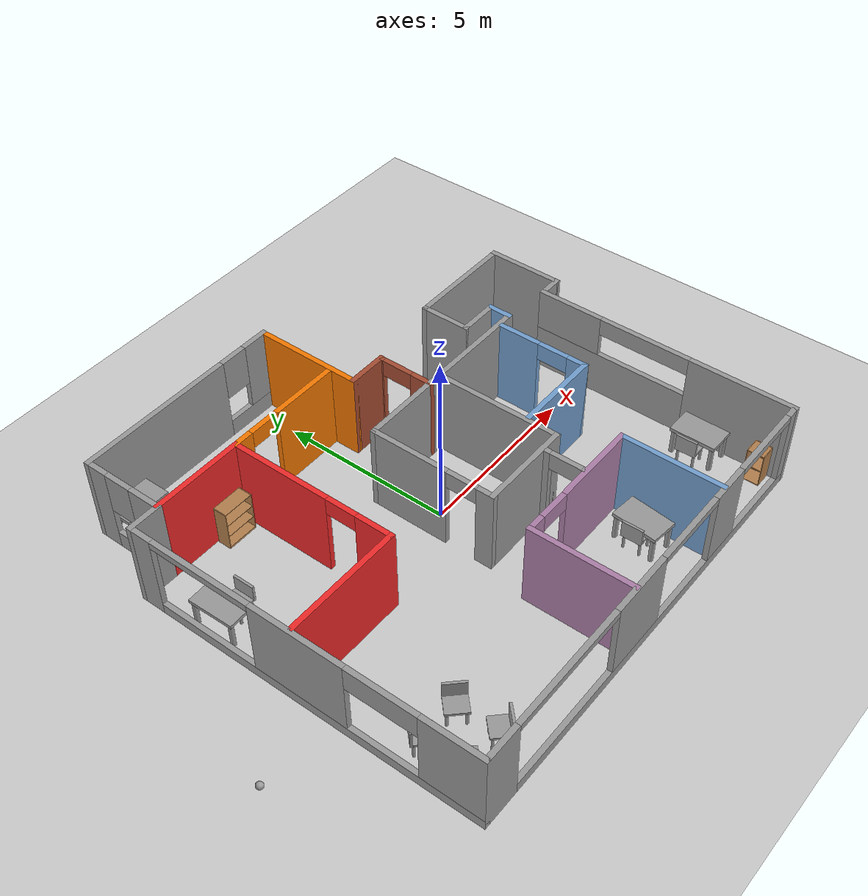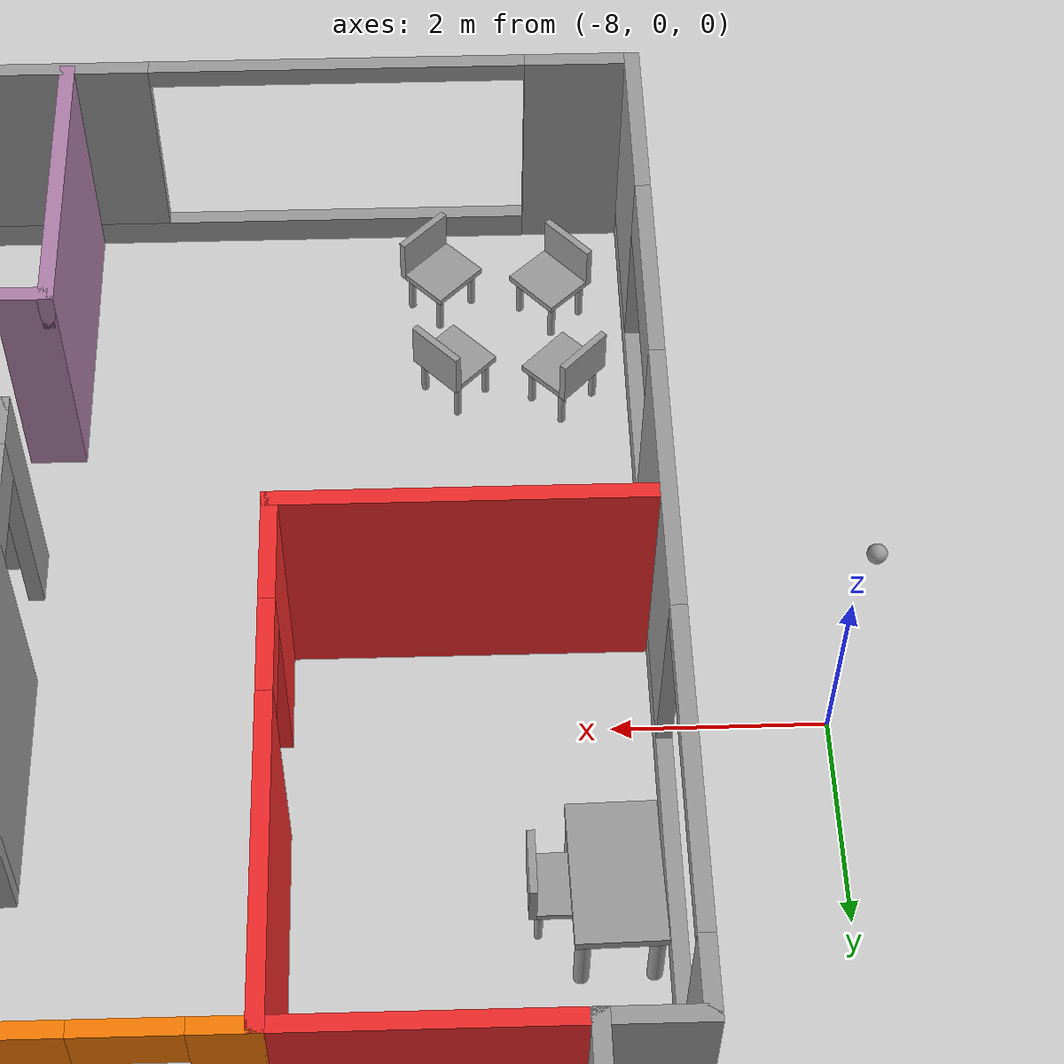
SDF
<sdf version="1.7">
 <world name="default">
  <plugin name="hello_plugin" filename="libhello_plugin.so"/>
  <light name="sun" type="directional">
   <pose>0 0 10 0 -0 0</pose>
   <diffuse>0.8 0.8 0.8 1</diffuse>
   <specular>0.2 0.2 0.2 1</specular>
   <attenuation>
    <range>1000</range>
    <constant>0.9</constant>
    <linear>0.01</linear>
    <quadratic>0.001</quadratic>
   </attenuation>
   <direction>-0.5 0.1 -0.9</direction>
   <spot><inner_angle>0</inner_angle><outer_angle>0</outer_angle><falloff>0</falloff></spot>
  </light>
  <model name="ground_plane">
   <static>1</static>
   <link name="link">
    <collision name="collision">
     <geometry><plane><normal>0 0 1</normal><size>100 100</size></plane></geometry>
     <surface>
      <contact><collide_bitmask>65535</collide_bitmask></contact>
      <friction><ode><mu>100</mu><mu2>50</mu2></ode></friction>
     </surface>
    </collision>
    <visual name="visual">
     <cast_shadows>0</cast_shadows>
     <geometry><plane><normal>0 0 1</normal><size>100 100</size></plane></geometry>
     <material>
      <script><uri>file://media/materials/scripts/gazebo.material</uri><name>Gazebo/Grey</name></script>
     </material>
    </visual>
   </link>
  </model>
  <gravity>0 0 -9.8</gravity>
  <magnetic_field>6e-06 2.3e-05 -4.2e-05</magnetic_field>
  <atmosphere type="adiabatic"/>
  <physics type="ode">
   <max_step_size>0.001</max_step_size>
   <real_time_factor>1</real_time_factor>
   <real_time_update_rate>1000</real_time_update_rate>
  </physics>
  <scene><ambient>0.4 0.4 0.4 1</ambient><background>0.7 0.7 0.7 1</background><shadows>1</shadows></scene>
  <spherical_coordinates>
   <surface_model>EARTH_WGS84</surface_model>
   <latitude_deg>0</latitude_deg>
   <longitude_deg>0</longitude_deg>
   <elevation>0</elevation>
   <heading_deg>0</heading_deg>
  </spherical_coordinates>
  <model name="Naegok_House">
   <pose>0.27217 0.0598 0 0 -0 0</pose>
   <link name="Wall_32">
    <pose>-5.875 5.05 0 0 -0 -1.5708</pose>
    <visual name="Wall_32_Visual_0">
     <pose>-0.895035 0 1.25 0 -0 0</pose>
     <geometry><box><size>0.709929 0.15 2.5</size></box></geometry>
     <material>
      <script><uri>file://media/materials/scripts/gazebo.material</uri><name>Gazebo/Grey</name></script>
      <ambient>1 1 1 1</ambient>
     </material>
     <meta><layer>0</layer></meta>
    </visual>
    <collision name="Wall_32_Collision_0">
     <geometry><box><size>0.709929 0.15 2.5</size></box></geometry>
     <pose>-0.895035 0 1.25 0 -0 0</pose>
    </collision>
    <visual name="Wall_32_Visual_1">
     <pose>0.354965 0 0.25 0 -0 0</pose>
     <geometry><box><size>1.79007 0.15 0.5</size></box></geometry>
     <material>
      <script><uri>file://media/materials/scripts/gazebo.material</uri><name>Gazebo/Grey</name></script>
      <ambient>1 1 1 1</ambient>
     </material>
     <meta><layer>0</layer></meta>
    </visual>
    <collision name="Wall_32_Collision_1">
     <geometry><box><size>1.79007 0.15 0.5</size></box></geometry>
     <pose>0.354965 0 0.25 0 -0 0</pose>
    </collision>
    <visual name="Wall_32_Visual_2">
     <pose>0.754965 0 1.5 0 -0 0</pose>
     <geometry><box><size>0.990071 0.15 2</size></box></geometry>
     <material>
      <script><uri>file://media/materials/scripts/gazebo.material</uri><name>Gazebo/Grey</name></script>
      <ambient>1 1 1 1</ambient>
     </material>
     <meta><layer>0</layer></meta>
    </visual>
    <collision name="Wall_32_Collision_2">
     <geometry><box><size>0.990071 0.15 2</size></box></geometry>
     <pose>0.754965 0 1.5 0 -0 0</pose>
    </collision>
    <visual name="Wall_32_Visual_3">
     <pose>-0.140071 0 1.9 0 -0 0</pose>
     <geometry><box><size>0.8 0.15 1.2</size></box></geometry>
     <material>
      <script><uri>file://media/materials/scripts/gazebo.material</uri><name>Gazebo/Grey</name></script>
      <ambient>1 1 1 1</ambient>
     </material>
     <meta><layer>0</layer></meta>
    </visual>
    <collision name="Wall_32_Collision_3">
     <geometry><box><size>0.8 0.15 1.2</size></box></geometry>
     <pose>-0.140071 0 1.9 0 -0 0</pose>
    </collision>
   </link>
   <link name="Wall_33">
    <collision name="Wall_33_Collision">
     <geometry><box><size>1 0.15 2.5</size></box></geometry>
     <pose>0 0 1.25 0 -0 0</pose>
    </collision>
    <visual name="Wall_33_Visual">
     <pose>0 0 1.25 0 -0 0</pose>
     <geometry><box><size>1 0.15 2.5</size></box></geometry>
     <material>
      <script><uri>file://media/materials/scripts/gazebo.material</uri><name>Gazebo/Grey</name></script>
      <ambient>1 1 1 1</ambient>
     </material>
     <meta><layer>0</layer></meta>
    </visual>
    <pose>-6.3 3.875 0 0 -0 3.14159</pose>
   </link>
   <link name="Wall_34">
    <pose>-6.725 -1.175 0 0 -0 -1.5708</pose>
    <visual name="Wall_34_Visual_0">
     <pose>-4.75688 0 1.25 0 -0 0</pose>
     <geometry><box><size>0.736232 0.15 2.5</size></box></geometry>
     <material>
      <script><uri>file://media/materials/scripts/gazebo.material</uri><name>Gazebo/Grey</name></script>
      <ambient>1 1 1 1</ambient>
     </material>
     <meta><layer>0</layer></meta>
    </visual>
    <collision name="Wall_34_Collision_0">
     <geometry><box><size>0.736232 0.15 2.5</size></box></geometry>
     <pose>-4.75688 0 1.25 0 -0 0</pose>
    </collision>
    <visual name="Wall_34_Visual_1">
     <pose>0.368116 0 0.15 0 -0 0</pose>
     <geometry><box><size>9.51377 0.15 0.3</size></box></geometry>
     <material>
      <script><uri>file://media/materials/scripts/gazebo.material</uri><name>Gazebo/Grey</name></script>
      <ambient>1 1 1 1</ambient>
     </material>
     <meta><layer>0</layer></meta>
    </visual>
    <collision name="Wall_34_Collision_1">
     <geometry><box><size>9.51377 0.15 0.3</size></box></geometry>
     <pose>0.368116 0 0.15 0 -0 0</pose>
    </collision>
    <visual name="Wall_34_Visual_2">
     <pose>-0.018295 0 1.4 0 -0 0</pose>
     <geometry><box><size>2.74094 0.15 2.2</size></box></geometry>
     <material>
      <script><uri>file://media/materials/scripts/gazebo.material</uri><name>Gazebo/Grey</name></script>
      <ambient>1 1 1 1</ambient>
     </material>
     <meta><layer>0</layer></meta>
    </visual>
    <collision name="Wall_34_Collision_2">
     <geometry><box><size>2.74094 0.15 2.2</size></box></geometry>
     <pose>-0.018295 0 1.4 0 -0 0</pose>
    </collision>
    <visual name="Wall_34_Visual_3">
     <pose>4.23859 0 1.4 0 -0 0</pose>
     <geometry><box><size>1.77282 0.15 2.2</size></box></geometry>
     <material>
      <script><uri>file://media/materials/scripts/gazebo.material</uri><name>Gazebo/Grey</name></script>
      <ambient>1 1 1 1</ambient>
     </material>
     <meta><layer>0</layer></meta>
    </visual>
    <collision name="Wall_34_Collision_3">
     <geometry><box><size>1.77282 0.15 2.2</size></box></geometry>
     <pose>4.23859 0 1.4 0 -0 0</pose>
    </collision>
    <visual name="Wall_34_Visual_4">
     <pose>2.35218 0 2.15 0 -0 0</pose>
     <geometry><box><size>2 0.15 0.7</size></box></geometry>
     <material>
      <script><uri>file://media/materials/scripts/gazebo.material</uri><name>Gazebo/Grey</name></script>
      <ambient>1 1 1 1</ambient>
     </material>
     <meta><layer>0</layer></meta>
    </visual>
    <collision name="Wall_34_Collision_4">
     <geometry><box><size>2 0.15 0.7</size></box></geometry>
     <pose>2.35218 0 2.15 0 -0 0</pose>
    </collision>
    <visual name="Wall_34_Visual_5">
     <pose>-2.88877 0 2.4 0 -0 0</pose>
     <geometry><box><size>3 0.15 0.2</size></box></geometry>
     <material>
      <script><uri>file://media/materials/scripts/gazebo.material</uri><name>Gazebo/Grey</name></script>
      <ambient>1 1 1 1</ambient>
     </material>
     <meta><layer>0</layer></meta>
    </visual>
    <collision name="Wall_34_Collision_5">
     <geometry><box><size>3 0.15 0.2</size></box></geometry>
     <pose>-2.88877 0 2.4 0 -0 0</pose>
    </collision>
   </link>
   <link name="Wall_35">
    <pose>-0.3 -6.225 0 0 -0 0</pose>
    <visual name="Wall_35_Visual_0">
     <pose>-5.93367 0 1.25 0 -0 0</pose>
     <geometry><box><size>1.13267 0.15 2.5</size></box></geometry>
     <material>
      <script><uri>file://media/materials/scripts/gazebo.material</uri><name>Gazebo/Grey</name></script>
      <ambient>1 1 1 1</ambient>
     </material>
     <meta><layer>0</layer></meta>
    </visual>
    <collision name="Wall_35_Collision_0">
     <geometry><box><size>1.13267 0.15 2.5</size></box></geometry>
     <pose>-5.93367 0 1.25 0 -0 0</pose>
    </collision>
    <visual name="Wall_35_Visual_1">
     <pose>0.566334 0 0.15 0 -0 0</pose>
     <geometry><box><size>11.8673 0.15 0.3</size></box></geometry>
     <material>
      <script><uri>file://media/materials/scripts/gazebo.material</uri><name>Gazebo/Grey</name></script>
      <ambient>1 1 1 1</ambient>
     </material>
     <meta><layer>0</layer></meta>
    </visual>
    <collision name="Wall_35_Collision_1">
     <geometry><box><size>11.8673 0.15 0.3</size></box></geometry>
     <pose>0.566334 0 0.15 0 -0 0</pose>
    </collision>
    <visual name="Wall_35_Visual_2">
     <pose>-0.705786 0 1.4 0 -0 0</pose>
     <geometry><box><size>1.92309 0.15 2.2</size></box></geometry>
     <material>
      <script><uri>file://media/materials/scripts/gazebo.material</uri><name>Gazebo/Grey</name></script>
      <ambient>1 1 1 1</ambient>
     </material>
     <meta><layer>0</layer></meta>
    </visual>
    <collision name="Wall_35_Collision_2">
     <geometry><box><size>1.92309 0.15 2.2</size></box></geometry>
     <pose>-0.705786 0 1.4 0 -0 0</pose>
    </collision>
    <visual name="Wall_35_Visual_3">
     <pose>3.1598 0 1.4 0 -0 0</pose>
     <geometry><box><size>1.20807 0.15 2.2</size></box></geometry>
     <material>
      <script><uri>file://media/materials/scripts/gazebo.material</uri><name>Gazebo/Grey</name></script>
      <ambient>1 1 1 1</ambient>
     </material>
     <meta><layer>0</layer></meta>
    </visual>
    <collision name="Wall_35_Collision_3">
     <geometry><box><size>1.20807 0.15 2.2</size></box></geometry>
     <pose>3.1598 0 1.4 0 -0 0</pose>
    </collision>
    <visual name="Wall_35_Visual_4">
     <pose>6.28192 0 1.4 0 -0 0</pose>
     <geometry><box><size>0.436168 0.15 2.2</size></box></geometry>
     <material>
      <script><uri>file://media/materials/scripts/gazebo.material</uri><name>Gazebo/Grey</name></script>
      <ambient>1 1 1 1</ambient>
     </material>
     <meta><layer>0</layer></meta>
    </visual>
    <collision name="Wall_35_Collision_4">
     <geometry><box><size>0.436168 0.15 2.2</size></box></geometry>
     <pose>6.28192 0 1.4 0 -0 0</pose>
    </collision>
    <visual name="Wall_35_Visual_5">
     <pose>-3.51733 0 2.4 0 -0 0</pose>
     <geometry><box><size>3.7 0.15 0.2</size></box></geometry>
     <material>
      <script><uri>file://media/materials/scripts/gazebo.material</uri><name>Gazebo/Grey</name></script>
      <ambient>1 1 1 1</ambient>
     </material>
     <meta><layer>0</layer></meta>
    </visual>
    <collision name="Wall_35_Collision_5">
     <geometry><box><size>3.7 0.15 0.2</size></box></geometry>
     <pose>-3.51733 0 2.4 0 -0 0</pose>
    </collision>
    <visual name="Wall_35_Visual_6">
     <pose>1.40576 0 2.4 0 -0 0</pose>
     <geometry><box><size>2.3 0.15 0.2</size></box></geometry>
     <material>
      <script><uri>file://media/materials/scripts/gazebo.material</uri><name>Gazebo/Grey</name></script>
      <ambient>1 1 1 1</ambient>
     </material>
     <meta><layer>0</layer></meta>
    </visual>
    <collision name="Wall_35_Collision_6">
     <geometry><box><size>2.3 0.15 0.2</size></box></geometry>
     <pose>1.40576 0 2.4 0 -0 0</pose>
    </collision>
    <visual name="Wall_35_Visual_7">
     <pose>4.91383 0 2.4 0 -0 0</pose>
     <geometry><box><size>2.3 0.15 0.2</size></box></geometry>
     <material>
      <script><uri>file://media/materials/scripts/gazebo.material</uri><name>Gazebo/Grey</name></script>
      <ambient>1 1 1 1</ambient>
     </material>
     <meta><layer>0</layer></meta>
    </visual>
    <collision name="Wall_35_Collision_7">
     <geometry><box><size>2.3 0.15 0.2</size></box></geometry>
     <pose>4.91383 0 2.4 0 -0 0</pose>
    </collision>
   </link>
   <link name="Wall_36">
    <pose>6.125 -2.425 0 0 -0 1.5708</pose>
    <visual name="Wall_36_Visual_0">
     <pose>-2.32991 0 1.25 0 -0 0</pose>
     <geometry><box><size>3.09019 0.15 2.5</size></box></geometry>
     <material>
      <script><uri>file://media/materials/scripts/gazebo.material</uri><name>Gazebo/Grey</name></script>
      <ambient>1 1 1 1</ambient>
     </material>
     <meta><layer>0</layer></meta>
    </visual>
    <collision name="Wall_36_Collision_0">
     <geometry><box><size>3.09019 0.15 2.5</size></box></geometry>
     <pose>-2.32991 0 1.25 0 -0 0</pose>
    </collision>
    <visual name="Wall_36_Visual_1">
     <pose>1.54509 0 0.65 0 -0 0</pose>
     <geometry><box><size>4.65981 0.15 1.3</size></box></geometry>
     <material>
      <script><uri>file://media/materials/scripts/gazebo.material</uri><name>Gazebo/Grey</name></script>
      <ambient>1 1 1 1</ambient>
     </material>
     <meta><layer>0</layer></meta>
    </visual>
    <collision name="Wall_36_Collision_1">
     <geometry><box><size>4.65981 0.15 1.3</size></box></geometry>
     <pose>1.54509 0 0.65 0 -0 0</pose>
    </collision>
    <visual name="Wall_36_Visual_2">
     <pose>2.89509 0 1.9 0 -0 0</pose>
     <geometry><box><size>1.95981 0.15 1.2</size></box></geometry>
     <material>
      <script><uri>file://media/materials/scripts/gazebo.material</uri><name>Gazebo/Grey</name></script>
      <ambient>1 1 1 1</ambient>
     </material>
     <meta><layer>0</layer></meta>
    </visual>
    <collision name="Wall_36_Collision_2">
     <geometry><box><size>1.95981 0.15 1.2</size></box></geometry>
     <pose>2.89509 0 1.9 0 -0 0</pose>
    </collision>
    <visual name="Wall_36_Visual_3">
     <pose>0.565187 0 2.25 0 -0 0</pose>
     <geometry><box><size>2.7 0.15 0.5</size></box></geometry>
     <material>
      <script><uri>file://media/materials/scripts/gazebo.material</uri><name>Gazebo/Grey</name></script>
      <ambient>1 1 1 1</ambient>
     </material>
     <meta><layer>0</layer></meta>
    </visual>
    <collision name="Wall_36_Collision_3">
     <geometry><box><size>2.7 0.15 0.5</size></box></geometry>
     <pose>0.565187 0 2.25 0 -0 0</pose>
    </collision>
   </link>
   <link name="Wall_37">
    <collision name="Wall_37_Collision">
     <geometry><box><size>0.75 0.15 2.5</size></box></geometry>
     <pose>0 0 1.25 0 -0 0</pose>
    </collision>
    <visual name="Wall_37_Visual">
     <pose>0 0 1.25 0 -0 0</pose>
     <geometry><box><size>0.75 0.15 2.5</size></box></geometry>
     <material>
      <script><uri>file://media/materials/scripts/gazebo.material</uri><name>Gazebo/Grey</name></script>
      <ambient>1 1 1 1</ambient>
     </material>
     <meta><layer>0</layer></meta>
    </visual>
    <pose>6.425 1.375 0 0 -0 0</pose>
   </link>
   <link name="Wall_38">
    <collision name="Wall_38_Collision">
     <geometry><box><size>2.25 0.15 2.5</size></box></geometry>
     <pose>0 0 1.25 0 -0 0</pose>
    </collision>
    <visual name="Wall_38_Visual">
     <pose>0 0 1.25 0 -0 0</pose>
     <geometry><box><size>2.25 0.15 2.5</size></box></geometry>
     <material>
      <script><uri>file://media/materials/scripts/gazebo.material</uri><name>Gazebo/Grey</name></script>
      <ambient>1 1 1 1</ambient>
     </material>
     <meta><layer>0</layer></meta>
    </visual>
    <pose>6.725 2.425 0 0 -0 1.5708</pose>
   </link>
   <link name="Wall_39">
    <collision name="Wall_39_Collision">
     <geometry><box><size>3.25 0.15 2.5</size></box></geometry>
     <pose>0 0 1.25 0 -0 0</pose>
    </collision>
    <visual name="Wall_39_Visual">
     <pose>0 0 1.25 0 -0 0</pose>
     <geometry><box><size>3.25 0.15 2.5</size></box></geometry>
     <material>
      <script><uri>file://media/materials/scripts/gazebo.material</uri><name>Gazebo/Grey</name></script>
      <ambient>1 1 1 1</ambient>
     </material>
     <meta><layer>0</layer></meta>
    </visual>
    <pose>5.175 3.475 0 0 -0 3.14159</pose>
   </link>
   <link name="Wall_40">
    <collision name="Wall_40_Collision">
     <geometry><box><size>1.5 0.15 2.5</size></box></geometry>
     <pose>0 0 1.25 0 -0 0</pose>
    </collision>
    <visual name="Wall_40_Visual">
     <pose>0 0 1.25 0 -0 0</pose>
     <geometry><box><size>1.5 0.15 2.5</size></box></geometry>
     <material>
      <script><uri>file://media/materials/scripts/gazebo.material</uri><name>Gazebo/Grey</name></script>
      <ambient>1 1 1 1</ambient>
     </material>
     <meta><layer>0</layer></meta>
    </visual>
    <pose>3.625 2.8 0 0 -0 -1.5708</pose>
   </link>
   <link name="Wall_41">
    <collision name="Wall_41_Collision">
     <geometry><box><size>1.25 0.15 2.5</size></box></geometry>
     <pose>0 0 1.25 0 -0 0</pose>
    </collision>
    <visual name="Wall_41_Visual">
     <pose>0 0 1.25 0 -0 0</pose>
     <geometry><box><size>1.25 0.15 2.5</size></box></geometry>
     <material>
      <script><uri>file://media/materials/scripts/gazebo.material</uri><name>Gazebo/Grey</name></script>
      <ambient>1 1 1 1</ambient>
     </material>
     <meta><layer>0</layer></meta>
    </visual>
    <pose>4.175 2.125 0 0 -0 0</pose>
   </link>
   <link name="Wall_42">
    <collision name="Wall_42_Collision">
     <geometry><box><size>0.75 0.15 2.5</size></box></geometry>
     <pose>0 0 1.25 0 -0 0</pose>
    </collision>
    <visual name="Wall_42_Visual">
     <pose>0 0 1.25 0 -0 0</pose>
     <geometry><box><size>0.75 0.15 2.5</size></box></geometry>
     <material>
      <script><uri>file://media/materials/scripts/gazebo.material</uri><name>Gazebo/Grey</name></script>
      <ambient>0.447059 0.623529 0.811765 1</ambient>
     </material>
     <meta><layer>0</layer></meta>
    </visual>
    <pose>4.725 1.825 0 0 -0 -1.5708</pose>
   </link>
   <link name="Wall_43">
    <collision name="Wall_43_Collision">
     <geometry><box><size>5.75 0.15 2.5</size></box></geometry>
     <pose>0 0 1.25 0 -0 0</pose>
    </collision>
    <visual name="Wall_43_Visual">
     <pose>0 0 1.25 0 -0 0</pose>
     <geometry><box><size>5.75 0.15 2.5</size></box></geometry>
     <material>
      <script><uri>file://media/materials/scripts/gazebo.material</uri><name>Gazebo/Grey</name></script>
      <ambient>1 1 1 1</ambient>
     </material>
     <meta><layer>0</layer></meta>
    </visual>
    <pose>1.925 1.525 0 0 -0 3.14159</pose>
   </link>
   <link name="Wall_44">
    <pose>-0.875 -0.275 0 0 -0 -1.5708</pose>
    <visual name="Wall_44_Visual_0">
     <pose>-0.710452 0 1.25 0 -0 0</pose>
     <geometry><box><size>2.3291 0.15 2.5</size></box></geometry>
     <material>
      <script><uri>file://media/materials/scripts/gazebo.material</uri><name>Gazebo/Grey</name></script>
      <ambient>1 1 1 1</ambient>
     </material>
     <meta><layer>0</layer></meta>
    </visual>
    <collision name="Wall_44_Collision_0">
     <geometry><box><size>2.3291 0.15 2.5</size></box></geometry>
     <pose>-0.710452 0 1.25 0 -0 0</pose>
    </collision>
    <visual name="Wall_44_Visual_1">
     <pose>1.61455 0 1.25 0 -0 0</pose>
     <geometry><box><size>0.520903 0.15 2.5</size></box></geometry>
     <material>
      <script><uri>file://media/materials/scripts/gazebo.material</uri><name>Gazebo/Grey</name></script>
      <ambient>1 1 1 1</ambient>
     </material>
     <meta><layer>0</layer></meta>
    </visual>
    <collision name="Wall_44_Collision_1">
     <geometry><box><size>0.520903 0.15 2.5</size></box></geometry>
     <pose>1.61455 0 1.25 0 -0 0</pose>
    </collision>
    <visual name="Wall_44_Visual_2">
     <pose>0.904097 0 2.25 0 -0 0</pose>
     <geometry><box><size>0.9 0.15 0.5</size></box></geometry>
     <material>
      <script><uri>file://media/materials/scripts/gazebo.material</uri><name>Gazebo/Grey</name></script>
      <ambient>1 1 1 1</ambient>
     </material>
     <meta><layer>0</layer></meta>
    </visual>
    <collision name="Wall_44_Collision_2">
     <geometry><box><size>0.9 0.15 0.5</size></box></geometry>
     <pose>0.904097 0 2.25 0 -0 0</pose>
    </collision>
   </link>
   <link name="Wall_45">
    <collision name="Wall_45_Collision">
     <geometry><box><size>2.75 0.15 2.5</size></box></geometry>
     <pose>0 0 1.25 0 -0 0</pose>
    </collision>
    <visual name="Wall_45_Visual">
     <pose>0 0 1.25 0 -0 0</pose>
     <geometry><box><size>2.75 0.15 2.5</size></box></geometry>
     <material>
      <script><uri>file://media/materials/scripts/gazebo.material</uri><name>Gazebo/Grey</name></script>
      <ambient>1 1 1 1</ambient>
     </material>
     <meta><layer>0</layer></meta>
    </visual>
    <pose>0.425 -2.075 0 0 -0 0</pose>
   </link>
   <link name="Wall_46">
    <collision name="Wall_46_Collision">
     <geometry><box><size>3.75 0.15 2.5</size></box></geometry>
     <pose>0 0 1.25 0 -0 0</pose>
    </collision>
    <visual name="Wall_46_Visual">
     <pose>0 0 1.25 0 -0 0</pose>
     <geometry><box><size>3.75 0.15 2.5</size></box></geometry>
     <material>
      <script><uri>file://media/materials/scripts/gazebo.material</uri><name>Gazebo/Grey</name></script>
      <ambient>1 1 1 1</ambient>
     </material>
     <meta><layer>0</layer></meta>
    </visual>
    <pose>1.725 -0.275 0 0 -0 1.5708</pose>
   </link>
   <link name="Wall_49">
    <pose>4.28757 0.115926 0 0 -0 -1.5708</pose>
    <visual name="Wall_49_Visual_0">
     <pose>-0.743249 0 1.25 0 -0 0</pose>
     <geometry><box><size>1.2635 0.15 2.5</size></box></geometry>
     <material>
      <script><uri>file://media/materials/scripts/gazebo.material</uri><name>Gazebo/Grey</name></script>
      <ambient>0.447059 0.623529 0.811765 1</ambient>
     </material>
     <meta><layer>0</layer></meta>
    </visual>
    <collision name="Wall_49_Collision_0">
     <geometry><box><size>1.2635 0.15 2.5</size></box></geometry>
     <pose>-0.743249 0 1.25 0 -0 0</pose>
    </collision>
    <visual name="Wall_49_Visual_1">
     <pose>1.08175 0 1.25 0 -0 0</pose>
     <geometry><box><size>0.586499 0.15 2.5</size></box></geometry>
     <material>
      <script><uri>file://media/materials/scripts/gazebo.material</uri><name>Gazebo/Grey</name></script>
      <ambient>0.447059 0.623529 0.811765 1</ambient>
     </material>
     <meta><layer>0</layer></meta>
    </visual>
    <collision name="Wall_49_Collision_1">
     <geometry><box><size>0.586499 0.15 2.5</size></box></geometry>
     <pose>1.08175 0 1.25 0 -0 0</pose>
    </collision>
    <visual name="Wall_49_Visual_2">
     <pose>0.338501 0 2.25 0 -0 0</pose>
     <geometry><box><size>0.9 0.15 0.5</size></box></geometry>
     <material>
      <script><uri>file://media/materials/scripts/gazebo.material</uri><name>Gazebo/Grey</name></script>
      <ambient>0.447059 0.623529 0.811765 1</ambient>
     </material>
     <meta><layer>0</layer></meta>
    </visual>
    <collision name="Wall_49_Collision_2">
     <geometry><box><size>0.9 0.15 0.5</size></box></geometry>
     <pose>0.338501 0 2.25 0 -0 0</pose>
    </collision>
   </link>
   <link name="Wall_50">
    <collision name="Wall_50_Collision">
     <geometry><box><size>2.6 0.15 2.5</size></box></geometry>
     <pose>0 0 1.25 0 -0 0</pose>
    </collision>
    <visual name="Wall_50_Visual">
     <pose>0 0 1.25 0 -0 0</pose>
     <geometry><box><size>2.6 0.15 2.5</size></box></geometry>
     <material>
      <script><uri>file://media/materials/scripts/gazebo.material</uri><name>Gazebo/Grey</name></script>
      <ambient>0.447059 0.623529 0.811765 1</ambient>
     </material>
     <meta><layer>0</layer></meta>
    </visual>
    <pose>3.06257 -1.18407 0 0 -0 3.14159</pose>
   </link>
   <link name="Wall_52">
    <pose>-2.825 6.225 0 0 -0 0</pose>
    <visual name="Wall_52_Visual_0">
     <pose>-0.822876 0 1.25 0 -0 0</pose>
     <geometry><box><size>4.60425 0.15 2.5</size></box></geometry>
     <material>
      <script><uri>file://media/materials/scripts/gazebo.material</uri><name>Gazebo/Grey</name></script>
      <ambient>1 1 1 1</ambient>
     </material>
     <meta><layer>0</layer></meta>
    </visual>
    <collision name="Wall_52_Collision_0">
     <geometry><box><size>4.60425 0.15 2.5</size></box></geometry>
     <pose>-0.822876 0 1.25 0 -0 0</pose>
    </collision>
    <visual name="Wall_52_Visual_1">
     <pose>2.30212 0 0.25 0 -0 0</pose>
     <geometry><box><size>1.64575 0.15 0.5</size></box></geometry>
     <material>
      <script><uri>file://media/materials/scripts/gazebo.material</uri><name>Gazebo/Grey</name></script>
      <ambient>1 1 1 1</ambient>
     </material>
     <meta><layer>0</layer></meta>
    </visual>
    <collision name="Wall_52_Collision_1">
     <geometry><box><size>1.64575 0.15 0.5</size></box></geometry>
     <pose>2.30212 0 0.25 0 -0 0</pose>
    </collision>
    <visual name="Wall_52_Visual_2">
     <pose>2.70212 0 1.5 0 -0 0</pose>
     <geometry><box><size>0.845753 0.15 2</size></box></geometry>
     <material>
      <script><uri>file://media/materials/scripts/gazebo.material</uri><name>Gazebo/Grey</name></script>
      <ambient>1 1 1 1</ambient>
     </material>
     <meta><layer>0</layer></meta>
    </visual>
    <collision name="Wall_52_Collision_2">
     <geometry><box><size>0.845753 0.15 2</size></box></geometry>
     <pose>2.70212 0 1.5 0 -0 0</pose>
    </collision>
    <visual name="Wall_52_Visual_3">
     <pose>1.87925 0 1.9 0 -0 0</pose>
     <geometry><box><size>0.8 0.15 1.2</size></box></geometry>
     <material>
      <script><uri>file://media/materials/scripts/gazebo.material</uri><name>Gazebo/Grey</name></script>
      <ambient>1 1 1 1</ambient>
     </material>
     <meta><layer>0</layer></meta>
    </visual>
    <collision name="Wall_52_Collision_3">
     <geometry><box><size>0.8 0.15 1.2</size></box></geometry>
     <pose>1.87925 0 1.9 0 -0 0</pose>
    </collision>
   </link>
   <link name="Wall_53">
    <collision name="Wall_53_Collision">
     <geometry><box><size>3.25 0.15 2.5</size></box></geometry>
     <pose>0 0 1.25 0 -0 0</pose>
    </collision>
    <visual name="Wall_53_Visual">
     <pose>0 0 1.25 0 -0 0</pose>
     <geometry><box><size>3.25 0.15 2.5</size></box></geometry>
     <material>
      <script><uri>file://media/materials/scripts/gazebo.material</uri><name>Gazebo/Grey</name></script>
      <ambient>0.960784 0.47451 0 1</ambient>
     </material>
     <meta><layer>0</layer></meta>
    </visual>
    <pose>0.225 4.675 0 0 -0 -1.5708</pose>
   </link>
   <link name="Wall_54">
    <collision name="Wall_54_Collision">
     <geometry><box><size>1.25 0.15 2.5</size></box></geometry>
     <pose>0 0 1.25 0 -0 0</pose>
    </collision>
    <visual name="Wall_54_Visual">
     <pose>0 0 1.25 0 -0 0</pose>
     <geometry><box><size>1.25 0.15 2.5</size></box></geometry>
     <material>
      <script><uri>file://media/materials/scripts/gazebo.material</uri><name>Gazebo/Bricks</name></script>
      <ambient>1 1 1 1</ambient>
     </material>
     <meta><layer>0</layer></meta>
    </visual>
    <pose>0.775 3.125 0 0 -0 0</pose>
   </link>
   <link name="Wall_55">
    <pose>1.325 2.325 0 0 -0 -1.5708</pose>
    <visual name="Wall_55_Visual_0">
     <pose>-0.780017 0 1.25 0 -0 0</pose>
     <geometry><box><size>0.189966 0.15 2.5</size></box></geometry>
     <material>
      <script><uri>file://media/materials/scripts/gazebo.material</uri><name>Gazebo/Bricks</name></script>
      <ambient>1 1 1 1</ambient>
     </material>
     <meta><layer>0</layer></meta>
    </visual>
    <collision name="Wall_55_Collision_0">
     <geometry><box><size>0.189966 0.15 2.5</size></box></geometry>
     <pose>-0.780017 0 1.25 0 -0 0</pose>
    </collision>
    <visual name="Wall_55_Visual_1">
     <pose>0.544983 0 1.25 0 -0 0</pose>
     <geometry><box><size>0.660034 0.15 2.5</size></box></geometry>
     <material>
      <script><uri>file://media/materials/scripts/gazebo.material</uri><name>Gazebo/Bricks</name></script>
      <ambient>1 1 1 1</ambient>
     </material>
     <meta><layer>0</layer></meta>
    </visual>
    <collision name="Wall_55_Collision_1">
     <geometry><box><size>0.660034 0.15 2.5</size></box></geometry>
     <pose>0.544983 0 1.25 0 -0 0</pose>
    </collision>
    <visual name="Wall_55_Visual_2">
     <pose>-0.235034 0 2.25 0 -0 0</pose>
     <geometry><box><size>0.9 0.15 0.5</size></box></geometry>
     <material>
      <script><uri>file://media/materials/scripts/gazebo.material</uri><name>Gazebo/Bricks</name></script>
      <ambient>1 1 1 1</ambient>
     </material>
     <meta><layer>0</layer></meta>
    </visual>
    <collision name="Wall_55_Collision_2">
     <geometry><box><size>0.9 0.15 0.5</size></box></geometry>
     <pose>-0.235034 0 2.25 0 -0 0</pose>
    </collision>
   </link>
   <link name="Wall_58">
    <collision name="Wall_58_Collision">
     <geometry><box><size>2.75 0.15 2.5</size></box></geometry>
     <pose>0 0 1.25 0 -0 0</pose>
    </collision>
    <visual name="Wall_58_Visual">
     <pose>0 0 1.25 0 -0 0</pose>
     <geometry><box><size>2.75 0.15 2.5</size></box></geometry>
     <material>
      <script><uri>file://media/materials/scripts/gazebo.material</uri><name>Gazebo/Grey</name></script>
      <ambient>0.937255 0.160784 0.160784 1</ambient>
     </material>
     <meta><layer>0</layer></meta>
    </visual>
    <pose>-4.575 3.875 0 0 -0 0</pose>
   </link>
   <link name="Wall_59">
    <pose>-3.275 1.45 0 0 -0 -1.5708</pose>
    <visual name="Wall_59_Visual_0">
     <pose>-1.00103 0 1.25 0 -0 0</pose>
     <geometry><box><size>2.99794 0.15 2.5</size></box></geometry>
     <material>
      <script><uri>file://media/materials/scripts/gazebo.material</uri><name>Gazebo/Grey</name></script>
      <ambient>0.937255 0.160784 0.160784 1</ambient>
     </material>
     <meta><layer>0</layer></meta>
    </visual>
    <collision name="Wall_59_Collision_0">
     <geometry><box><size>2.99794 0.15 2.5</size></box></geometry>
     <pose>-1.00103 0 1.25 0 -0 0</pose>
    </collision>
    <visual name="Wall_59_Visual_1">
     <pose>1.94897 0 1.25 0 -0 0</pose>
     <geometry><box><size>1.10206 0.15 2.5</size></box></geometry>
     <material>
      <script><uri>file://media/materials/scripts/gazebo.material</uri><name>Gazebo/Grey</name></script>
      <ambient>0.937255 0.160784 0.160784 1</ambient>
     </material>
     <meta><layer>0</layer></meta>
    </visual>
    <collision name="Wall_59_Collision_1">
     <geometry><box><size>1.10206 0.15 2.5</size></box></geometry>
     <pose>1.94897 0 1.25 0 -0 0</pose>
    </collision>
    <visual name="Wall_59_Visual_2">
     <pose>0.947937 0 2.25 0 -0 0</pose>
     <geometry><box><size>0.9 0.15 0.5</size></box></geometry>
     <material>
      <script><uri>file://media/materials/scripts/gazebo.material</uri><name>Gazebo/Grey</name></script>
      <ambient>0.937255 0.160784 0.160784 1</ambient>
     </material>
     <meta><layer>0</layer></meta>
    </visual>
    <collision name="Wall_59_Collision_2">
     <geometry><box><size>0.9 0.15 0.5</size></box></geometry>
     <pose>0.947937 0 2.25 0 -0 0</pose>
    </collision>
   </link>
   <link name="Wall_60">
    <collision name="Wall_60_Collision">
     <geometry><box><size>3.5 0.15 2.5</size></box></geometry>
     <pose>0 0 1.25 0 -0 0</pose>
    </collision>
    <visual name="Wall_60_Visual">
     <pose>0 0 1.25 0 -0 0</pose>
     <geometry><box><size>3.5 0.15 2.5</size></box></geometry>
     <material>
      <script><uri>file://media/materials/scripts/gazebo.material</uri><name>Gazebo/Grey</name></script>
      <ambient>0.937255 0.160784 0.160784 1</ambient>
     </material>
     <meta><layer>0</layer></meta>
    </visual>
    <pose>-4.95 -0.975 0 0 -0 3.14159</pose>
   </link>
   <link name="Wall_62">
    <pose>-1.6 3.875 0 0 -0 0</pose>
    <visual name="Wall_62_Visual_0">
     <pose>-1.45201 0 1.25 0 -0 0</pose>
     <geometry><box><size>0.595982 0.15 2.5</size></box></geometry>
     <material>
      <script><uri>file://media/materials/scripts/gazebo.material</uri><name>Gazebo/Grey</name></script>
      <ambient>0.960784 0.47451 0 1</ambient>
     </material>
     <meta><layer>0</layer></meta>
    </visual>
    <collision name="Wall_62_Collision_0">
     <geometry><box><size>0.595982 0.15 2.5</size></box></geometry>
     <pose>-1.45201 0 1.25 0 -0 0</pose>
    </collision>
    <visual name="Wall_62_Visual_1">
     <pose>0.747991 0 1.25 0 -0 0</pose>
     <geometry><box><size>2.00402 0.15 2.5</size></box></geometry>
     <material>
      <script><uri>file://media/materials/scripts/gazebo.material</uri><name>Gazebo/Grey</name></script>
      <ambient>0.960784 0.47451 0 1</ambient>
     </material>
     <meta><layer>0</layer></meta>
    </visual>
    <collision name="Wall_62_Collision_1">
     <geometry><box><size>2.00402 0.15 2.5</size></box></geometry>
     <pose>0.747991 0 1.25 0 -0 0</pose>
    </collision>
    <visual name="Wall_62_Visual_2">
     <pose>-0.704018 0 2.25 0 -0 0</pose>
     <geometry><box><size>0.9 0.15 0.5</size></box></geometry>
     <material>
      <script><uri>file://media/materials/scripts/gazebo.material</uri><name>Gazebo/Grey</name></script>
      <ambient>0.960784 0.47451 0 1</ambient>
     </material>
     <meta><layer>0</layer></meta>
    </visual>
    <collision name="Wall_62_Collision_2">
     <geometry><box><size>0.9 0.15 0.5</size></box></geometry>
     <pose>-0.704018 0 2.25 0 -0 0</pose>
    </collision>
   </link>
   <link name="Wall_64">
    <collision name="Wall_64_Collision">
     <geometry><box><size>3 0.15 2.5</size></box></geometry>
     <pose>0 0 1.25 0 -0 0</pose>
    </collision>
    <visual name="Wall_64_Visual">
     <pose>0 0 1.25 0 -0 0</pose>
     <geometry><box><size>3 0.15 2.5</size></box></geometry>
     <material>
      <script><uri>file://media/materials/scripts/gazebo.material</uri><name>Gazebo/Grey</name></script>
      <ambient>0.678431 0.498039 0.658824 1</ambient>
     </material>
     <meta><layer>0</layer></meta>
    </visual>
    <pose>-1.17358 -4.76859 0 0 -0 1.5708</pose>
   </link>
   <link name="Wall_65">
    <pose>0.751417 -3.34359 0 0 -0 0</pose>
    <visual name="Wall_65_Visual_0">
     <pose>-1.72373 0 1.25 0 -0 0</pose>
     <geometry><box><size>0.552536 0.15 2.5</size></box></geometry>
     <material>
      <script><uri>file://media/materials/scripts/gazebo.material</uri><name>Gazebo/Grey</name></script>
      <ambient>0.678431 0.498039 0.658824 1</ambient>
     </material>
     <meta><layer>0</layer></meta>
    </visual>
    <collision name="Wall_65_Collision_0">
     <geometry><box><size>0.552536 0.15 2.5</size></box></geometry>
     <pose>-1.72373 0 1.25 0 -0 0</pose>
    </collision>
    <visual name="Wall_65_Visual_1">
     <pose>0.726268 0 1.25 0 -0 0</pose>
     <geometry><box><size>2.54746 0.15 2.5</size></box></geometry>
     <material>
      <script><uri>file://media/materials/scripts/gazebo.material</uri><name>Gazebo/Grey</name></script>
      <ambient>0.678431 0.498039 0.658824 1</ambient>
     </material>
     <meta><layer>0</layer></meta>
    </visual>
    <collision name="Wall_65_Collision_1">
     <geometry><box><size>2.54746 0.15 2.5</size></box></geometry>
     <pose>0.726268 0 1.25 0 -0 0</pose>
    </collision>
    <visual name="Wall_65_Visual_2">
     <pose>-0.997464 0 2.25 0 -0 0</pose>
     <geometry><box><size>0.9 0.15 0.5</size></box></geometry>
     <material>
      <script><uri>file://media/materials/scripts/gazebo.material</uri><name>Gazebo/Grey</name></script>
      <ambient>0.678431 0.498039 0.658824 1</ambient>
     </material>
     <meta><layer>0</layer></meta>
    </visual>
    <collision name="Wall_65_Collision_2">
     <geometry><box><size>0.9 0.15 0.5</size></box></geometry>
     <pose>-0.997464 0 2.25 0 -0 0</pose>
    </collision>
   </link>
   <link name="Wall_66">
    <collision name="Wall_66_Collision">
     <geometry><box><size>3 0.15 2.5</size></box></geometry>
     <pose>0 0 1.25 0 -0 0</pose>
    </collision>
    <visual name="Wall_66_Visual">
     <pose>0 0 1.25 0 -0 0</pose>
     <geometry><box><size>3 0.15 2.5</size></box></geometry>
     <material>
      <script><uri>file://media/materials/scripts/gazebo.material</uri><name>Gazebo/Grey</name></script>
      <ambient>0.447059 0.623529 0.811765 1</ambient>
     </material>
     <meta><layer>0</layer></meta>
    </visual>
    <pose>2.67642 -4.76859 0 0 -0 -1.5708</pose>
   </link>
   <link name="Wall_68">
    <pose>1.14526 -2.68252 0 0 -0 -1.5708</pose>
    <visual name="Wall_68_Visual_0">
     <pose>-0.52356 0 1.25 0 -0 0</pose>
     <geometry><box><size>0.322881 0.15 2.5</size></box></geometry>
     <material>
      <script><uri>file://media/materials/scripts/gazebo.material</uri><name>Gazebo/Grey</name></script>
      <ambient>1 1 1 1</ambient>
     </material>
     <meta><layer>0</layer></meta>
    </visual>
    <collision name="Wall_68_Collision_0">
     <geometry><box><size>0.322881 0.15 2.5</size></box></geometry>
     <pose>-0.52356 0 1.25 0 -0 0</pose>
    </collision>
    <visual name="Wall_68_Visual_1">
     <pose>0.61144 0 1.25 0 -0 0</pose>
     <geometry><box><size>0.147119 0.15 2.5</size></box></geometry>
     <material>
      <script><uri>file://media/materials/scripts/gazebo.material</uri><name>Gazebo/Grey</name></script>
      <ambient>1 1 1 1</ambient>
     </material>
     <meta><layer>0</layer></meta>
    </visual>
    <collision name="Wall_68_Collision_1">
     <geometry><box><size>0.147119 0.15 2.5</size></box></geometry>
     <pose>0.61144 0 1.25 0 -0 0</pose>
    </collision>
    <visual name="Wall_68_Visual_2">
     <pose>0.087881 0 2.25 0 -0 0</pose>
     <geometry><box><size>0.9 0.15 0.5</size></box></geometry>
     <material>
      <script><uri>file://media/materials/scripts/gazebo.material</uri><name>Gazebo/Grey</name></script>
      <ambient>1 1 1 1</ambient>
     </material>
     <meta><layer>0</layer></meta>
    </visual>
    <collision name="Wall_68_Collision_2">
     <geometry><box><size>0.9 0.15 0.5</size></box></geometry>
     <pose>0.087881 0 2.25 0 -0 0</pose>
    </collision>
   </link>
   <static>1</static>
  </model>
  <model name="chair">
   <link name="link_0">
    <inertial>
     <mass>1</mass>
     <inertia>
      <ixx>0.166667</ixx>
      <ixy>0</ixy>
      <ixz>0</ixz>
      <iyy>0.166667</iyy>
      <iyz>0</iyz>
      <izz>0.166667</izz>
     </inertia>
    </inertial>
    <pose>-0.067504 0 0.137499 0 -0 0</pose>
    <visual name="visual">
     <geometry><box><size>0.5 0.6 0.07</size></box></geometry>
     <material>
      <lighting>1</lighting>
      <script><uri>file://media/materials/scripts/gazebo.material</uri><name>Gazebo/Grey</name></script>
      <shader type="pixel"><normal_map>__default__</normal_map></shader>
      <ambient>0.3 0.3 0.3 1</ambient>
      <diffuse>0.7 0.7 0.7 1</diffuse>
      <specular>0.01 0.01 0.01 1</specular>
      <emissive>0 0 0 1</emissive>
     </material>
    </visual>
    <collision name="collision">
     <geometry><box><size>0.5 0.6 0.07</size></box></geometry>
     <surface>
      <friction>
       <ode><mu>1</mu><mu2>1</mu2><fdir1>0 0 0</fdir1><slip1>0</slip1><slip2>0</slip2></ode>
       <torsional>
        <coefficient>1</coefficient>
        <patch_radius>0</patch_radius>
        <surface_radius>0</surface_radius>
        <use_patch_radius>1</use_patch_radius>
        <ode><slip>0</slip></ode>
       </torsional>
      </friction>
      <bounce><restitution_coefficient>0</restitution_coefficient><threshold>1e+06</threshold></bounce>
      <contact>
       <collide_without_contact>0</collide_without_contact>
       <collide_without_contact_bitmask>1</collide_without_contact_bitmask>
       <collide_bitmask>1</collide_bitmask>
       <ode>
        <soft_cfm>0</soft_cfm>
        <soft_erp>0.2</soft_erp>
        <kp>1e+13</kp>
        <kd>1</kd>
        <max_vel>0.01</max_vel>
        <min_depth>0</min_depth>
       </ode>
       <bullet>
        <split_impulse>1</split_impulse>
        <split_impulse_penetration_threshold>-0.01</split_impulse_penetration_threshold>
        <soft_cfm>0</soft_cfm>
        <soft_erp>0.2</soft_erp>
        <kp>1e+13</kp>
        <kd>1</kd>
       </bullet>
      </contact>
     </surface>
    </collision>
   </link>
   <link name="link_0_clone">
    <inertial>
     <mass>1</mass>
     <inertia>
      <ixx>0.166667</ixx>
      <ixy>0</ixy>
      <ixz>0</ixz>
      <iyy>0.166667</iyy>
      <iyz>0</iyz>
      <izz>0.166667</izz>
     </inertia>
    </inertial>
    <pose>0.21752 0 0.352503 0 1.5707 0</pose>
    <visual name="visual">
     <geometry><box><size>0.5 0.6 0.07</size></box></geometry>
     <material>
      <lighting>1</lighting>
      <script><uri>file://media/materials/scripts/gazebo.material</uri><name>Gazebo/Grey</name></script>
      <shader type="pixel"><normal_map>__default__</normal_map></shader>
      <ambient>0.3 0.3 0.3 1</ambient>
      <diffuse>0.7 0.7 0.7 1</diffuse>
      <specular>0.01 0.01 0.01 1</specular>
      <emissive>0 0 0 1</emissive>
     </material>
    </visual>
    <collision name="collision">
     <geometry><box><size>0.5 0.6 0.07</size></box></geometry>
     <surface>
      <friction>
       <ode><mu>1</mu><mu2>1</mu2><fdir1>0 0 0</fdir1><slip1>0</slip1><slip2>0</slip2></ode>
       <torsional>
        <coefficient>1</coefficient>
        <patch_radius>0</patch_radius>
        <surface_radius>0</surface_radius>
        <use_patch_radius>1</use_patch_radius>
        <ode><slip>0</slip></ode>
       </torsional>
      </friction>
      <bounce><restitution_coefficient>0</restitution_coefficient><threshold>1e+06</threshold></bounce>
      <contact>
       <collide_without_contact>0</collide_without_contact>
       <collide_without_contact_bitmask>1</collide_without_contact_bitmask>
       <collide_bitmask>1</collide_bitmask>
       <ode>
        <soft_cfm>0</soft_cfm>
        <soft_erp>0.2</soft_erp>
        <kp>1e+13</kp>
        <kd>1</kd>
        <max_vel>0.01</max_vel>
        <min_depth>0</min_depth>
       </ode>
       <bullet>
        <split_impulse>1</split_impulse>
        <split_impulse_penetration_threshold>-0.01</split_impulse_penetration_threshold>
        <soft_cfm>0</soft_cfm>
        <soft_erp>0.2</soft_erp>
        <kp>1e+13</kp>
        <kd>1</kd>
       </bullet>
      </contact>
     </surface>
    </collision>
   </link>
   <link name="link_1">
    <inertial>
     <mass>1</mass>
     <inertia><ixx>0.145833</ixx><ixy>0</ixy><ixz>0</ixz><iyy>0.145833</iyy><iyz>0</iyz><izz>0.125</izz></inertia>
    </inertial>
    <pose>-0.237504 -0.23 -0.122501 0 -0 0</pose>
    <visual name="visual">
     <geometry><cylinder><radius>0.037</radius><length>0.45</length></cylinder></geometry>
     <material>
      <lighting>1</lighting>
      <script><uri>file://media/materials/scripts/gazebo.material</uri><name>Gazebo/Grey</name></script>
      <shader type="pixel"><normal_map>__default__</normal_map></shader>
      <ambient>0.3 0.3 0.3 1</ambient>
      <diffuse>0.7 0.7 0.7 1</diffuse>
      <specular>0.01 0.01 0.01 1</specular>
      <emissive>0 0 0 1</emissive>
     </material>
    </visual>
    <collision name="collision">
     <geometry><cylinder><radius>0.037</radius><length>0.45</length></cylinder></geometry>
     <surface>
      <friction>
       <ode><mu>1</mu><mu2>1</mu2><fdir1>0 0 0</fdir1><slip1>0</slip1><slip2>0</slip2></ode>
       <torsional>
        <coefficient>1</coefficient>
        <patch_radius>0</patch_radius>
        <surface_radius>0</surface_radius>
        <use_patch_radius>1</use_patch_radius>
        <ode><slip>0</slip></ode>
       </torsional>
      </friction>
      <bounce><restitution_coefficient>0</restitution_coefficient><threshold>1e+06</threshold></bounce>
      <contact>
       <collide_without_contact>0</collide_without_contact>
       <collide_without_contact_bitmask>1</collide_without_contact_bitmask>
       <collide_bitmask>1</collide_bitmask>
       <ode>
        <soft_cfm>0</soft_cfm>
        <soft_erp>0.2</soft_erp>
        <kp>1e+13</kp>
        <kd>1</kd>
        <max_vel>0.01</max_vel>
        <min_depth>0</min_depth>
       </ode>
       <bullet>
        <split_impulse>1</split_impulse>
        <split_impulse_penetration_threshold>-0.01</split_impulse_penetration_threshold>
        <soft_cfm>0</soft_cfm>
        <soft_erp>0.2</soft_erp>
        <kp>1e+13</kp>
        <kd>1</kd>
       </bullet>
      </contact>
     </surface>
    </collision>
   </link>
   <link name="link_1_clone">
    <inertial>
     <mass>1</mass>
     <inertia><ixx>0.145833</ixx><ixy>0</ixy><ixz>0</ixz><iyy>0.145833</iyy><iyz>0</iyz><izz>0.125</izz></inertia>
    </inertial>
    <pose>-0.237504 0.23 -0.122501 0 -0 0</pose>
    <visual name="visual">
     <geometry><cylinder><radius>0.037</radius><length>0.45</length></cylinder></geometry>
     <material>
      <lighting>1</lighting>
      <script><uri>file://media/materials/scripts/gazebo.material</uri><name>Gazebo/Grey</name></script>
      <shader type="pixel"><normal_map>__default__</normal_map></shader>
      <ambient>0.3 0.3 0.3 1</ambient>
      <diffuse>0.7 0.7 0.7 1</diffuse>
      <specular>0.01 0.01 0.01 1</specular>
      <emissive>0 0 0 1</emissive>
     </material>
    </visual>
    <collision name="collision">
     <geometry><cylinder><radius>0.037</radius><length>0.45</length></cylinder></geometry>
     <surface>
      <friction>
       <ode><mu>1</mu><mu2>1</mu2><fdir1>0 0 0</fdir1><slip1>0</slip1><slip2>0</slip2></ode>
       <torsional>
        <coefficient>1</coefficient>
        <patch_radius>0</patch_radius>
        <surface_radius>0</surface_radius>
        <use_patch_radius>1</use_patch_radius>
        <ode><slip>0</slip></ode>
       </torsional>
      </friction>
      <bounce><restitution_coefficient>0</restitution_coefficient><threshold>1e+06</threshold></bounce>
      <contact>
       <collide_without_contact>0</collide_without_contact>
       <collide_without_contact_bitmask>1</collide_without_contact_bitmask>
       <collide_bitmask>1</collide_bitmask>
       <ode>
        <soft_cfm>0</soft_cfm>
        <soft_erp>0.2</soft_erp>
        <kp>1e+13</kp>
        <kd>1</kd>
        <max_vel>0.01</max_vel>
        <min_depth>0</min_depth>
       </ode>
       <bullet>
        <split_impulse>1</split_impulse>
        <split_impulse_penetration_threshold>-0.01</split_impulse_penetration_threshold>
        <soft_cfm>0</soft_cfm>
        <soft_erp>0.2</soft_erp>
        <kp>1e+13</kp>
        <kd>1</kd>
       </bullet>
      </contact>
     </surface>
    </collision>
   </link>
   <link name="link_1_clone_0">
    <inertial>
     <mass>1</mass>
     <inertia><ixx>0.145833</ixx><ixy>0</ixy><ixz>0</ixz><iyy>0.145833</iyy><iyz>0</iyz><izz>0.125</izz></inertia>
    </inertial>
    <pose>0.162496 0.23 -0.122501 0 -0 0</pose>
    <visual name="visual">
     <geometry><cylinder><radius>0.037</radius><length>0.45</length></cylinder></geometry>
     <material>
      <lighting>1</lighting>
      <script><uri>file://media/materials/scripts/gazebo.material</uri><name>Gazebo/Grey</name></script>
      <shader type="pixel"><normal_map>__default__</normal_map></shader>
      <ambient>0.3 0.3 0.3 1</ambient>
      <diffuse>0.7 0.7 0.7 1</diffuse>
      <specular>0.01 0.01 0.01 1</specular>
      <emissive>0 0 0 1</emissive>
     </material>
    </visual>
    <collision name="collision">
     <geometry><cylinder><radius>0.037</radius><length>0.45</length></cylinder></geometry>
     <surface>
      <friction>
       <ode><mu>1</mu><mu2>1</mu2><fdir1>0 0 0</fdir1><slip1>0</slip1><slip2>0</slip2></ode>
       <torsional>
        <coefficient>1</coefficient>
        <patch_radius>0</patch_radius>
        <surface_radius>0</surface_radius>
        <use_patch_radius>1</use_patch_radius>
        <ode><slip>0</slip></ode>
       </torsional>
      </friction>
      <bounce><restitution_coefficient>0</restitution_coefficient><threshold>1e+06</threshold></bounce>
      <contact>
       <collide_without_contact>0</collide_without_contact>
       <collide_without_contact_bitmask>1</collide_without_contact_bitmask>
       <collide_bitmask>1</collide_bitmask>
       <ode>
        <soft_cfm>0</soft_cfm>
        <soft_erp>0.2</soft_erp>
        <kp>1e+13</kp>
        <kd>1</kd>
        <max_vel>0.01</max_vel>
        <min_depth>0</min_depth>
       </ode>
       <bullet>
        <split_impulse>1</split_impulse>
        <split_impulse_penetration_threshold>-0.01</split_impulse_penetration_threshold>
        <soft_cfm>0</soft_cfm>
        <soft_erp>0.2</soft_erp>
        <kp>1e+13</kp>
        <kd>1</kd>
       </bullet>
      </contact>
     </surface>
    </collision>
   </link>
   <link name="link_1_clone_1">
    <inertial>
     <mass>1</mass>
     <inertia><ixx>0.145833</ixx><ixy>0</ixy><ixz>0</ixz><iyy>0.145833</iyy><iyz>0</iyz><izz>0.125</izz></inertia>
    </inertial>
    <pose>0.162496 -0.23 -0.122501 0 -0 0</pose>
    <visual name="visual">
     <geometry><cylinder><radius>0.037</radius><length>0.45</length></cylinder></geometry>
     <material>
      <lighting>1</lighting>
      <script><uri>file://media/materials/scripts/gazebo.material</uri><name>Gazebo/Grey</name></script>
      <shader type="pixel"><normal_map>__default__</normal_map></shader>
      <ambient>0.3 0.3 0.3 1</ambient>
      <diffuse>0.7 0.7 0.7 1</diffuse>
      <specular>0.01 0.01 0.01 1</specular>
      <emissive>0 0 0 1</emissive>
     </material>
    </visual>
    <collision name="collision">
     <geometry><cylinder><radius>0.037</radius><length>0.45</length></cylinder></geometry>
     <surface>
      <friction>
       <ode><mu>1</mu><mu2>1</mu2><fdir1>0 0 0</fdir1><slip1>0</slip1><slip2>0</slip2></ode>
       <torsional>
        <coefficient>1</coefficient>
        <patch_radius>0</patch_radius>
        <surface_radius>0</surface_radius>
        <use_patch_radius>1</use_patch_radius>
        <ode><slip>0</slip></ode>
       </torsional>
      </friction>
      <bounce><restitution_coefficient>0</restitution_coefficient><threshold>1e+06</threshold></bounce>
      <contact>
       <collide_without_contact>0</collide_without_contact>
       <collide_without_contact_bitmask>1</collide_without_contact_bitmask>
       <collide_bitmask>1</collide_bitmask>
       <ode>
        <soft_cfm>0</soft_cfm>
        <soft_erp>0.2</soft_erp>
        <kp>1e+13</kp>
        <kd>1</kd>
        <max_vel>0.01</max_vel>
        <min_depth>0</min_depth>
       </ode>
       <bullet>
        <split_impulse>1</split_impulse>
        <split_impulse_penetration_threshold>-0.01</split_impulse_penetration_threshold>
        <soft_cfm>0</soft_cfm>
        <soft_erp>0.2</soft_erp>
        <kp>1e+13</kp>
        <kd>1</kd>
       </bullet>
      </contact>
     </surface>
    </collision>
   </link>
   <joint name="link_0_JOINT_0" type="fixed">
    <parent>link_0</parent>
    <child>link_0_clone</child>
    <physics>
     <ode><limit><cfm>0</cfm><erp>0.2</erp></limit><suspension><cfm>0</cfm><erp>0.2</erp></suspension></ode>
    </physics>
   </joint>
   <joint name="link_0_JOINT_1" type="fixed">
    <parent>link_0</parent>
    <child>link_1</child>
    <physics>
     <ode><limit><cfm>0</cfm><erp>0.2</erp></limit><suspension><cfm>0</cfm><erp>0.2</erp></suspension></ode>
    </physics>
   </joint>
   <joint name="link_0_JOINT_2" type="fixed">
    <parent>link_0</parent>
    <child>link_1_clone_0</child>
    <physics>
     <ode><limit><cfm>0</cfm><erp>0.2</erp></limit><suspension><cfm>0</cfm><erp>0.2</erp></suspension></ode>
    </physics>
   </joint>
   <joint name="link_0_JOINT_3" type="fixed">
    <parent>link_0</parent>
    <child>link_1_clone</child>
    <physics>
     <ode><limit><cfm>0</cfm><erp>0.2</erp></limit><suspension><cfm>0</cfm><erp>0.2</erp></suspension></ode>
    </physics>
   </joint>
   <joint name="link_0_JOINT_4" type="fixed">
    <parent>link_0</parent>
    <child>link_1_clone_1</child>
    <physics>
     <ode><limit><cfm>0</cfm><erp>0.2</erp></limit><suspension><cfm>0</cfm><erp>0.2</erp></suspension></ode>
    </physics>
   </joint>
   <static>0</static>
   <pose>-4.50838 -5.19331 0.347492 0 0 -0.793483</pose>
  </model>
  <model name="chair_0">
   <link name="link_0">
    <inertial>
     <mass>1</mass>
     <inertia>
      <ixx>0.166667</ixx>
      <ixy>0</ixy>
      <ixz>0</ixz>
      <iyy>0.166667</iyy>
      <iyz>0</iyz>
      <izz>0.166667</izz>
     </inertia>
    </inertial>
    <pose>-0.067504 0 0.137499 0 -0 0</pose>
    <visual name="visual">
     <geometry><box><size>0.5 0.6 0.07</size></box></geometry>
     <material>
      <lighting>1</lighting>
      <script><uri>file://media/materials/scripts/gazebo.material</uri><name>Gazebo/Grey</name></script>
      <shader type="pixel"><normal_map>__default__</normal_map></shader>
      <ambient>0.3 0.3 0.3 1</ambient>
      <diffuse>0.7 0.7 0.7 1</diffuse>
      <specular>0.01 0.01 0.01 1</specular>
      <emissive>0 0 0 1</emissive>
     </material>
    </visual>
    <collision name="collision">
     <geometry><box><size>0.5 0.6 0.07</size></box></geometry>
     <surface>
      <friction>
       <ode><mu>1</mu><mu2>1</mu2><fdir1>0 0 0</fdir1><slip1>0</slip1><slip2>0</slip2></ode>
       <torsional>
        <coefficient>1</coefficient>
        <patch_radius>0</patch_radius>
        <surface_radius>0</surface_radius>
        <use_patch_radius>1</use_patch_radius>
        <ode><slip>0</slip></ode>
       </torsional>
      </friction>
      <bounce><restitution_coefficient>0</restitution_coefficient><threshold>1e+06</threshold></bounce>
      <contact>
       <collide_without_contact>0</collide_without_contact>
       <collide_without_contact_bitmask>1</collide_without_contact_bitmask>
       <collide_bitmask>1</collide_bitmask>
       <ode>
        <soft_cfm>0</soft_cfm>
        <soft_erp>0.2</soft_erp>
        <kp>1e+13</kp>
        <kd>1</kd>
        <max_vel>0.01</max_vel>
        <min_depth>0</min_depth>
       </ode>
       <bullet>
        <split_impulse>1</split_impulse>
        <split_impulse_penetration_threshold>-0.01</split_impulse_penetration_threshold>
        <soft_cfm>0</soft_cfm>
        <soft_erp>0.2</soft_erp>
        <kp>1e+13</kp>
        <kd>1</kd>
       </bullet>
      </contact>
     </surface>
    </collision>
   </link>
   <link name="link_0_clone">
    <inertial>
     <mass>1</mass>
     <inertia>
      <ixx>0.166667</ixx>
      <ixy>0</ixy>
      <ixz>0</ixz>
      <iyy>0.166667</iyy>
      <iyz>0</iyz>
      <izz>0.166667</izz>
     </inertia>
    </inertial>
    <pose>0.21752 0 0.352503 0 1.5707 0</pose>
    <visual name="visual">
     <geometry><box><size>0.5 0.6 0.07</size></box></geometry>
     <material>
      <lighting>1</lighting>
      <script><uri>file://media/materials/scripts/gazebo.material</uri><name>Gazebo/Grey</name></script>
      <shader type="pixel"><normal_map>__default__</normal_map></shader>
      <ambient>0.3 0.3 0.3 1</ambient>
      <diffuse>0.7 0.7 0.7 1</diffuse>
      <specular>0.01 0.01 0.01 1</specular>
      <emissive>0 0 0 1</emissive>
     </material>
    </visual>
    <collision name="collision">
     <geometry><box><size>0.5 0.6 0.07</size></box></geometry>
     <surface>
      <friction>
       <ode><mu>1</mu><mu2>1</mu2><fdir1>0 0 0</fdir1><slip1>0</slip1><slip2>0</slip2></ode>
       <torsional>
        <coefficient>1</coefficient>
        <patch_radius>0</patch_radius>
        <surface_radius>0</surface_radius>
        <use_patch_radius>1</use_patch_radius>
        <ode><slip>0</slip></ode>
       </torsional>
      </friction>
      <bounce><restitution_coefficient>0</restitution_coefficient><threshold>1e+06</threshold></bounce>
      <contact>
       <collide_without_contact>0</collide_without_contact>
       <collide_without_contact_bitmask>1</collide_without_contact_bitmask>
       <collide_bitmask>1</collide_bitmask>
       <ode>
        <soft_cfm>0</soft_cfm>
        <soft_erp>0.2</soft_erp>
        <kp>1e+13</kp>
        <kd>1</kd>
        <max_vel>0.01</max_vel>
        <min_depth>0</min_depth>
       </ode>
       <bullet>
        <split_impulse>1</split_impulse>
        <split_impulse_penetration_threshold>-0.01</split_impulse_penetration_threshold>
        <soft_cfm>0</soft_cfm>
        <soft_erp>0.2</soft_erp>
        <kp>1e+13</kp>
        <kd>1</kd>
       </bullet>
      </contact>
     </surface>
    </collision>
   </link>
   <link name="link_1">
    <inertial>
     <mass>1</mass>
     <inertia><ixx>0.145833</ixx><ixy>0</ixy><ixz>0</ixz><iyy>0.145833</iyy><iyz>0</iyz><izz>0.125</izz></inertia>
    </inertial>
    <pose>-0.237504 -0.23 -0.122501 0 -0 0</pose>
    <visual name="visual">
     <geometry><cylinder><radius>0.037</radius><length>0.45</length></cylinder></geometry>
     <material>
      <lighting>1</lighting>
      <script><uri>file://media/materials/scripts/gazebo.material</uri><name>Gazebo/Grey</name></script>
      <shader type="pixel"><normal_map>__default__</normal_map></shader>
      <ambient>0.3 0.3 0.3 1</ambient>
      <diffuse>0.7 0.7 0.7 1</diffuse>
      <specular>0.01 0.01 0.01 1</specular>
      <emissive>0 0 0 1</emissive>
     </material>
    </visual>
    <collision name="collision">
     <geometry><cylinder><radius>0.037</radius><length>0.45</length></cylinder></geometry>
     <surface>
      <friction>
       <ode><mu>1</mu><mu2>1</mu2><fdir1>0 0 0</fdir1><slip1>0</slip1><slip2>0</slip2></ode>
       <torsional>
        <coefficient>1</coefficient>
        <patch_radius>0</patch_radius>
        <surface_radius>0</surface_radius>
        <use_patch_radius>1</use_patch_radius>
        <ode><slip>0</slip></ode>
       </torsional>
      </friction>
      <bounce><restitution_coefficient>0</restitution_coefficient><threshold>1e+06</threshold></bounce>
      <contact>
       <collide_without_contact>0</collide_without_contact>
       <collide_without_contact_bitmask>1</collide_without_contact_bitmask>
       <collide_bitmask>1</collide_bitmask>
       <ode>
        <soft_cfm>0</soft_cfm>
        <soft_erp>0.2</soft_erp>
        <kp>1e+13</kp>
        <kd>1</kd>
        <max_vel>0.01</max_vel>
        <min_depth>0</min_depth>
       </ode>
       <bullet>
        <split_impulse>1</split_impulse>
        <split_impulse_penetration_threshold>-0.01</split_impulse_penetration_threshold>
        <soft_cfm>0</soft_cfm>
        <soft_erp>0.2</soft_erp>
        <kp>1e+13</kp>
        <kd>1</kd>
       </bullet>
      </contact>
     </surface>
    </collision>
   </link>
   <link name="link_1_clone">
    <inertial>
     <mass>1</mass>
     <inertia><ixx>0.145833</ixx><ixy>0</ixy><ixz>0</ixz><iyy>0.145833</iyy><iyz>0</iyz><izz>0.125</izz></inertia>
    </inertial>
    <pose>-0.237504 0.23 -0.122501 0 -0 0</pose>
    <visual name="visual">
     <geometry><cylinder><radius>0.037</radius><length>0.45</length></cylinder></geometry>
     <material>
      <lighting>1</lighting>
      <script><uri>file://media/materials/scripts/gazebo.material</uri><name>Gazebo/Grey</name></script>
      <shader type="pixel"><normal_map>__default__</normal_map></shader>
      <ambient>0.3 0.3 0.3 1</ambient>
      <diffuse>0.7 0.7 0.7 1</diffuse>
      <specular>0.01 0.01 0.01 1</specular>
      <emissive>0 0 0 1</emissive>
     </material>
    </visual>
    <collision name="collision">
     <geometry><cylinder><radius>0.037</radius><length>0.45</length></cylinder></geometry>
     <surface>
      <friction>
       <ode><mu>1</mu><mu2>1</mu2><fdir1>0 0 0</fdir1><slip1>0</slip1><slip2>0</slip2></ode>
       <torsional>
        <coefficient>1</coefficient>
        <patch_radius>0</patch_radius>
        <surface_radius>0</surface_radius>
        <use_patch_radius>1</use_patch_radius>
        <ode><slip>0</slip></ode>
       </torsional>
      </friction>
      <bounce><restitution_coefficient>0</restitution_coefficient><threshold>1e+06</threshold></bounce>
      <contact>
       <collide_without_contact>0</collide_without_contact>
       <collide_without_contact_bitmask>1</collide_without_contact_bitmask>
       <collide_bitmask>1</collide_bitmask>
       <ode>
        <soft_cfm>0</soft_cfm>
        <soft_erp>0.2</soft_erp>
        <kp>1e+13</kp>
        <kd>1</kd>
        <max_vel>0.01</max_vel>
        <min_depth>0</min_depth>
       </ode>
       <bullet>
        <split_impulse>1</split_impulse>
        <split_impulse_penetration_threshold>-0.01</split_impulse_penetration_threshold>
        <soft_cfm>0</soft_cfm>
        <soft_erp>0.2</soft_erp>
        <kp>1e+13</kp>
        <kd>1</kd>
       </bullet>
      </contact>
     </surface>
    </collision>
   </link>
   <link name="link_1_clone_0">
    <inertial>
     <mass>1</mass>
     <inertia><ixx>0.145833</ixx><ixy>0</ixy><ixz>0</ixz><iyy>0.145833</iyy><iyz>0</iyz><izz>0.125</izz></inertia>
    </inertial>
    <pose>0.162496 0.23 -0.122501 0 -0 0</pose>
    <visual name="visual">
     <geometry><cylinder><radius>0.037</radius><length>0.45</length></cylinder></geometry>
     <material>
      <lighting>1</lighting>
      <script><uri>file://media/materials/scripts/gazebo.material</uri><name>Gazebo/Grey</name></script>
      <shader type="pixel"><normal_map>__default__</normal_map></shader>
      <ambient>0.3 0.3 0.3 1</ambient>
      <diffuse>0.7 0.7 0.7 1</diffuse>
      <specular>0.01 0.01 0.01 1</specular>
      <emissive>0 0 0 1</emissive>
     </material>
    </visual>
    <collision name="collision">
     <geometry><cylinder><radius>0.037</radius><length>0.45</length></cylinder></geometry>
     <surface>
      <friction>
       <ode><mu>1</mu><mu2>1</mu2><fdir1>0 0 0</fdir1><slip1>0</slip1><slip2>0</slip2></ode>
       <torsional>
        <coefficient>1</coefficient>
        <patch_radius>0</patch_radius>
        <surface_radius>0</surface_radius>
        <use_patch_radius>1</use_patch_radius>
        <ode><slip>0</slip></ode>
       </torsional>
      </friction>
      <bounce><restitution_coefficient>0</restitution_coefficient><threshold>1e+06</threshold></bounce>
      <contact>
       <collide_without_contact>0</collide_without_contact>
       <collide_without_contact_bitmask>1</collide_without_contact_bitmask>
       <collide_bitmask>1</collide_bitmask>
       <ode>
        <soft_cfm>0</soft_cfm>
        <soft_erp>0.2</soft_erp>
        <kp>1e+13</kp>
        <kd>1</kd>
        <max_vel>0.01</max_vel>
        <min_depth>0</min_depth>
       </ode>
       <bullet>
        <split_impulse>1</split_impulse>
        <split_impulse_penetration_threshold>-0.01</split_impulse_penetration_threshold>
        <soft_cfm>0</soft_cfm>
        <soft_erp>0.2</soft_erp>
        <kp>1e+13</kp>
        <kd>1</kd>
       </bullet>
      </contact>
     </surface>
    </collision>
   </link>
   <link name="link_1_clone_1">
    <inertial>
     <mass>1</mass>
     <inertia><ixx>0.145833</ixx><ixy>0</ixy><ixz>0</ixz><iyy>0.145833</iyy><iyz>0</iyz><izz>0.125</izz></inertia>
    </inertial>
    <pose>0.162496 -0.23 -0.122501 0 -0 0</pose>
    <visual name="visual">
     <geometry><cylinder><radius>0.037</radius><length>0.45</length></cylinder></geometry>
     <material>
      <lighting>1</lighting>
      <script><uri>file://media/materials/scripts/gazebo.material</uri><name>Gazebo/Grey</name></script>
      <shader type="pixel"><normal_map>__default__</normal_map></shader>
      <ambient>0.3 0.3 0.3 1</ambient>
      <diffuse>0.7 0.7 0.7 1</diffuse>
      <specular>0.01 0.01 0.01 1</specular>
      <emissive>0 0 0 1</emissive>
     </material>
    </visual>
    <collision name="collision">
     <geometry><cylinder><radius>0.037</radius><length>0.45</length></cylinder></geometry>
     <surface>
      <friction>
       <ode><mu>1</mu><mu2>1</mu2><fdir1>0 0 0</fdir1><slip1>0</slip1><slip2>0</slip2></ode>
       <torsional>
        <coefficient>1</coefficient>
        <patch_radius>0</patch_radius>
        <surface_radius>0</surface_radius>
        <use_patch_radius>1</use_patch_radius>
        <ode><slip>0</slip></ode>
       </torsional>
      </friction>
      <bounce><restitution_coefficient>0</restitution_coefficient><threshold>1e+06</threshold></bounce>
      <contact>
       <collide_without_contact>0</collide_without_contact>
       <collide_without_contact_bitmask>1</collide_without_contact_bitmask>
       <collide_bitmask>1</collide_bitmask>
       <ode>
        <soft_cfm>0</soft_cfm>
        <soft_erp>0.2</soft_erp>
        <kp>1e+13</kp>
        <kd>1</kd>
        <max_vel>0.01</max_vel>
        <min_depth>0</min_depth>
       </ode>
       <bullet>
        <split_impulse>1</split_impulse>
        <split_impulse_penetration_threshold>-0.01</split_impulse_penetration_threshold>
        <soft_cfm>0</soft_cfm>
        <soft_erp>0.2</soft_erp>
        <kp>1e+13</kp>
        <kd>1</kd>
       </bullet>
      </contact>
     </surface>
    </collision>
   </link>
   <joint name="link_0_JOINT_0" type="fixed">
    <parent>link_0</parent>
    <child>link_0_clone</child>
    <physics>
     <ode><limit><cfm>0</cfm><erp>0.2</erp></limit><suspension><cfm>0</cfm><erp>0.2</erp></suspension></ode>
    </physics>
   </joint>
   <joint name="link_0_JOINT_1" type="fixed">
    <parent>link_0</parent>
    <child>link_1</child>
    <physics>
     <ode><limit><cfm>0</cfm><erp>0.2</erp></limit><suspension><cfm>0</cfm><erp>0.2</erp></suspension></ode>
    </physics>
   </joint>
   <joint name="link_0_JOINT_2" type="fixed">
    <parent>link_0</parent>
    <child>link_1_clone_0</child>
    <physics>
     <ode><limit><cfm>0</cfm><erp>0.2</erp></limit><suspension><cfm>0</cfm><erp>0.2</erp></suspension></ode>
    </physics>
   </joint>
   <joint name="link_0_JOINT_3" type="fixed">
    <parent>link_0</parent>
    <child>link_1_clone</child>
    <physics>
     <ode><limit><cfm>0</cfm><erp>0.2</erp></limit><suspension><cfm>0</cfm><erp>0.2</erp></suspension></ode>
    </physics>
   </joint>
   <joint name="link_0_JOINT_4" type="fixed">
    <parent>link_0</parent>
    <child>link_1_clone_1</child>
    <physics>
     <ode><limit><cfm>0</cfm><erp>0.2</erp></limit><suspension><cfm>0</cfm><erp>0.2</erp></suspension></ode>
    </physics>
   </joint>
   <static>0</static>
   <pose>-5.75013 -3.88388 0.347501 0 -0 2.36063</pose>
  </model>
  <model name="chair_1">
   <link name="link_0">
    <inertial>
     <mass>1</mass>
     <inertia>
      <ixx>0.166667</ixx>
      <ixy>0</ixy>
      <ixz>0</ixz>
      <iyy>0.166667</iyy>
      <iyz>0</iyz>
      <izz>0.166667</izz>
     </inertia>
    </inertial>
    <pose>-0.067504 0 0.137499 0 -0 0</pose>
    <visual name="visual">
     <geometry><box><size>0.5 0.6 0.07</size></box></geometry>
     <material>
      <lighting>1</lighting>
      <script><uri>file://media/materials/scripts/gazebo.material</uri><name>Gazebo/Grey</name></script>
      <shader type="pixel"><normal_map>__default__</normal_map></shader>
      <ambient>0.3 0.3 0.3 1</ambient>
      <diffuse>0.7 0.7 0.7 1</diffuse>
      <specular>0.01 0.01 0.01 1</specular>
      <emissive>0 0 0 1</emissive>
     </material>
    </visual>
    <collision name="collision">
     <geometry><box><size>0.5 0.6 0.07</size></box></geometry>
     <surface>
      <friction>
       <ode><mu>1</mu><mu2>1</mu2><fdir1>0 0 0</fdir1><slip1>0</slip1><slip2>0</slip2></ode>
       <torsional>
        <coefficient>1</coefficient>
        <patch_radius>0</patch_radius>
        <surface_radius>0</surface_radius>
        <use_patch_radius>1</use_patch_radius>
        <ode><slip>0</slip></ode>
       </torsional>
      </friction>
      <bounce><restitution_coefficient>0</restitution_coefficient><threshold>1e+06</threshold></bounce>
      <contact>
       <collide_without_contact>0</collide_without_contact>
       <collide_without_contact_bitmask>1</collide_without_contact_bitmask>
       <collide_bitmask>1</collide_bitmask>
       <ode>
        <soft_cfm>0</soft_cfm>
        <soft_erp>0.2</soft_erp>
        <kp>1e+13</kp>
        <kd>1</kd>
        <max_vel>0.01</max_vel>
        <min_depth>0</min_depth>
       </ode>
       <bullet>
        <split_impulse>1</split_impulse>
        <split_impulse_penetration_threshold>-0.01</split_impulse_penetration_threshold>
        <soft_cfm>0</soft_cfm>
        <soft_erp>0.2</soft_erp>
        <kp>1e+13</kp>
        <kd>1</kd>
       </bullet>
      </contact>
     </surface>
    </collision>
   </link>
   <link name="link_0_clone">
    <inertial>
     <mass>1</mass>
     <inertia>
      <ixx>0.166667</ixx>
      <ixy>0</ixy>
      <ixz>0</ixz>
      <iyy>0.166667</iyy>
      <iyz>0</iyz>
      <izz>0.166667</izz>
     </inertia>
    </inertial>
    <pose>0.21752 0 0.352503 0 1.5707 0</pose>
    <visual name="visual">
     <geometry><box><size>0.5 0.6 0.07</size></box></geometry>
     <material>
      <lighting>1</lighting>
      <script><uri>file://media/materials/scripts/gazebo.material</uri><name>Gazebo/Grey</name></script>
      <shader type="pixel"><normal_map>__default__</normal_map></shader>
      <ambient>0.3 0.3 0.3 1</ambient>
      <diffuse>0.7 0.7 0.7 1</diffuse>
      <specular>0.01 0.01 0.01 1</specular>
      <emissive>0 0 0 1</emissive>
     </material>
    </visual>
    <collision name="collision">
     <geometry><box><size>0.5 0.6 0.07</size></box></geometry>
     <surface>
      <friction>
       <ode><mu>1</mu><mu2>1</mu2><fdir1>0 0 0</fdir1><slip1>0</slip1><slip2>0</slip2></ode>
       <torsional>
        <coefficient>1</coefficient>
        <patch_radius>0</patch_radius>
        <surface_radius>0</surface_radius>
        <use_patch_radius>1</use_patch_radius>
        <ode><slip>0</slip></ode>
       </torsional>
      </friction>
      <bounce><restitution_coefficient>0</restitution_coefficient><threshold>1e+06</threshold></bounce>
      <contact>
       <collide_without_contact>0</collide_without_contact>
       <collide_without_contact_bitmask>1</collide_without_contact_bitmask>
       <collide_bitmask>1</collide_bitmask>
       <ode>
        <soft_cfm>0</soft_cfm>
        <soft_erp>0.2</soft_erp>
        <kp>1e+13</kp>
        <kd>1</kd>
        <max_vel>0.01</max_vel>
        <min_depth>0</min_depth>
       </ode>
       <bullet>
        <split_impulse>1</split_impulse>
        <split_impulse_penetration_threshold>-0.01</split_impulse_penetration_threshold>
        <soft_cfm>0</soft_cfm>
        <soft_erp>0.2</soft_erp>
        <kp>1e+13</kp>
        <kd>1</kd>
       </bullet>
      </contact>
     </surface>
    </collision>
   </link>
   <link name="link_1">
    <inertial>
     <mass>1</mass>
     <inertia><ixx>0.145833</ixx><ixy>0</ixy><ixz>0</ixz><iyy>0.145833</iyy><iyz>0</iyz><izz>0.125</izz></inertia>
    </inertial>
    <pose>-0.237504 -0.23 -0.122501 0 -0 0</pose>
    <visual name="visual">
     <geometry><cylinder><radius>0.037</radius><length>0.45</length></cylinder></geometry>
     <material>
      <lighting>1</lighting>
      <script><uri>file://media/materials/scripts/gazebo.material</uri><name>Gazebo/Grey</name></script>
      <shader type="pixel"><normal_map>__default__</normal_map></shader>
      <ambient>0.3 0.3 0.3 1</ambient>
      <diffuse>0.7 0.7 0.7 1</diffuse>
      <specular>0.01 0.01 0.01 1</specular>
      <emissive>0 0 0 1</emissive>
     </material>
    </visual>
    <collision name="collision">
     <geometry><cylinder><radius>0.037</radius><length>0.45</length></cylinder></geometry>
     <surface>
      <friction>
       <ode><mu>1</mu><mu2>1</mu2><fdir1>0 0 0</fdir1><slip1>0</slip1><slip2>0</slip2></ode>
       <torsional>
        <coefficient>1</coefficient>
        <patch_radius>0</patch_radius>
        <surface_radius>0</surface_radius>
        <use_patch_radius>1</use_patch_radius>
        <ode><slip>0</slip></ode>
       </torsional>
      </friction>
      <bounce><restitution_coefficient>0</restitution_coefficient><threshold>1e+06</threshold></bounce>
      <contact>
       <collide_without_contact>0</collide_without_contact>
       <collide_without_contact_bitmask>1</collide_without_contact_bitmask>
       <collide_bitmask>1</collide_bitmask>
       <ode>
        <soft_cfm>0</soft_cfm>
        <soft_erp>0.2</soft_erp>
        <kp>1e+13</kp>
        <kd>1</kd>
        <max_vel>0.01</max_vel>
        <min_depth>0</min_depth>
       </ode>
       <bullet>
        <split_impulse>1</split_impulse>
        <split_impulse_penetration_threshold>-0.01</split_impulse_penetration_threshold>
        <soft_cfm>0</soft_cfm>
        <soft_erp>0.2</soft_erp>
        <kp>1e+13</kp>
        <kd>1</kd>
       </bullet>
      </contact>
     </surface>
    </collision>
   </link>
   <link name="link_1_clone">
    <inertial>
     <mass>1</mass>
     <inertia><ixx>0.145833</ixx><ixy>0</ixy><ixz>0</ixz><iyy>0.145833</iyy><iyz>0</iyz><izz>0.125</izz></inertia>
    </inertial>
    <pose>-0.237504 0.23 -0.122501 0 -0 0</pose>
    <visual name="visual">
     <geometry><cylinder><radius>0.037</radius><length>0.45</length></cylinder></geometry>
     <material>
      <lighting>1</lighting>
      <script><uri>file://media/materials/scripts/gazebo.material</uri><name>Gazebo/Grey</name></script>
      <shader type="pixel"><normal_map>__default__</normal_map></shader>
      <ambient>0.3 0.3 0.3 1</ambient>
      <diffuse>0.7 0.7 0.7 1</diffuse>
      <specular>0.01 0.01 0.01 1</specular>
      <emissive>0 0 0 1</emissive>
     </material>
    </visual>
    <collision name="collision">
     <geometry><cylinder><radius>0.037</radius><length>0.45</length></cylinder></geometry>
     <surface>
      <friction>
       <ode><mu>1</mu><mu2>1</mu2><fdir1>0 0 0</fdir1><slip1>0</slip1><slip2>0</slip2></ode>
       <torsional>
        <coefficient>1</coefficient>
        <patch_radius>0</patch_radius>
        <surface_radius>0</surface_radius>
        <use_patch_radius>1</use_patch_radius>
        <ode><slip>0</slip></ode>
       </torsional>
      </friction>
      <bounce><restitution_coefficient>0</restitution_coefficient><threshold>1e+06</threshold></bounce>
      <contact>
       <collide_without_contact>0</collide_without_contact>
       <collide_without_contact_bitmask>1</collide_without_contact_bitmask>
       <collide_bitmask>1</collide_bitmask>
       <ode>
        <soft_cfm>0</soft_cfm>
        <soft_erp>0.2</soft_erp>
        <kp>1e+13</kp>
        <kd>1</kd>
        <max_vel>0.01</max_vel>
        <min_depth>0</min_depth>
       </ode>
       <bullet>
        <split_impulse>1</split_impulse>
        <split_impulse_penetration_threshold>-0.01</split_impulse_penetration_threshold>
        <soft_cfm>0</soft_cfm>
        <soft_erp>0.2</soft_erp>
        <kp>1e+13</kp>
        <kd>1</kd>
       </bullet>
      </contact>
     </surface>
    </collision>
   </link>
   <link name="link_1_clone_0">
    <inertial>
     <mass>1</mass>
     <inertia><ixx>0.145833</ixx><ixy>0</ixy><ixz>0</ixz><iyy>0.145833</iyy><iyz>0</iyz><izz>0.125</izz></inertia>
    </inertial>
    <pose>0.162496 0.23 -0.122501 0 -0 0</pose>
    <visual name="visual">
     <geometry><cylinder><radius>0.037</radius><length>0.45</length></cylinder></geometry>
     <material>
      <lighting>1</lighting>
      <script><uri>file://media/materials/scripts/gazebo.material</uri><name>Gazebo/Grey</name></script>
      <shader type="pixel"><normal_map>__default__</normal_map></shader>
      <ambient>0.3 0.3 0.3 1</ambient>
      <diffuse>0.7 0.7 0.7 1</diffuse>
      <specular>0.01 0.01 0.01 1</specular>
      <emissive>0 0 0 1</emissive>
     </material>
    </visual>
    <collision name="collision">
     <geometry><cylinder><radius>0.037</radius><length>0.45</length></cylinder></geometry>
     <surface>
      <friction>
       <ode><mu>1</mu><mu2>1</mu2><fdir1>0 0 0</fdir1><slip1>0</slip1><slip2>0</slip2></ode>
       <torsional>
        <coefficient>1</coefficient>
        <patch_radius>0</patch_radius>
        <surface_radius>0</surface_radius>
        <use_patch_radius>1</use_patch_radius>
        <ode><slip>0</slip></ode>
       </torsional>
      </friction>
      <bounce><restitution_coefficient>0</restitution_coefficient><threshold>1e+06</threshold></bounce>
      <contact>
       <collide_without_contact>0</collide_without_contact>
       <collide_without_contact_bitmask>1</collide_without_contact_bitmask>
       <collide_bitmask>1</collide_bitmask>
       <ode>
        <soft_cfm>0</soft_cfm>
        <soft_erp>0.2</soft_erp>
        <kp>1e+13</kp>
        <kd>1</kd>
        <max_vel>0.01</max_vel>
        <min_depth>0</min_depth>
       </ode>
       <bullet>
        <split_impulse>1</split_impulse>
        <split_impulse_penetration_threshold>-0.01</split_impulse_penetration_threshold>
        <soft_cfm>0</soft_cfm>
        <soft_erp>0.2</soft_erp>
        <kp>1e+13</kp>
        <kd>1</kd>
       </bullet>
      </contact>
     </surface>
    </collision>
   </link>
   <link name="link_1_clone_1">
    <inertial>
     <mass>1</mass>
     <inertia><ixx>0.145833</ixx><ixy>0</ixy><ixz>0</ixz><iyy>0.145833</iyy><iyz>0</iyz><izz>0.125</izz></inertia>
    </inertial>
    <pose>0.162496 -0.23 -0.122501 0 -0 0</pose>
    <visual name="visual">
     <geometry><cylinder><radius>0.037</radius><length>0.45</length></cylinder></geometry>
     <material>
      <lighting>1</lighting>
      <script><uri>file://media/materials/scripts/gazebo.material</uri><name>Gazebo/Grey</name></script>
      <shader type="pixel"><normal_map>__default__</normal_map></shader>
      <ambient>0.3 0.3 0.3 1</ambient>
      <diffuse>0.7 0.7 0.7 1</diffuse>
      <specular>0.01 0.01 0.01 1</specular>
      <emissive>0 0 0 1</emissive>
     </material>
    </visual>
    <collision name="collision">
     <geometry><cylinder><radius>0.037</radius><length>0.45</length></cylinder></geometry>
     <surface>
      <friction>
       <ode><mu>1</mu><mu2>1</mu2><fdir1>0 0 0</fdir1><slip1>0</slip1><slip2>0</slip2></ode>
       <torsional>
        <coefficient>1</coefficient>
        <patch_radius>0</patch_radius>
        <surface_radius>0</surface_radius>
        <use_patch_radius>1</use_patch_radius>
        <ode><slip>0</slip></ode>
       </torsional>
      </friction>
      <bounce><restitution_coefficient>0</restitution_coefficient><threshold>1e+06</threshold></bounce>
      <contact>
       <collide_without_contact>0</collide_without_contact>
       <collide_without_contact_bitmask>1</collide_without_contact_bitmask>
       <collide_bitmask>1</collide_bitmask>
       <ode>
        <soft_cfm>0</soft_cfm>
        <soft_erp>0.2</soft_erp>
        <kp>1e+13</kp>
        <kd>1</kd>
        <max_vel>0.01</max_vel>
        <min_depth>0</min_depth>
       </ode>
       <bullet>
        <split_impulse>1</split_impulse>
        <split_impulse_penetration_threshold>-0.01</split_impulse_penetration_threshold>
        <soft_cfm>0</soft_cfm>
        <soft_erp>0.2</soft_erp>
        <kp>1e+13</kp>
        <kd>1</kd>
       </bullet>
      </contact>
     </surface>
    </collision>
   </link>
   <joint name="link_0_JOINT_0" type="fixed">
    <parent>link_0</parent>
    <child>link_0_clone</child>
    <physics>
     <ode><limit><cfm>0</cfm><erp>0.2</erp></limit><suspension><cfm>0</cfm><erp>0.2</erp></suspension></ode>
    </physics>
   </joint>
   <joint name="link_0_JOINT_1" type="fixed">
    <parent>link_0</parent>
    <child>link_1</child>
    <physics>
     <ode><limit><cfm>0</cfm><erp>0.2</erp></limit><suspension><cfm>0</cfm><erp>0.2</erp></suspension></ode>
    </physics>
   </joint>
   <joint name="link_0_JOINT_2" type="fixed">
    <parent>link_0</parent>
    <child>link_1_clone_0</child>
    <physics>
     <ode><limit><cfm>0</cfm><erp>0.2</erp></limit><suspension><cfm>0</cfm><erp>0.2</erp></suspension></ode>
    </physics>
   </joint>
   <joint name="link_0_JOINT_3" type="fixed">
    <parent>link_0</parent>
    <child>link_1_clone</child>
    <physics>
     <ode><limit><cfm>0</cfm><erp>0.2</erp></limit><suspension><cfm>0</cfm><erp>0.2</erp></suspension></ode>
    </physics>
   </joint>
   <joint name="link_0_JOINT_4" type="fixed">
    <parent>link_0</parent>
    <child>link_1_clone_1</child>
    <physics>
     <ode><limit><cfm>0</cfm><erp>0.2</erp></limit><suspension><cfm>0</cfm><erp>0.2</erp></suspension></ode>
    </physics>
   </joint>
   <static>0</static>
   <pose>-4.62364 -4.00925 0.347501 0 -0 0.77284</pose>
  </model>
  <model name="chair_2">
   <link name="link_0">
    <inertial>
     <mass>1</mass>
     <inertia>
      <ixx>0.166667</ixx>
      <ixy>0</ixy>
      <ixz>0</ixz>
      <iyy>0.166667</iyy>
      <iyz>0</iyz>
      <izz>0.166667</izz>
     </inertia>
    </inertial>
    <pose>-0.067504 0 0.137499 0 -0 0</pose>
    <visual name="visual">
     <geometry><box><size>0.5 0.6 0.07</size></box></geometry>
     <material>
      <lighting>1</lighting>
      <script><uri>file://media/materials/scripts/gazebo.material</uri><name>Gazebo/Grey</name></script>
      <shader type="pixel"><normal_map>__default__</normal_map></shader>
      <ambient>0.3 0.3 0.3 1</ambient>
      <diffuse>0.7 0.7 0.7 1</diffuse>
      <specular>0.01 0.01 0.01 1</specular>
      <emissive>0 0 0 1</emissive>
     </material>
    </visual>
    <collision name="collision">
     <geometry><box><size>0.5 0.6 0.07</size></box></geometry>
     <surface>
      <friction>
       <ode><mu>1</mu><mu2>1</mu2><fdir1>0 0 0</fdir1><slip1>0</slip1><slip2>0</slip2></ode>
       <torsional>
        <coefficient>1</coefficient>
        <patch_radius>0</patch_radius>
        <surface_radius>0</surface_radius>
        <use_patch_radius>1</use_patch_radius>
        <ode><slip>0</slip></ode>
       </torsional>
      </friction>
      <bounce><restitution_coefficient>0</restitution_coefficient><threshold>1e+06</threshold></bounce>
      <contact>
       <collide_without_contact>0</collide_without_contact>
       <collide_without_contact_bitmask>1</collide_without_contact_bitmask>
       <collide_bitmask>1</collide_bitmask>
       <ode>
        <soft_cfm>0</soft_cfm>
        <soft_erp>0.2</soft_erp>
        <kp>1e+13</kp>
        <kd>1</kd>
        <max_vel>0.01</max_vel>
        <min_depth>0</min_depth>
       </ode>
       <bullet>
        <split_impulse>1</split_impulse>
        <split_impulse_penetration_threshold>-0.01</split_impulse_penetration_threshold>
        <soft_cfm>0</soft_cfm>
        <soft_erp>0.2</soft_erp>
        <kp>1e+13</kp>
        <kd>1</kd>
       </bullet>
      </contact>
     </surface>
    </collision>
   </link>
   <link name="link_0_clone">
    <inertial>
     <mass>1</mass>
     <inertia>
      <ixx>0.166667</ixx>
      <ixy>0</ixy>
      <ixz>0</ixz>
      <iyy>0.166667</iyy>
      <iyz>0</iyz>
      <izz>0.166667</izz>
     </inertia>
    </inertial>
    <pose>0.21752 0 0.352503 0 1.5707 0</pose>
    <visual name="visual">
     <geometry><box><size>0.5 0.6 0.07</size></box></geometry>
     <material>
      <lighting>1</lighting>
      <script><uri>file://media/materials/scripts/gazebo.material</uri><name>Gazebo/Grey</name></script>
      <shader type="pixel"><normal_map>__default__</normal_map></shader>
      <ambient>0.3 0.3 0.3 1</ambient>
      <diffuse>0.7 0.7 0.7 1</diffuse>
      <specular>0.01 0.01 0.01 1</specular>
      <emissive>0 0 0 1</emissive>
     </material>
    </visual>
    <collision name="collision">
     <geometry><box><size>0.5 0.6 0.07</size></box></geometry>
     <surface>
      <friction>
       <ode><mu>1</mu><mu2>1</mu2><fdir1>0 0 0</fdir1><slip1>0</slip1><slip2>0</slip2></ode>
       <torsional>
        <coefficient>1</coefficient>
        <patch_radius>0</patch_radius>
        <surface_radius>0</surface_radius>
        <use_patch_radius>1</use_patch_radius>
        <ode><slip>0</slip></ode>
       </torsional>
      </friction>
      <bounce><restitution_coefficient>0</restitution_coefficient><threshold>1e+06</threshold></bounce>
      <contact>
       <collide_without_contact>0</collide_without_contact>
       <collide_without_contact_bitmask>1</collide_without_contact_bitmask>
       <collide_bitmask>1</collide_bitmask>
       <ode>
        <soft_cfm>0</soft_cfm>
        <soft_erp>0.2</soft_erp>
        <kp>1e+13</kp>
        <kd>1</kd>
        <max_vel>0.01</max_vel>
        <min_depth>0</min_depth>
       </ode>
       <bullet>
        <split_impulse>1</split_impulse>
        <split_impulse_penetration_threshold>-0.01</split_impulse_penetration_threshold>
        <soft_cfm>0</soft_cfm>
        <soft_erp>0.2</soft_erp>
        <kp>1e+13</kp>
        <kd>1</kd>
       </bullet>
      </contact>
     </surface>
    </collision>
   </link>
   <link name="link_1">
    <inertial>
     <mass>1</mass>
     <inertia><ixx>0.145833</ixx><ixy>0</ixy><ixz>0</ixz><iyy>0.145833</iyy><iyz>0</iyz><izz>0.125</izz></inertia>
    </inertial>
    <pose>-0.237504 -0.23 -0.122501 0 -0 0</pose>
    <visual name="visual">
     <geometry><cylinder><radius>0.037</radius><length>0.45</length></cylinder></geometry>
     <material>
      <lighting>1</lighting>
      <script><uri>file://media/materials/scripts/gazebo.material</uri><name>Gazebo/Grey</name></script>
      <shader type="pixel"><normal_map>__default__</normal_map></shader>
      <ambient>0.3 0.3 0.3 1</ambient>
      <diffuse>0.7 0.7 0.7 1</diffuse>
      <specular>0.01 0.01 0.01 1</specular>
      <emissive>0 0 0 1</emissive>
     </material>
    </visual>
    <collision name="collision">
     <geometry><cylinder><radius>0.037</radius><length>0.45</length></cylinder></geometry>
     <surface>
      <friction>
       <ode><mu>1</mu><mu2>1</mu2><fdir1>0 0 0</fdir1><slip1>0</slip1><slip2>0</slip2></ode>
       <torsional>
        <coefficient>1</coefficient>
        <patch_radius>0</patch_radius>
        <surface_radius>0</surface_radius>
        <use_patch_radius>1</use_patch_radius>
        <ode><slip>0</slip></ode>
       </torsional>
      </friction>
      <bounce><restitution_coefficient>0</restitution_coefficient><threshold>1e+06</threshold></bounce>
      <contact>
       <collide_without_contact>0</collide_without_contact>
       <collide_without_contact_bitmask>1</collide_without_contact_bitmask>
       <collide_bitmask>1</collide_bitmask>
       <ode>
        <soft_cfm>0</soft_cfm>
        <soft_erp>0.2</soft_erp>
        <kp>1e+13</kp>
        <kd>1</kd>
        <max_vel>0.01</max_vel>
        <min_depth>0</min_depth>
       </ode>
       <bullet>
        <split_impulse>1</split_impulse>
        <split_impulse_penetration_threshold>-0.01</split_impulse_penetration_threshold>
        <soft_cfm>0</soft_cfm>
        <soft_erp>0.2</soft_erp>
        <kp>1e+13</kp>
        <kd>1</kd>
       </bullet>
      </contact>
     </surface>
    </collision>
   </link>
   <link name="link_1_clone">
    <inertial>
     <mass>1</mass>
     <inertia><ixx>0.145833</ixx><ixy>0</ixy><ixz>0</ixz><iyy>0.145833</iyy><iyz>0</iyz><izz>0.125</izz></inertia>
    </inertial>
    <pose>-0.237504 0.23 -0.122501 0 -0 0</pose>
    <visual name="visual">
     <geometry><cylinder><radius>0.037</radius><length>0.45</length></cylinder></geometry>
     <material>
      <lighting>1</lighting>
      <script><uri>file://media/materials/scripts/gazebo.material</uri><name>Gazebo/Grey</name></script>
      <shader type="pixel"><normal_map>__default__</normal_map></shader>
      <ambient>0.3 0.3 0.3 1</ambient>
      <diffuse>0.7 0.7 0.7 1</diffuse>
      <specular>0.01 0.01 0.01 1</specular>
      <emissive>0 0 0 1</emissive>
     </material>
    </visual>
    <collision name="collision">
     <geometry><cylinder><radius>0.037</radius><length>0.45</length></cylinder></geometry>
     <surface>
      <friction>
       <ode><mu>1</mu><mu2>1</mu2><fdir1>0 0 0</fdir1><slip1>0</slip1><slip2>0</slip2></ode>
       <torsional>
        <coefficient>1</coefficient>
        <patch_radius>0</patch_radius>
        <surface_radius>0</surface_radius>
        <use_patch_radius>1</use_patch_radius>
        <ode><slip>0</slip></ode>
       </torsional>
      </friction>
      <bounce><restitution_coefficient>0</restitution_coefficient><threshold>1e+06</threshold></bounce>
      <contact>
       <collide_without_contact>0</collide_without_contact>
       <collide_without_contact_bitmask>1</collide_without_contact_bitmask>
       <collide_bitmask>1</collide_bitmask>
       <ode>
        <soft_cfm>0</soft_cfm>
        <soft_erp>0.2</soft_erp>
        <kp>1e+13</kp>
        <kd>1</kd>
        <max_vel>0.01</max_vel>
        <min_depth>0</min_depth>
       </ode>
       <bullet>
        <split_impulse>1</split_impulse>
        <split_impulse_penetration_threshold>-0.01</split_impulse_penetration_threshold>
        <soft_cfm>0</soft_cfm>
        <soft_erp>0.2</soft_erp>
        <kp>1e+13</kp>
        <kd>1</kd>
       </bullet>
      </contact>
     </surface>
    </collision>
   </link>
   <link name="link_1_clone_0">
    <inertial>
     <mass>1</mass>
     <inertia><ixx>0.145833</ixx><ixy>0</ixy><ixz>0</ixz><iyy>0.145833</iyy><iyz>0</iyz><izz>0.125</izz></inertia>
    </inertial>
    <pose>0.162496 0.23 -0.122501 0 -0 0</pose>
    <visual name="visual">
     <geometry><cylinder><radius>0.037</radius><length>0.45</length></cylinder></geometry>
     <material>
      <lighting>1</lighting>
      <script><uri>file://media/materials/scripts/gazebo.material</uri><name>Gazebo/Grey</name></script>
      <shader type="pixel"><normal_map>__default__</normal_map></shader>
      <ambient>0.3 0.3 0.3 1</ambient>
      <diffuse>0.7 0.7 0.7 1</diffuse>
      <specular>0.01 0.01 0.01 1</specular>
      <emissive>0 0 0 1</emissive>
     </material>
    </visual>
    <collision name="collision">
     <geometry><cylinder><radius>0.037</radius><length>0.45</length></cylinder></geometry>
     <surface>
      <friction>
       <ode><mu>1</mu><mu2>1</mu2><fdir1>0 0 0</fdir1><slip1>0</slip1><slip2>0</slip2></ode>
       <torsional>
        <coefficient>1</coefficient>
        <patch_radius>0</patch_radius>
        <surface_radius>0</surface_radius>
        <use_patch_radius>1</use_patch_radius>
        <ode><slip>0</slip></ode>
       </torsional>
      </friction>
      <bounce><restitution_coefficient>0</restitution_coefficient><threshold>1e+06</threshold></bounce>
      <contact>
       <collide_without_contact>0</collide_without_contact>
       <collide_without_contact_bitmask>1</collide_without_contact_bitmask>
       <collide_bitmask>1</collide_bitmask>
       <ode>
        <soft_cfm>0</soft_cfm>
        <soft_erp>0.2</soft_erp>
        <kp>1e+13</kp>
        <kd>1</kd>
        <max_vel>0.01</max_vel>
        <min_depth>0</min_depth>
       </ode>
       <bullet>
        <split_impulse>1</split_impulse>
        <split_impulse_penetration_threshold>-0.01</split_impulse_penetration_threshold>
        <soft_cfm>0</soft_cfm>
        <soft_erp>0.2</soft_erp>
        <kp>1e+13</kp>
        <kd>1</kd>
       </bullet>
      </contact>
     </surface>
    </collision>
   </link>
   <link name="link_1_clone_1">
    <inertial>
     <mass>1</mass>
     <inertia><ixx>0.145833</ixx><ixy>0</ixy><ixz>0</ixz><iyy>0.145833</iyy><iyz>0</iyz><izz>0.125</izz></inertia>
    </inertial>
    <pose>0.162496 -0.23 -0.122501 0 -0 0</pose>
    <visual name="visual">
     <geometry><cylinder><radius>0.037</radius><length>0.45</length></cylinder></geometry>
     <material>
      <lighting>1</lighting>
      <script><uri>file://media/materials/scripts/gazebo.material</uri><name>Gazebo/Grey</name></script>
      <shader type="pixel"><normal_map>__default__</normal_map></shader>
      <ambient>0.3 0.3 0.3 1</ambient>
      <diffuse>0.7 0.7 0.7 1</diffuse>
      <specular>0.01 0.01 0.01 1</specular>
      <emissive>0 0 0 1</emissive>
     </material>
    </visual>
    <collision name="collision">
     <geometry><cylinder><radius>0.037</radius><length>0.45</length></cylinder></geometry>
     <surface>
      <friction>
       <ode><mu>1</mu><mu2>1</mu2><fdir1>0 0 0</fdir1><slip1>0</slip1><slip2>0</slip2></ode>
       <torsional>
        <coefficient>1</coefficient>
        <patch_radius>0</patch_radius>
        <surface_radius>0</surface_radius>
        <use_patch_radius>1</use_patch_radius>
        <ode><slip>0</slip></ode>
       </torsional>
      </friction>
      <bounce><restitution_coefficient>0</restitution_coefficient><threshold>1e+06</threshold></bounce>
      <contact>
       <collide_without_contact>0</collide_without_contact>
       <collide_without_contact_bitmask>1</collide_without_contact_bitmask>
       <collide_bitmask>1</collide_bitmask>
       <ode>
        <soft_cfm>0</soft_cfm>
        <soft_erp>0.2</soft_erp>
        <kp>1e+13</kp>
        <kd>1</kd>
        <max_vel>0.01</max_vel>
        <min_depth>0</min_depth>
       </ode>
       <bullet>
        <split_impulse>1</split_impulse>
        <split_impulse_penetration_threshold>-0.01</split_impulse_penetration_threshold>
        <soft_cfm>0</soft_cfm>
        <soft_erp>0.2</soft_erp>
        <kp>1e+13</kp>
        <kd>1</kd>
       </bullet>
      </contact>
     </surface>
    </collision>
   </link>
   <joint name="link_0_JOINT_0" type="fixed">
    <parent>link_0</parent>
    <child>link_0_clone</child>
    <physics>
     <ode><limit><cfm>0</cfm><erp>0.2</erp></limit><suspension><cfm>0</cfm><erp>0.2</erp></suspension></ode>
    </physics>
   </joint>
   <joint name="link_0_JOINT_1" type="fixed">
    <parent>link_0</parent>
    <child>link_1</child>
    <physics>
     <ode><limit><cfm>0</cfm><erp>0.2</erp></limit><suspension><cfm>0</cfm><erp>0.2</erp></suspension></ode>
    </physics>
   </joint>
   <joint name="link_0_JOINT_2" type="fixed">
    <parent>link_0</parent>
    <child>link_1_clone_0</child>
    <physics>
     <ode><limit><cfm>0</cfm><erp>0.2</erp></limit><suspension><cfm>0</cfm><erp>0.2</erp></suspension></ode>
    </physics>
   </joint>
   <joint name="link_0_JOINT_3" type="fixed">
    <parent>link_0</parent>
    <child>link_1_clone</child>
    <physics>
     <ode><limit><cfm>0</cfm><erp>0.2</erp></limit><suspension><cfm>0</cfm><erp>0.2</erp></suspension></ode>
    </physics>
   </joint>
   <joint name="link_0_JOINT_4" type="fixed">
    <parent>link_0</parent>
    <child>link_1_clone_1</child>
    <physics>
     <ode><limit><cfm>0</cfm><erp>0.2</erp></limit><suspension><cfm>0</cfm><erp>0.2</erp></suspension></ode>
    </physics>
   </joint>
   <static>0</static>
   <pose>-5.66629 -5.06364 0.347499 1e-06 -0 -2.39705</pose>
  </model>
  <model name="chair_3">
   <link name="link_0">
    <inertial>
     <mass>1</mass>
     <inertia>
      <ixx>0.166667</ixx>
      <ixy>0</ixy>
      <ixz>0</ixz>
      <iyy>0.166667</iyy>
      <iyz>0</iyz>
      <izz>0.166667</izz>
     </inertia>
    </inertial>
    <pose>-0.067504 0 0.137499 0 -0 0</pose>
    <visual name="visual">
     <geometry><box><size>0.5 0.6 0.07</size></box></geometry>
     <material>
      <lighting>1</lighting>
      <script><uri>file://media/materials/scripts/gazebo.material</uri><name>Gazebo/Grey</name></script>
      <shader type="pixel"><normal_map>__default__</normal_map></shader>
      <ambient>0.3 0.3 0.3 1</ambient>
      <diffuse>0.7 0.7 0.7 1</diffuse>
      <specular>0.01 0.01 0.01 1</specular>
      <emissive>0 0 0 1</emissive>
     </material>
    </visual>
    <collision name="collision">
     <geometry><box><size>0.5 0.6 0.07</size></box></geometry>
     <surface>
      <friction>
       <ode><mu>1</mu><mu2>1</mu2><fdir1>0 0 0</fdir1><slip1>0</slip1><slip2>0</slip2></ode>
       <torsional>
        <coefficient>1</coefficient>
        <patch_radius>0</patch_radius>
        <surface_radius>0</surface_radius>
        <use_patch_radius>1</use_patch_radius>
        <ode><slip>0</slip></ode>
       </torsional>
      </friction>
      <bounce><restitution_coefficient>0</restitution_coefficient><threshold>1e+06</threshold></bounce>
      <contact>
       <collide_without_contact>0</collide_without_contact>
       <collide_without_contact_bitmask>1</collide_without_contact_bitmask>
       <collide_bitmask>1</collide_bitmask>
       <ode>
        <soft_cfm>0</soft_cfm>
        <soft_erp>0.2</soft_erp>
        <kp>1e+13</kp>
        <kd>1</kd>
        <max_vel>0.01</max_vel>
        <min_depth>0</min_depth>
       </ode>
       <bullet>
        <split_impulse>1</split_impulse>
        <split_impulse_penetration_threshold>-0.01</split_impulse_penetration_threshold>
        <soft_cfm>0</soft_cfm>
        <soft_erp>0.2</soft_erp>
        <kp>1e+13</kp>
        <kd>1</kd>
       </bullet>
      </contact>
     </surface>
    </collision>
   </link>
   <link name="link_0_clone">
    <inertial>
     <mass>1</mass>
     <inertia>
      <ixx>0.166667</ixx>
      <ixy>0</ixy>
      <ixz>0</ixz>
      <iyy>0.166667</iyy>
      <iyz>0</iyz>
      <izz>0.166667</izz>
     </inertia>
    </inertial>
    <pose>0.21752 0 0.352503 0 1.5707 0</pose>
    <visual name="visual">
     <geometry><box><size>0.5 0.6 0.07</size></box></geometry>
     <material>
      <lighting>1</lighting>
      <script><uri>file://media/materials/scripts/gazebo.material</uri><name>Gazebo/Grey</name></script>
      <shader type="pixel"><normal_map>__default__</normal_map></shader>
      <ambient>0.3 0.3 0.3 1</ambient>
      <diffuse>0.7 0.7 0.7 1</diffuse>
      <specular>0.01 0.01 0.01 1</specular>
      <emissive>0 0 0 1</emissive>
     </material>
    </visual>
    <collision name="collision">
     <geometry><box><size>0.5 0.6 0.07</size></box></geometry>
     <surface>
      <friction>
       <ode><mu>1</mu><mu2>1</mu2><fdir1>0 0 0</fdir1><slip1>0</slip1><slip2>0</slip2></ode>
       <torsional>
        <coefficient>1</coefficient>
        <patch_radius>0</patch_radius>
        <surface_radius>0</surface_radius>
        <use_patch_radius>1</use_patch_radius>
        <ode><slip>0</slip></ode>
       </torsional>
      </friction>
      <bounce><restitution_coefficient>0</restitution_coefficient><threshold>1e+06</threshold></bounce>
      <contact>
       <collide_without_contact>0</collide_without_contact>
       <collide_without_contact_bitmask>1</collide_without_contact_bitmask>
       <collide_bitmask>1</collide_bitmask>
       <ode>
        <soft_cfm>0</soft_cfm>
        <soft_erp>0.2</soft_erp>
        <kp>1e+13</kp>
        <kd>1</kd>
        <max_vel>0.01</max_vel>
        <min_depth>0</min_depth>
       </ode>
       <bullet>
        <split_impulse>1</split_impulse>
        <split_impulse_penetration_threshold>-0.01</split_impulse_penetration_threshold>
        <soft_cfm>0</soft_cfm>
        <soft_erp>0.2</soft_erp>
        <kp>1e+13</kp>
        <kd>1</kd>
       </bullet>
      </contact>
     </surface>
    </collision>
   </link>
   <link name="link_1">
    <inertial>
     <mass>1</mass>
     <inertia><ixx>0.145833</ixx><ixy>0</ixy><ixz>0</ixz><iyy>0.145833</iyy><iyz>0</iyz><izz>0.125</izz></inertia>
    </inertial>
    <pose>-0.237504 -0.23 -0.122501 0 -0 0</pose>
    <visual name="visual">
     <geometry><cylinder><radius>0.037</radius><length>0.45</length></cylinder></geometry>
     <material>
      <lighting>1</lighting>
      <script><uri>file://media/materials/scripts/gazebo.material</uri><name>Gazebo/Grey</name></script>
      <shader type="pixel"><normal_map>__default__</normal_map></shader>
      <ambient>0.3 0.3 0.3 1</ambient>
      <diffuse>0.7 0.7 0.7 1</diffuse>
      <specular>0.01 0.01 0.01 1</specular>
      <emissive>0 0 0 1</emissive>
     </material>
    </visual>
    <collision name="collision">
     <geometry><cylinder><radius>0.037</radius><length>0.45</length></cylinder></geometry>
     <surface>
      <friction>
       <ode><mu>1</mu><mu2>1</mu2><fdir1>0 0 0</fdir1><slip1>0</slip1><slip2>0</slip2></ode>
       <torsional>
        <coefficient>1</coefficient>
        <patch_radius>0</patch_radius>
        <surface_radius>0</surface_radius>
        <use_patch_radius>1</use_patch_radius>
        <ode><slip>0</slip></ode>
       </torsional>
      </friction>
      <bounce><restitution_coefficient>0</restitution_coefficient><threshold>1e+06</threshold></bounce>
      <contact>
       <collide_without_contact>0</collide_without_contact>
       <collide_without_contact_bitmask>1</collide_without_contact_bitmask>
       <collide_bitmask>1</collide_bitmask>
       <ode>
        <soft_cfm>0</soft_cfm>
        <soft_erp>0.2</soft_erp>
        <kp>1e+13</kp>
        <kd>1</kd>
        <max_vel>0.01</max_vel>
        <min_depth>0</min_depth>
       </ode>
       <bullet>
        <split_impulse>1</split_impulse>
        <split_impulse_penetration_threshold>-0.01</split_impulse_penetration_threshold>
        <soft_cfm>0</soft_cfm>
        <soft_erp>0.2</soft_erp>
        <kp>1e+13</kp>
        <kd>1</kd>
       </bullet>
      </contact>
     </surface>
    </collision>
   </link>
   <link name="link_1_clone">
    <inertial>
     <mass>1</mass>
     <inertia><ixx>0.145833</ixx><ixy>0</ixy><ixz>0</ixz><iyy>0.145833</iyy><iyz>0</iyz><izz>0.125</izz></inertia>
    </inertial>
    <pose>-0.237504 0.23 -0.122501 0 -0 0</pose>
    <visual name="visual">
     <geometry><cylinder><radius>0.037</radius><length>0.45</length></cylinder></geometry>
     <material>
      <lighting>1</lighting>
      <script><uri>file://media/materials/scripts/gazebo.material</uri><name>Gazebo/Grey</name></script>
      <shader type="pixel"><normal_map>__default__</normal_map></shader>
      <ambient>0.3 0.3 0.3 1</ambient>
      <diffuse>0.7 0.7 0.7 1</diffuse>
      <specular>0.01 0.01 0.01 1</specular>
      <emissive>0 0 0 1</emissive>
     </material>
    </visual>
    <collision name="collision">
     <geometry><cylinder><radius>0.037</radius><length>0.45</length></cylinder></geometry>
     <surface>
      <friction>
       <ode><mu>1</mu><mu2>1</mu2><fdir1>0 0 0</fdir1><slip1>0</slip1><slip2>0</slip2></ode>
       <torsional>
        <coefficient>1</coefficient>
        <patch_radius>0</patch_radius>
        <surface_radius>0</surface_radius>
        <use_patch_radius>1</use_patch_radius>
        <ode><slip>0</slip></ode>
       </torsional>
      </friction>
      <bounce><restitution_coefficient>0</restitution_coefficient><threshold>1e+06</threshold></bounce>
      <contact>
       <collide_without_contact>0</collide_without_contact>
       <collide_without_contact_bitmask>1</collide_without_contact_bitmask>
       <collide_bitmask>1</collide_bitmask>
       <ode>
        <soft_cfm>0</soft_cfm>
        <soft_erp>0.2</soft_erp>
        <kp>1e+13</kp>
        <kd>1</kd>
        <max_vel>0.01</max_vel>
        <min_depth>0</min_depth>
       </ode>
       <bullet>
        <split_impulse>1</split_impulse>
        <split_impulse_penetration_threshold>-0.01</split_impulse_penetration_threshold>
        <soft_cfm>0</soft_cfm>
        <soft_erp>0.2</soft_erp>
        <kp>1e+13</kp>
        <kd>1</kd>
       </bullet>
      </contact>
     </surface>
    </collision>
   </link>
   <link name="link_1_clone_0">
    <inertial>
     <mass>1</mass>
     <inertia><ixx>0.145833</ixx><ixy>0</ixy><ixz>0</ixz><iyy>0.145833</iyy><iyz>0</iyz><izz>0.125</izz></inertia>
    </inertial>
    <pose>0.162496 0.23 -0.122501 0 -0 0</pose>
    <visual name="visual">
     <geometry><cylinder><radius>0.037</radius><length>0.45</length></cylinder></geometry>
     <material>
      <lighting>1</lighting>
      <script><uri>file://media/materials/scripts/gazebo.material</uri><name>Gazebo/Grey</name></script>
      <shader type="pixel"><normal_map>__default__</normal_map></shader>
      <ambient>0.3 0.3 0.3 1</ambient>
      <diffuse>0.7 0.7 0.7 1</diffuse>
      <specular>0.01 0.01 0.01 1</specular>
      <emissive>0 0 0 1</emissive>
     </material>
    </visual>
    <collision name="collision">
     <geometry><cylinder><radius>0.037</radius><length>0.45</length></cylinder></geometry>
     <surface>
      <friction>
       <ode><mu>1</mu><mu2>1</mu2><fdir1>0 0 0</fdir1><slip1>0</slip1><slip2>0</slip2></ode>
       <torsional>
        <coefficient>1</coefficient>
        <patch_radius>0</patch_radius>
        <surface_radius>0</surface_radius>
        <use_patch_radius>1</use_patch_radius>
        <ode><slip>0</slip></ode>
       </torsional>
      </friction>
      <bounce><restitution_coefficient>0</restitution_coefficient><threshold>1e+06</threshold></bounce>
      <contact>
       <collide_without_contact>0</collide_without_contact>
       <collide_without_contact_bitmask>1</collide_without_contact_bitmask>
       <collide_bitmask>1</collide_bitmask>
       <ode>
        <soft_cfm>0</soft_cfm>
        <soft_erp>0.2</soft_erp>
        <kp>1e+13</kp>
        <kd>1</kd>
        <max_vel>0.01</max_vel>
        <min_depth>0</min_depth>
       </ode>
       <bullet>
        <split_impulse>1</split_impulse>
        <split_impulse_penetration_threshold>-0.01</split_impulse_penetration_threshold>
        <soft_cfm>0</soft_cfm>
        <soft_erp>0.2</soft_erp>
        <kp>1e+13</kp>
        <kd>1</kd>
       </bullet>
      </contact>
     </surface>
    </collision>
   </link>
   <link name="link_1_clone_1">
    <inertial>
     <mass>1</mass>
     <inertia><ixx>0.145833</ixx><ixy>0</ixy><ixz>0</ixz><iyy>0.145833</iyy><iyz>0</iyz><izz>0.125</izz></inertia>
    </inertial>
    <pose>0.162496 -0.23 -0.122501 0 -0 0</pose>
    <visual name="visual">
     <geometry><cylinder><radius>0.037</radius><length>0.45</length></cylinder></geometry>
     <material>
      <lighting>1</lighting>
      <script><uri>file://media/materials/scripts/gazebo.material</uri><name>Gazebo/Grey</name></script>
      <shader type="pixel"><normal_map>__default__</normal_map></shader>
      <ambient>0.3 0.3 0.3 1</ambient>
      <diffuse>0.7 0.7 0.7 1</diffuse>
      <specular>0.01 0.01 0.01 1</specular>
      <emissive>0 0 0 1</emissive>
     </material>
    </visual>
    <collision name="collision">
     <geometry><cylinder><radius>0.037</radius><length>0.45</length></cylinder></geometry>
     <surface>
      <friction>
       <ode><mu>1</mu><mu2>1</mu2><fdir1>0 0 0</fdir1><slip1>0</slip1><slip2>0</slip2></ode>
       <torsional>
        <coefficient>1</coefficient>
        <patch_radius>0</patch_radius>
        <surface_radius>0</surface_radius>
        <use_patch_radius>1</use_patch_radius>
        <ode><slip>0</slip></ode>
       </torsional>
      </friction>
      <bounce><restitution_coefficient>0</restitution_coefficient><threshold>1e+06</threshold></bounce>
      <contact>
       <collide_without_contact>0</collide_without_contact>
       <collide_without_contact_bitmask>1</collide_without_contact_bitmask>
       <collide_bitmask>1</collide_bitmask>
       <ode>
        <soft_cfm>0</soft_cfm>
        <soft_erp>0.2</soft_erp>
        <kp>1e+13</kp>
        <kd>1</kd>
        <max_vel>0.01</max_vel>
        <min_depth>0</min_depth>
       </ode>
       <bullet>
        <split_impulse>1</split_impulse>
        <split_impulse_penetration_threshold>-0.01</split_impulse_penetration_threshold>
        <soft_cfm>0</soft_cfm>
        <soft_erp>0.2</soft_erp>
        <kp>1e+13</kp>
        <kd>1</kd>
       </bullet>
      </contact>
     </surface>
    </collision>
   </link>
   <joint name="link_0_JOINT_0" type="fixed">
    <parent>link_0</parent>
    <child>link_0_clone</child>
    <physics>
     <ode><limit><cfm>0</cfm><erp>0.2</erp></limit><suspension><cfm>0</cfm><erp>0.2</erp></suspension></ode>
    </physics>
   </joint>
   <joint name="link_0_JOINT_1" type="fixed">
    <parent>link_0</parent>
    <child>link_1</child>
    <physics>
     <ode><limit><cfm>0</cfm><erp>0.2</erp></limit><suspension><cfm>0</cfm><erp>0.2</erp></suspension></ode>
    </physics>
   </joint>
   <joint name="link_0_JOINT_2" type="fixed">
    <parent>link_0</parent>
    <child>link_1_clone_0</child>
    <physics>
     <ode><limit><cfm>0</cfm><erp>0.2</erp></limit><suspension><cfm>0</cfm><erp>0.2</erp></suspension></ode>
    </physics>
   </joint>
   <joint name="link_0_JOINT_3" type="fixed">
    <parent>link_0</parent>
    <child>link_1_clone</child>
    <physics>
     <ode><limit><cfm>0</cfm><erp>0.2</erp></limit><suspension><cfm>0</cfm><erp>0.2</erp></suspension></ode>
    </physics>
   </joint>
   <joint name="link_0_JOINT_4" type="fixed">
    <parent>link_0</parent>
    <child>link_1_clone_1</child>
    <physics>
     <ode><limit><cfm>0</cfm><erp>0.2</erp></limit><suspension><cfm>0</cfm><erp>0.2</erp></suspension></ode>
    </physics>
   </joint>
   <static>0</static>
   <pose>-5.40703 1.8239 0.347491 0 -0 0.006241</pose>
  </model>
  <model name="chair_4">
   <link name="link_0">
    <inertial>
     <mass>1</mass>
     <inertia>
      <ixx>0.166667</ixx>
      <ixy>0</ixy>
      <ixz>0</ixz>
      <iyy>0.166667</iyy>
      <iyz>0</iyz>
      <izz>0.166667</izz>
     </inertia>
    </inertial>
    <pose>-0.067504 0 0.137499 0 -0 0</pose>
    <visual name="visual">
     <geometry><box><size>0.5 0.6 0.07</size></box></geometry>
     <material>
      <lighting>1</lighting>
      <script><uri>file://media/materials/scripts/gazebo.material</uri><name>Gazebo/Grey</name></script>
      <shader type="pixel"><normal_map>__default__</normal_map></shader>
      <ambient>0.3 0.3 0.3 1</ambient>
      <diffuse>0.7 0.7 0.7 1</diffuse>
      <specular>0.01 0.01 0.01 1</specular>
      <emissive>0 0 0 1</emissive>
     </material>
    </visual>
    <collision name="collision">
     <geometry><box><size>0.5 0.6 0.07</size></box></geometry>
     <surface>
      <friction>
       <ode><mu>1</mu><mu2>1</mu2><fdir1>0 0 0</fdir1><slip1>0</slip1><slip2>0</slip2></ode>
       <torsional>
        <coefficient>1</coefficient>
        <patch_radius>0</patch_radius>
        <surface_radius>0</surface_radius>
        <use_patch_radius>1</use_patch_radius>
        <ode><slip>0</slip></ode>
       </torsional>
      </friction>
      <bounce><restitution_coefficient>0</restitution_coefficient><threshold>1e+06</threshold></bounce>
      <contact>
       <collide_without_contact>0</collide_without_contact>
       <collide_without_contact_bitmask>1</collide_without_contact_bitmask>
       <collide_bitmask>1</collide_bitmask>
       <ode>
        <soft_cfm>0</soft_cfm>
        <soft_erp>0.2</soft_erp>
        <kp>1e+13</kp>
        <kd>1</kd>
        <max_vel>0.01</max_vel>
        <min_depth>0</min_depth>
       </ode>
       <bullet>
        <split_impulse>1</split_impulse>
        <split_impulse_penetration_threshold>-0.01</split_impulse_penetration_threshold>
        <soft_cfm>0</soft_cfm>
        <soft_erp>0.2</soft_erp>
        <kp>1e+13</kp>
        <kd>1</kd>
       </bullet>
      </contact>
     </surface>
    </collision>
   </link>
   <link name="link_0_clone">
    <inertial>
     <mass>1</mass>
     <inertia>
      <ixx>0.166667</ixx>
      <ixy>0</ixy>
      <ixz>0</ixz>
      <iyy>0.166667</iyy>
      <iyz>0</iyz>
      <izz>0.166667</izz>
     </inertia>
    </inertial>
    <pose>0.21752 0 0.352503 0 1.5707 0</pose>
    <visual name="visual">
     <geometry><box><size>0.5 0.6 0.07</size></box></geometry>
     <material>
      <lighting>1</lighting>
      <script><uri>file://media/materials/scripts/gazebo.material</uri><name>Gazebo/Grey</name></script>
      <shader type="pixel"><normal_map>__default__</normal_map></shader>
      <ambient>0.3 0.3 0.3 1</ambient>
      <diffuse>0.7 0.7 0.7 1</diffuse>
      <specular>0.01 0.01 0.01 1</specular>
      <emissive>0 0 0 1</emissive>
     </material>
    </visual>
    <collision name="collision">
     <geometry><box><size>0.5 0.6 0.07</size></box></geometry>
     <surface>
      <friction>
       <ode><mu>1</mu><mu2>1</mu2><fdir1>0 0 0</fdir1><slip1>0</slip1><slip2>0</slip2></ode>
       <torsional>
        <coefficient>1</coefficient>
        <patch_radius>0</patch_radius>
        <surface_radius>0</surface_radius>
        <use_patch_radius>1</use_patch_radius>
        <ode><slip>0</slip></ode>
       </torsional>
      </friction>
      <bounce><restitution_coefficient>0</restitution_coefficient><threshold>1e+06</threshold></bounce>
      <contact>
       <collide_without_contact>0</collide_without_contact>
       <collide_without_contact_bitmask>1</collide_without_contact_bitmask>
       <collide_bitmask>1</collide_bitmask>
       <ode>
        <soft_cfm>0</soft_cfm>
        <soft_erp>0.2</soft_erp>
        <kp>1e+13</kp>
        <kd>1</kd>
        <max_vel>0.01</max_vel>
        <min_depth>0</min_depth>
       </ode>
       <bullet>
        <split_impulse>1</split_impulse>
        <split_impulse_penetration_threshold>-0.01</split_impulse_penetration_threshold>
        <soft_cfm>0</soft_cfm>
        <soft_erp>0.2</soft_erp>
        <kp>1e+13</kp>
        <kd>1</kd>
       </bullet>
      </contact>
     </surface>
    </collision>
   </link>
   <link name="link_1">
    <inertial>
     <mass>1</mass>
     <inertia><ixx>0.145833</ixx><ixy>0</ixy><ixz>0</ixz><iyy>0.145833</iyy><iyz>0</iyz><izz>0.125</izz></inertia>
    </inertial>
    <pose>-0.237504 -0.23 -0.122501 0 -0 0</pose>
    <visual name="visual">
     <geometry><cylinder><radius>0.037</radius><length>0.45</length></cylinder></geometry>
     <material>
      <lighting>1</lighting>
      <script><uri>file://media/materials/scripts/gazebo.material</uri><name>Gazebo/Grey</name></script>
      <shader type="pixel"><normal_map>__default__</normal_map></shader>
      <ambient>0.3 0.3 0.3 1</ambient>
      <diffuse>0.7 0.7 0.7 1</diffuse>
      <specular>0.01 0.01 0.01 1</specular>
      <emissive>0 0 0 1</emissive>
     </material>
    </visual>
    <collision name="collision">
     <geometry><cylinder><radius>0.037</radius><length>0.45</length></cylinder></geometry>
     <surface>
      <friction>
       <ode><mu>1</mu><mu2>1</mu2><fdir1>0 0 0</fdir1><slip1>0</slip1><slip2>0</slip2></ode>
       <torsional>
        <coefficient>1</coefficient>
        <patch_radius>0</patch_radius>
        <surface_radius>0</surface_radius>
        <use_patch_radius>1</use_patch_radius>
        <ode><slip>0</slip></ode>
       </torsional>
      </friction>
      <bounce><restitution_coefficient>0</restitution_coefficient><threshold>1e+06</threshold></bounce>
      <contact>
       <collide_without_contact>0</collide_without_contact>
       <collide_without_contact_bitmask>1</collide_without_contact_bitmask>
       <collide_bitmask>1</collide_bitmask>
       <ode>
        <soft_cfm>0</soft_cfm>
        <soft_erp>0.2</soft_erp>
        <kp>1e+13</kp>
        <kd>1</kd>
        <max_vel>0.01</max_vel>
        <min_depth>0</min_depth>
       </ode>
       <bullet>
        <split_impulse>1</split_impulse>
        <split_impulse_penetration_threshold>-0.01</split_impulse_penetration_threshold>
        <soft_cfm>0</soft_cfm>
        <soft_erp>0.2</soft_erp>
        <kp>1e+13</kp>
        <kd>1</kd>
       </bullet>
      </contact>
     </surface>
    </collision>
   </link>
   <link name="link_1_clone">
    <inertial>
     <mass>1</mass>
     <inertia><ixx>0.145833</ixx><ixy>0</ixy><ixz>0</ixz><iyy>0.145833</iyy><iyz>0</iyz><izz>0.125</izz></inertia>
    </inertial>
    <pose>-0.237504 0.23 -0.122501 0 -0 0</pose>
    <visual name="visual">
     <geometry><cylinder><radius>0.037</radius><length>0.45</length></cylinder></geometry>
     <material>
      <lighting>1</lighting>
      <script><uri>file://media/materials/scripts/gazebo.material</uri><name>Gazebo/Grey</name></script>
      <shader type="pixel"><normal_map>__default__</normal_map></shader>
      <ambient>0.3 0.3 0.3 1</ambient>
      <diffuse>0.7 0.7 0.7 1</diffuse>
      <specular>0.01 0.01 0.01 1</specular>
      <emissive>0 0 0 1</emissive>
     </material>
    </visual>
    <collision name="collision">
     <geometry><cylinder><radius>0.037</radius><length>0.45</length></cylinder></geometry>
     <surface>
      <friction>
       <ode><mu>1</mu><mu2>1</mu2><fdir1>0 0 0</fdir1><slip1>0</slip1><slip2>0</slip2></ode>
       <torsional>
        <coefficient>1</coefficient>
        <patch_radius>0</patch_radius>
        <surface_radius>0</surface_radius>
        <use_patch_radius>1</use_patch_radius>
        <ode><slip>0</slip></ode>
       </torsional>
      </friction>
      <bounce><restitution_coefficient>0</restitution_coefficient><threshold>1e+06</threshold></bounce>
      <contact>
       <collide_without_contact>0</collide_without_contact>
       <collide_without_contact_bitmask>1</collide_without_contact_bitmask>
       <collide_bitmask>1</collide_bitmask>
       <ode>
        <soft_cfm>0</soft_cfm>
        <soft_erp>0.2</soft_erp>
        <kp>1e+13</kp>
        <kd>1</kd>
        <max_vel>0.01</max_vel>
        <min_depth>0</min_depth>
       </ode>
       <bullet>
        <split_impulse>1</split_impulse>
        <split_impulse_penetration_threshold>-0.01</split_impulse_penetration_threshold>
        <soft_cfm>0</soft_cfm>
        <soft_erp>0.2</soft_erp>
        <kp>1e+13</kp>
        <kd>1</kd>
       </bullet>
      </contact>
     </surface>
    </collision>
   </link>
   <link name="link_1_clone_0">
    <inertial>
     <mass>1</mass>
     <inertia><ixx>0.145833</ixx><ixy>0</ixy><ixz>0</ixz><iyy>0.145833</iyy><iyz>0</iyz><izz>0.125</izz></inertia>
    </inertial>
    <pose>0.162496 0.23 -0.122501 0 -0 0</pose>
    <visual name="visual">
     <geometry><cylinder><radius>0.037</radius><length>0.45</length></cylinder></geometry>
     <material>
      <lighting>1</lighting>
      <script><uri>file://media/materials/scripts/gazebo.material</uri><name>Gazebo/Grey</name></script>
      <shader type="pixel"><normal_map>__default__</normal_map></shader>
      <ambient>0.3 0.3 0.3 1</ambient>
      <diffuse>0.7 0.7 0.7 1</diffuse>
      <specular>0.01 0.01 0.01 1</specular>
      <emissive>0 0 0 1</emissive>
     </material>
    </visual>
    <collision name="collision">
     <geometry><cylinder><radius>0.037</radius><length>0.45</length></cylinder></geometry>
     <surface>
      <friction>
       <ode><mu>1</mu><mu2>1</mu2><fdir1>0 0 0</fdir1><slip1>0</slip1><slip2>0</slip2></ode>
       <torsional>
        <coefficient>1</coefficient>
        <patch_radius>0</patch_radius>
        <surface_radius>0</surface_radius>
        <use_patch_radius>1</use_patch_radius>
        <ode><slip>0</slip></ode>
       </torsional>
      </friction>
      <bounce><restitution_coefficient>0</restitution_coefficient><threshold>1e+06</threshold></bounce>
      <contact>
       <collide_without_contact>0</collide_without_contact>
       <collide_without_contact_bitmask>1</collide_without_contact_bitmask>
       <collide_bitmask>1</collide_bitmask>
       <ode>
        <soft_cfm>0</soft_cfm>
        <soft_erp>0.2</soft_erp>
        <kp>1e+13</kp>
        <kd>1</kd>
        <max_vel>0.01</max_vel>
        <min_depth>0</min_depth>
       </ode>
       <bullet>
        <split_impulse>1</split_impulse>
        <split_impulse_penetration_threshold>-0.01</split_impulse_penetration_threshold>
        <soft_cfm>0</soft_cfm>
        <soft_erp>0.2</soft_erp>
        <kp>1e+13</kp>
        <kd>1</kd>
       </bullet>
      </contact>
     </surface>
    </collision>
   </link>
   <link name="link_1_clone_1">
    <inertial>
     <mass>1</mass>
     <inertia><ixx>0.145833</ixx><ixy>0</ixy><ixz>0</ixz><iyy>0.145833</iyy><iyz>0</iyz><izz>0.125</izz></inertia>
    </inertial>
    <pose>0.162496 -0.23 -0.122501 0 -0 0</pose>
    <visual name="visual">
     <geometry><cylinder><radius>0.037</radius><length>0.45</length></cylinder></geometry>
     <material>
      <lighting>1</lighting>
      <script><uri>file://media/materials/scripts/gazebo.material</uri><name>Gazebo/Grey</name></script>
      <shader type="pixel"><normal_map>__default__</normal_map></shader>
      <ambient>0.3 0.3 0.3 1</ambient>
      <diffuse>0.7 0.7 0.7 1</diffuse>
      <specular>0.01 0.01 0.01 1</specular>
      <emissive>0 0 0 1</emissive>
     </material>
    </visual>
    <collision name="collision">
     <geometry><cylinder><radius>0.037</radius><length>0.45</length></cylinder></geometry>
     <surface>
      <friction>
       <ode><mu>1</mu><mu2>1</mu2><fdir1>0 0 0</fdir1><slip1>0</slip1><slip2>0</slip2></ode>
       <torsional>
        <coefficient>1</coefficient>
        <patch_radius>0</patch_radius>
        <surface_radius>0</surface_radius>
        <use_patch_radius>1</use_patch_radius>
        <ode><slip>0</slip></ode>
       </torsional>
      </friction>
      <bounce><restitution_coefficient>0</restitution_coefficient><threshold>1e+06</threshold></bounce>
      <contact>
       <collide_without_contact>0</collide_without_contact>
       <collide_without_contact_bitmask>1</collide_without_contact_bitmask>
       <collide_bitmask>1</collide_bitmask>
       <ode>
        <soft_cfm>0</soft_cfm>
        <soft_erp>0.2</soft_erp>
        <kp>1e+13</kp>
        <kd>1</kd>
        <max_vel>0.01</max_vel>
        <min_depth>0</min_depth>
       </ode>
       <bullet>
        <split_impulse>1</split_impulse>
        <split_impulse_penetration_threshold>-0.01</split_impulse_penetration_threshold>
        <soft_cfm>0</soft_cfm>
        <soft_erp>0.2</soft_erp>
        <kp>1e+13</kp>
        <kd>1</kd>
       </bullet>
      </contact>
     </surface>
    </collision>
   </link>
   <joint name="link_0_JOINT_0" type="fixed">
    <parent>link_0</parent>
    <child>link_0_clone</child>
    <physics>
     <ode><limit><cfm>0</cfm><erp>0.2</erp></limit><suspension><cfm>0</cfm><erp>0.2</erp></suspension></ode>
    </physics>
   </joint>
   <joint name="link_0_JOINT_1" type="fixed">
    <parent>link_0</parent>
    <child>link_1</child>
    <physics>
     <ode><limit><cfm>0</cfm><erp>0.2</erp></limit><suspension><cfm>0</cfm><erp>0.2</erp></suspension></ode>
    </physics>
   </joint>
   <joint name="link_0_JOINT_2" type="fixed">
    <parent>link_0</parent>
    <child>link_1_clone_0</child>
    <physics>
     <ode><limit><cfm>0</cfm><erp>0.2</erp></limit><suspension><cfm>0</cfm><erp>0.2</erp></suspension></ode>
    </physics>
   </joint>
   <joint name="link_0_JOINT_3" type="fixed">
    <parent>link_0</parent>
    <child>link_1_clone</child>
    <physics>
     <ode><limit><cfm>0</cfm><erp>0.2</erp></limit><suspension><cfm>0</cfm><erp>0.2</erp></suspension></ode>
    </physics>
   </joint>
   <joint name="link_0_JOINT_4" type="fixed">
    <parent>link_0</parent>
    <child>link_1_clone_1</child>
    <physics>
     <ode><limit><cfm>0</cfm><erp>0.2</erp></limit><suspension><cfm>0</cfm><erp>0.2</erp></suspension></ode>
    </physics>
   </joint>
   <static>0</static>
   <pose>-4.70322 5.39539 0.3475 -0 -0 -1.55064</pose>
  </model>
  <model name="table">
   <link name="link_0">
    <inertial>
     <mass>1</mass>
     <inertia>
      <ixx>0.166667</ixx>
      <ixy>0</ixy>
      <ixz>0</ixz>
      <iyy>0.166667</iyy>
      <iyz>0</iyz>
      <izz>0.166667</izz>
     </inertia>
    </inertial>
    <pose>0 0 0.332 0 -0 0</pose>
    <visual name="visual">
     <geometry><box><size>0.8 1.33 0.1</size></box></geometry>
     <material>
      <lighting>1</lighting>
      <script><uri>file://media/materials/scripts/gazebo.material</uri><name>Gazebo/Grey</name></script>
      <shader type="pixel"><normal_map>__default__</normal_map></shader>
      <ambient>0.3 0.3 0.3 1</ambient>
      <diffuse>0.7 0.7 0.7 1</diffuse>
      <specular>0.01 0.01 0.01 1</specular>
      <emissive>0 0 0 1</emissive>
     </material>
    </visual>
    <collision name="collision">
     <geometry><box><size>0.8 1.33 0.1</size></box></geometry>
     <surface>
      <friction>
       <ode><mu>1</mu><mu2>1</mu2><fdir1>0 0 0</fdir1><slip1>0</slip1><slip2>0</slip2></ode>
       <torsional>
        <coefficient>1</coefficient>
        <patch_radius>0</patch_radius>
        <surface_radius>0</surface_radius>
        <use_patch_radius>1</use_patch_radius>
        <ode><slip>0</slip></ode>
       </torsional>
      </friction>
      <bounce><restitution_coefficient>0</restitution_coefficient><threshold>1e+06</threshold></bounce>
      <contact>
       <collide_without_contact>0</collide_without_contact>
       <collide_without_contact_bitmask>1</collide_without_contact_bitmask>
       <collide_bitmask>1</collide_bitmask>
       <ode>
        <soft_cfm>0</soft_cfm>
        <soft_erp>0.2</soft_erp>
        <kp>1e+13</kp>
        <kd>1</kd>
        <max_vel>0.01</max_vel>
        <min_depth>0</min_depth>
       </ode>
       <bullet>
        <split_impulse>1</split_impulse>
        <split_impulse_penetration_threshold>-0.01</split_impulse_penetration_threshold>
        <soft_cfm>0</soft_cfm>
        <soft_erp>0.2</soft_erp>
        <kp>1e+13</kp>
        <kd>1</kd>
       </bullet>
      </contact>
     </surface>
    </collision>
   </link>
   <link name="link_1">
    <inertial>
     <mass>1</mass>
     <inertia><ixx>0.145833</ixx><ixy>0</ixy><ixz>0</ixz><iyy>0.145833</iyy><iyz>0</iyz><izz>0.125</izz></inertia>
    </inertial>
    <pose>-0.32 0.57 -0.083 0 -0 0</pose>
    <visual name="visual">
     <geometry><cylinder><radius>0.07</radius><length>0.73</length></cylinder></geometry>
     <material>
      <lighting>1</lighting>
      <script><uri>file://media/materials/scripts/gazebo.material</uri><name>Gazebo/Grey</name></script>
      <shader type="pixel"><normal_map>__default__</normal_map></shader>
      <ambient>0.3 0.3 0.3 1</ambient>
      <diffuse>0.7 0.7 0.7 1</diffuse>
      <specular>0.01 0.01 0.01 1</specular>
      <emissive>0 0 0 1</emissive>
     </material>
    </visual>
    <collision name="collision">
     <geometry><cylinder><radius>0.07</radius><length>0.73</length></cylinder></geometry>
     <surface>
      <friction>
       <ode><mu>1</mu><mu2>1</mu2><fdir1>0 0 0</fdir1><slip1>0</slip1><slip2>0</slip2></ode>
       <torsional>
        <coefficient>1</coefficient>
        <patch_radius>0</patch_radius>
        <surface_radius>0</surface_radius>
        <use_patch_radius>1</use_patch_radius>
        <ode><slip>0</slip></ode>
       </torsional>
      </friction>
      <bounce><restitution_coefficient>0</restitution_coefficient><threshold>1e+06</threshold></bounce>
      <contact>
       <collide_without_contact>0</collide_without_contact>
       <collide_without_contact_bitmask>1</collide_without_contact_bitmask>
       <collide_bitmask>1</collide_bitmask>
       <ode>
        <soft_cfm>0</soft_cfm>
        <soft_erp>0.2</soft_erp>
        <kp>1e+13</kp>
        <kd>1</kd>
        <max_vel>0.01</max_vel>
        <min_depth>0</min_depth>
       </ode>
       <bullet>
        <split_impulse>1</split_impulse>
        <split_impulse_penetration_threshold>-0.01</split_impulse_penetration_threshold>
        <soft_cfm>0</soft_cfm>
        <soft_erp>0.2</soft_erp>
        <kp>1e+13</kp>
        <kd>1</kd>
       </bullet>
      </contact>
     </surface>
    </collision>
   </link>
   <link name="link_1_clone">
    <inertial>
     <mass>1</mass>
     <inertia><ixx>0.145833</ixx><ixy>0</ixy><ixz>0</ixz><iyy>0.145833</iyy><iyz>0</iyz><izz>0.125</izz></inertia>
    </inertial>
    <pose>-0.32 -0.57 -0.083 0 -0 0</pose>
    <visual name="visual">
     <geometry><cylinder><radius>0.07</radius><length>0.73</length></cylinder></geometry>
     <material>
      <lighting>1</lighting>
      <script><uri>file://media/materials/scripts/gazebo.material</uri><name>Gazebo/Grey</name></script>
      <shader type="pixel"><normal_map>__default__</normal_map></shader>
      <ambient>0.3 0.3 0.3 1</ambient>
      <diffuse>0.7 0.7 0.7 1</diffuse>
      <specular>0.01 0.01 0.01 1</specular>
      <emissive>0 0 0 1</emissive>
     </material>
    </visual>
    <collision name="collision">
     <geometry><cylinder><radius>0.07</radius><length>0.73</length></cylinder></geometry>
     <surface>
      <friction>
       <ode><mu>1</mu><mu2>1</mu2><fdir1>0 0 0</fdir1><slip1>0</slip1><slip2>0</slip2></ode>
       <torsional>
        <coefficient>1</coefficient>
        <patch_radius>0</patch_radius>
        <surface_radius>0</surface_radius>
        <use_patch_radius>1</use_patch_radius>
        <ode><slip>0</slip></ode>
       </torsional>
      </friction>
      <bounce><restitution_coefficient>0</restitution_coefficient><threshold>1e+06</threshold></bounce>
      <contact>
       <collide_without_contact>0</collide_without_contact>
       <collide_without_contact_bitmask>1</collide_without_contact_bitmask>
       <collide_bitmask>1</collide_bitmask>
       <ode>
        <soft_cfm>0</soft_cfm>
        <soft_erp>0.2</soft_erp>
        <kp>1e+13</kp>
        <kd>1</kd>
        <max_vel>0.01</max_vel>
        <min_depth>0</min_depth>
       </ode>
       <bullet>
        <split_impulse>1</split_impulse>
        <split_impulse_penetration_threshold>-0.01</split_impulse_penetration_threshold>
        <soft_cfm>0</soft_cfm>
        <soft_erp>0.2</soft_erp>
        <kp>1e+13</kp>
        <kd>1</kd>
       </bullet>
      </contact>
     </surface>
    </collision>
   </link>
   <link name="link_1_clone_0">
    <inertial>
     <mass>1</mass>
     <inertia><ixx>0.145833</ixx><ixy>0</ixy><ixz>0</ixz><iyy>0.145833</iyy><iyz>0</iyz><izz>0.125</izz></inertia>
    </inertial>
    <pose>0.32 0.57 -0.083 0 -0 0</pose>
    <visual name="visual">
     <geometry><cylinder><radius>0.07</radius><length>0.73</length></cylinder></geometry>
     <material>
      <lighting>1</lighting>
      <script><uri>file://media/materials/scripts/gazebo.material</uri><name>Gazebo/Grey</name></script>
      <shader type="pixel"><normal_map>__default__</normal_map></shader>
      <ambient>0.3 0.3 0.3 1</ambient>
      <diffuse>0.7 0.7 0.7 1</diffuse>
      <specular>0.01 0.01 0.01 1</specular>
      <emissive>0 0 0 1</emissive>
     </material>
    </visual>
    <collision name="collision">
     <geometry><cylinder><radius>0.07</radius><length>0.73</length></cylinder></geometry>
     <surface>
      <friction>
       <ode><mu>1</mu><mu2>1</mu2><fdir1>0 0 0</fdir1><slip1>0</slip1><slip2>0</slip2></ode>
       <torsional>
        <coefficient>1</coefficient>
        <patch_radius>0</patch_radius>
        <surface_radius>0</surface_radius>
        <use_patch_radius>1</use_patch_radius>
        <ode><slip>0</slip></ode>
       </torsional>
      </friction>
      <bounce><restitution_coefficient>0</restitution_coefficient><threshold>1e+06</threshold></bounce>
      <contact>
       <collide_without_contact>0</collide_without_contact>
       <collide_without_contact_bitmask>1</collide_without_contact_bitmask>
       <collide_bitmask>1</collide_bitmask>
       <ode>
        <soft_cfm>0</soft_cfm>
        <soft_erp>0.2</soft_erp>
        <kp>1e+13</kp>
        <kd>1</kd>
        <max_vel>0.01</max_vel>
        <min_depth>0</min_depth>
       </ode>
       <bullet>
        <split_impulse>1</split_impulse>
        <split_impulse_penetration_threshold>-0.01</split_impulse_penetration_threshold>
        <soft_cfm>0</soft_cfm>
        <soft_erp>0.2</soft_erp>
        <kp>1e+13</kp>
        <kd>1</kd>
       </bullet>
      </contact>
     </surface>
    </collision>
   </link>
   <link name="link_1_clone_1">
    <inertial>
     <mass>1</mass>
     <inertia><ixx>0.145833</ixx><ixy>0</ixy><ixz>0</ixz><iyy>0.145833</iyy><iyz>0</iyz><izz>0.125</izz></inertia>
    </inertial>
    <pose>0.32 -0.57 -0.083 0 -0 0</pose>
    <visual name="visual">
     <geometry><cylinder><radius>0.07</radius><length>0.73</length></cylinder></geometry>
     <material>
      <lighting>1</lighting>
      <script><uri>file://media/materials/scripts/gazebo.material</uri><name>Gazebo/Grey</name></script>
      <shader type="pixel"><normal_map>__default__</normal_map></shader>
      <ambient>0.3 0.3 0.3 1</ambient>
      <diffuse>0.7 0.7 0.7 1</diffuse>
      <specular>0.01 0.01 0.01 1</specular>
      <emissive>0 0 0 1</emissive>
     </material>
    </visual>
    <collision name="collision">
     <geometry><cylinder><radius>0.07</radius><length>0.73</length></cylinder></geometry>
     <surface>
      <friction>
       <ode><mu>1</mu><mu2>1</mu2><fdir1>0 0 0</fdir1><slip1>0</slip1><slip2>0</slip2></ode>
       <torsional>
        <coefficient>1</coefficient>
        <patch_radius>0</patch_radius>
        <surface_radius>0</surface_radius>
        <use_patch_radius>1</use_patch_radius>
        <ode><slip>0</slip></ode>
       </torsional>
      </friction>
      <bounce><restitution_coefficient>0</restitution_coefficient><threshold>1e+06</threshold></bounce>
      <contact>
       <collide_without_contact>0</collide_without_contact>
       <collide_without_contact_bitmask>1</collide_without_contact_bitmask>
       <collide_bitmask>1</collide_bitmask>
       <ode>
        <soft_cfm>0</soft_cfm>
        <soft_erp>0.2</soft_erp>
        <kp>1e+13</kp>
        <kd>1</kd>
        <max_vel>0.01</max_vel>
        <min_depth>0</min_depth>
       </ode>
       <bullet>
        <split_impulse>1</split_impulse>
        <split_impulse_penetration_threshold>-0.01</split_impulse_penetration_threshold>
        <soft_cfm>0</soft_cfm>
        <soft_erp>0.2</soft_erp>
        <kp>1e+13</kp>
        <kd>1</kd>
       </bullet>
      </contact>
     </surface>
    </collision>
   </link>
   <joint name="link_0_JOINT_0" type="fixed">
    <parent>link_0</parent>
    <child>link_1_clone</child>
    <physics>
     <ode><limit><cfm>0</cfm><erp>0.2</erp></limit><suspension><cfm>0</cfm><erp>0.2</erp></suspension></ode>
    </physics>
   </joint>
   <joint name="link_0_JOINT_1" type="fixed">
    <parent>link_0</parent>
    <child>link_1</child>
    <physics>
     <ode><limit><cfm>0</cfm><erp>0.2</erp></limit><suspension><cfm>0</cfm><erp>0.2</erp></suspension></ode>
    </physics>
   </joint>
   <joint name="link_0_JOINT_2" type="fixed">
    <parent>link_0</parent>
    <child>link_1_clone_1</child>
    <physics>
     <ode><limit><cfm>0</cfm><erp>0.2</erp></limit><suspension><cfm>0</cfm><erp>0.2</erp></suspension></ode>
    </physics>
   </joint>
   <joint name="link_0_JOINT_3" type="fixed">
    <parent>link_0</parent>
    <child>link_1_clone_0</child>
    <physics>
     <ode><limit><cfm>0</cfm><erp>0.2</erp></limit><suspension><cfm>0</cfm><erp>0.2</erp></suspension></ode>
    </physics>
   </joint>
   <static>0</static>
   <pose>2.35294 -4.47994 0.447999 -2e-06 -1e-06 -0.112671</pose>
  </model>
  <model name="table_0">
   <link name="link_0">
    <inertial>
     <mass>1</mass>
     <inertia>
      <ixx>0.166667</ixx>
      <ixy>0</ixy>
      <ixz>0</ixz>
      <iyy>0.166667</iyy>
      <iyz>0</iyz>
      <izz>0.166667</izz>
     </inertia>
    </inertial>
    <pose>0 0 0.332 0 -0 0</pose>
    <visual name="visual">
     <geometry><box><size>0.8 1.33 0.1</size></box></geometry>
     <material>
      <lighting>1</lighting>
      <script><uri>file://media/materials/scripts/gazebo.material</uri><name>Gazebo/Grey</name></script>
      <shader type="pixel"><normal_map>__default__</normal_map></shader>
      <ambient>0.3 0.3 0.3 1</ambient>
      <diffuse>0.7 0.7 0.7 1</diffuse>
      <specular>0.01 0.01 0.01 1</specular>
      <emissive>0 0 0 1</emissive>
     </material>
    </visual>
    <collision name="collision">
     <geometry><box><size>0.8 1.33 0.1</size></box></geometry>
     <surface>
      <friction>
       <ode><mu>1</mu><mu2>1</mu2><fdir1>0 0 0</fdir1><slip1>0</slip1><slip2>0</slip2></ode>
       <torsional>
        <coefficient>1</coefficient>
        <patch_radius>0</patch_radius>
        <surface_radius>0</surface_radius>
        <use_patch_radius>1</use_patch_radius>
        <ode><slip>0</slip></ode>
       </torsional>
      </friction>
      <bounce><restitution_coefficient>0</restitution_coefficient><threshold>1e+06</threshold></bounce>
      <contact>
       <collide_without_contact>0</collide_without_contact>
       <collide_without_contact_bitmask>1</collide_without_contact_bitmask>
       <collide_bitmask>1</collide_bitmask>
       <ode>
        <soft_cfm>0</soft_cfm>
        <soft_erp>0.2</soft_erp>
        <kp>1e+13</kp>
        <kd>1</kd>
        <max_vel>0.01</max_vel>
        <min_depth>0</min_depth>
       </ode>
       <bullet>
        <split_impulse>1</split_impulse>
        <split_impulse_penetration_threshold>-0.01</split_impulse_penetration_threshold>
        <soft_cfm>0</soft_cfm>
        <soft_erp>0.2</soft_erp>
        <kp>1e+13</kp>
        <kd>1</kd>
       </bullet>
      </contact>
     </surface>
    </collision>
   </link>
   <link name="link_1">
    <inertial>
     <mass>1</mass>
     <inertia><ixx>0.145833</ixx><ixy>0</ixy><ixz>0</ixz><iyy>0.145833</iyy><iyz>0</iyz><izz>0.125</izz></inertia>
    </inertial>
    <pose>-0.32 0.57 -0.083 0 -0 0</pose>
    <visual name="visual">
     <geometry><cylinder><radius>0.07</radius><length>0.73</length></cylinder></geometry>
     <material>
      <lighting>1</lighting>
      <script><uri>file://media/materials/scripts/gazebo.material</uri><name>Gazebo/Grey</name></script>
      <shader type="pixel"><normal_map>__default__</normal_map></shader>
      <ambient>0.3 0.3 0.3 1</ambient>
      <diffuse>0.7 0.7 0.7 1</diffuse>
      <specular>0.01 0.01 0.01 1</specular>
      <emissive>0 0 0 1</emissive>
     </material>
    </visual>
    <collision name="collision">
     <geometry><cylinder><radius>0.07</radius><length>0.73</length></cylinder></geometry>
     <surface>
      <friction>
       <ode><mu>1</mu><mu2>1</mu2><fdir1>0 0 0</fdir1><slip1>0</slip1><slip2>0</slip2></ode>
       <torsional>
        <coefficient>1</coefficient>
        <patch_radius>0</patch_radius>
        <surface_radius>0</surface_radius>
        <use_patch_radius>1</use_patch_radius>
        <ode><slip>0</slip></ode>
       </torsional>
      </friction>
      <bounce><restitution_coefficient>0</restitution_coefficient><threshold>1e+06</threshold></bounce>
      <contact>
       <collide_without_contact>0</collide_without_contact>
       <collide_without_contact_bitmask>1</collide_without_contact_bitmask>
       <collide_bitmask>1</collide_bitmask>
       <ode>
        <soft_cfm>0</soft_cfm>
        <soft_erp>0.2</soft_erp>
        <kp>1e+13</kp>
        <kd>1</kd>
        <max_vel>0.01</max_vel>
        <min_depth>0</min_depth>
       </ode>
       <bullet>
        <split_impulse>1</split_impulse>
        <split_impulse_penetration_threshold>-0.01</split_impulse_penetration_threshold>
        <soft_cfm>0</soft_cfm>
        <soft_erp>0.2</soft_erp>
        <kp>1e+13</kp>
        <kd>1</kd>
       </bullet>
      </contact>
     </surface>
    </collision>
   </link>
   <link name="link_1_clone">
    <inertial>
     <mass>1</mass>
     <inertia><ixx>0.145833</ixx><ixy>0</ixy><ixz>0</ixz><iyy>0.145833</iyy><iyz>0</iyz><izz>0.125</izz></inertia>
    </inertial>
    <pose>-0.32 -0.57 -0.083 0 -0 0</pose>
    <visual name="visual">
     <geometry><cylinder><radius>0.07</radius><length>0.73</length></cylinder></geometry>
     <material>
      <lighting>1</lighting>
      <script><uri>file://media/materials/scripts/gazebo.material</uri><name>Gazebo/Grey</name></script>
      <shader type="pixel"><normal_map>__default__</normal_map></shader>
      <ambient>0.3 0.3 0.3 1</ambient>
      <diffuse>0.7 0.7 0.7 1</diffuse>
      <specular>0.01 0.01 0.01 1</specular>
      <emissive>0 0 0 1</emissive>
     </material>
    </visual>
    <collision name="collision">
     <geometry><cylinder><radius>0.07</radius><length>0.73</length></cylinder></geometry>
     <surface>
      <friction>
       <ode><mu>1</mu><mu2>1</mu2><fdir1>0 0 0</fdir1><slip1>0</slip1><slip2>0</slip2></ode>
       <torsional>
        <coefficient>1</coefficient>
        <patch_radius>0</patch_radius>
        <surface_radius>0</surface_radius>
        <use_patch_radius>1</use_patch_radius>
        <ode><slip>0</slip></ode>
       </torsional>
      </friction>
      <bounce><restitution_coefficient>0</restitution_coefficient><threshold>1e+06</threshold></bounce>
      <contact>
       <collide_without_contact>0</collide_without_contact>
       <collide_without_contact_bitmask>1</collide_without_contact_bitmask>
       <collide_bitmask>1</collide_bitmask>
       <ode>
        <soft_cfm>0</soft_cfm>
        <soft_erp>0.2</soft_erp>
        <kp>1e+13</kp>
        <kd>1</kd>
        <max_vel>0.01</max_vel>
        <min_depth>0</min_depth>
       </ode>
       <bullet>
        <split_impulse>1</split_impulse>
        <split_impulse_penetration_threshold>-0.01</split_impulse_penetration_threshold>
        <soft_cfm>0</soft_cfm>
        <soft_erp>0.2</soft_erp>
        <kp>1e+13</kp>
        <kd>1</kd>
       </bullet>
      </contact>
     </surface>
    </collision>
   </link>
   <link name="link_1_clone_0">
    <inertial>
     <mass>1</mass>
     <inertia><ixx>0.145833</ixx><ixy>0</ixy><ixz>0</ixz><iyy>0.145833</iyy><iyz>0</iyz><izz>0.125</izz></inertia>
    </inertial>
    <pose>0.32 0.57 -0.083 0 -0 0</pose>
    <visual name="visual">
     <geometry><cylinder><radius>0.07</radius><length>0.73</length></cylinder></geometry>
     <material>
      <lighting>1</lighting>
      <script><uri>file://media/materials/scripts/gazebo.material</uri><name>Gazebo/Grey</name></script>
      <shader type="pixel"><normal_map>__default__</normal_map></shader>
      <ambient>0.3 0.3 0.3 1</ambient>
      <diffuse>0.7 0.7 0.7 1</diffuse>
      <specular>0.01 0.01 0.01 1</specular>
      <emissive>0 0 0 1</emissive>
     </material>
    </visual>
    <collision name="collision">
     <geometry><cylinder><radius>0.07</radius><length>0.73</length></cylinder></geometry>
     <surface>
      <friction>
       <ode><mu>1</mu><mu2>1</mu2><fdir1>0 0 0</fdir1><slip1>0</slip1><slip2>0</slip2></ode>
       <torsional>
        <coefficient>1</coefficient>
        <patch_radius>0</patch_radius>
        <surface_radius>0</surface_radius>
        <use_patch_radius>1</use_patch_radius>
        <ode><slip>0</slip></ode>
       </torsional>
      </friction>
      <bounce><restitution_coefficient>0</restitution_coefficient><threshold>1e+06</threshold></bounce>
      <contact>
       <collide_without_contact>0</collide_without_contact>
       <collide_without_contact_bitmask>1</collide_without_contact_bitmask>
       <collide_bitmask>1</collide_bitmask>
       <ode>
        <soft_cfm>0</soft_cfm>
        <soft_erp>0.2</soft_erp>
        <kp>1e+13</kp>
        <kd>1</kd>
        <max_vel>0.01</max_vel>
        <min_depth>0</min_depth>
       </ode>
       <bullet>
        <split_impulse>1</split_impulse>
        <split_impulse_penetration_threshold>-0.01</split_impulse_penetration_threshold>
        <soft_cfm>0</soft_cfm>
        <soft_erp>0.2</soft_erp>
        <kp>1e+13</kp>
        <kd>1</kd>
       </bullet>
      </contact>
     </surface>
    </collision>
   </link>
   <link name="link_1_clone_1">
    <inertial>
     <mass>1</mass>
     <inertia><ixx>0.145833</ixx><ixy>0</ixy><ixz>0</ixz><iyy>0.145833</iyy><iyz>0</iyz><izz>0.125</izz></inertia>
    </inertial>
    <pose>0.32 -0.57 -0.083 0 -0 0</pose>
    <visual name="visual">
     <geometry><cylinder><radius>0.07</radius><length>0.73</length></cylinder></geometry>
     <material>
      <lighting>1</lighting>
      <script><uri>file://media/materials/scripts/gazebo.material</uri><name>Gazebo/Grey</name></script>
      <shader type="pixel"><normal_map>__default__</normal_map></shader>
      <ambient>0.3 0.3 0.3 1</ambient>
      <diffuse>0.7 0.7 0.7 1</diffuse>
      <specular>0.01 0.01 0.01 1</specular>
      <emissive>0 0 0 1</emissive>
     </material>
    </visual>
    <collision name="collision">
     <geometry><cylinder><radius>0.07</radius><length>0.73</length></cylinder></geometry>
     <surface>
      <friction>
       <ode><mu>1</mu><mu2>1</mu2><fdir1>0 0 0</fdir1><slip1>0</slip1><slip2>0</slip2></ode>
       <torsional>
        <coefficient>1</coefficient>
        <patch_radius>0</patch_radius>
        <surface_radius>0</surface_radius>
        <use_patch_radius>1</use_patch_radius>
        <ode><slip>0</slip></ode>
       </torsional>
      </friction>
      <bounce><restitution_coefficient>0</restitution_coefficient><threshold>1e+06</threshold></bounce>
      <contact>
       <collide_without_contact>0</collide_without_contact>
       <collide_without_contact_bitmask>1</collide_without_contact_bitmask>
       <collide_bitmask>1</collide_bitmask>
       <ode>
        <soft_cfm>0</soft_cfm>
        <soft_erp>0.2</soft_erp>
        <kp>1e+13</kp>
        <kd>1</kd>
        <max_vel>0.01</max_vel>
        <min_depth>0</min_depth>
       </ode>
       <bullet>
        <split_impulse>1</split_impulse>
        <split_impulse_penetration_threshold>-0.01</split_impulse_penetration_threshold>
        <soft_cfm>0</soft_cfm>
        <soft_erp>0.2</soft_erp>
        <kp>1e+13</kp>
        <kd>1</kd>
       </bullet>
      </contact>
     </surface>
    </collision>
   </link>
   <joint name="link_0_JOINT_0" type="fixed">
    <parent>link_0</parent>
    <child>link_1_clone</child>
    <physics>
     <ode><limit><cfm>0</cfm><erp>0.2</erp></limit><suspension><cfm>0</cfm><erp>0.2</erp></suspension></ode>
    </physics>
   </joint>
   <joint name="link_0_JOINT_1" type="fixed">
    <parent>link_0</parent>
    <child>link_1</child>
    <physics>
     <ode><limit><cfm>0</cfm><erp>0.2</erp></limit><suspension><cfm>0</cfm><erp>0.2</erp></suspension></ode>
    </physics>
   </joint>
   <joint name="link_0_JOINT_2" type="fixed">
    <parent>link_0</parent>
    <child>link_1_clone_1</child>
    <physics>
     <ode><limit><cfm>0</cfm><erp>0.2</erp></limit><suspension><cfm>0</cfm><erp>0.2</erp></suspension></ode>
    </physics>
   </joint>
   <joint name="link_0_JOINT_3" type="fixed">
    <parent>link_0</parent>
    <child>link_1_clone_0</child>
    <physics>
     <ode><limit><cfm>0</cfm><erp>0.2</erp></limit><suspension><cfm>0</cfm><erp>0.2</erp></suspension></ode>
    </physics>
   </joint>
   <static>0</static>
   <pose>-5.90852 1.87472 0.448 0 2e-06 0.022508</pose>
  </model>
  <model name="table_1">
   <link name="link_0">
    <inertial>
     <mass>1</mass>
     <inertia>
      <ixx>0.166667</ixx>
      <ixy>0</ixy>
      <ixz>0</ixz>
      <iyy>0.166667</iyy>
      <iyz>0</iyz>
      <izz>0.166667</izz>
     </inertia>
    </inertial>
    <pose>0 0 0.332 0 -0 0</pose>
    <visual name="visual">
     <geometry><box><size>0.8 1.33 0.1</size></box></geometry>
     <material>
      <lighting>1</lighting>
      <script><uri>file://media/materials/scripts/gazebo.material</uri><name>Gazebo/Grey</name></script>
      <shader type="pixel"><normal_map>__default__</normal_map></shader>
      <ambient>0.3 0.3 0.3 1</ambient>
      <diffuse>0.7 0.7 0.7 1</diffuse>
      <specular>0.01 0.01 0.01 1</specular>
      <emissive>0 0 0 1</emissive>
     </material>
    </visual>
    <collision name="collision">
     <geometry><box><size>0.8 1.33 0.1</size></box></geometry>
     <surface>
      <friction>
       <ode><mu>1</mu><mu2>1</mu2><fdir1>0 0 0</fdir1><slip1>0</slip1><slip2>0</slip2></ode>
       <torsional>
        <coefficient>1</coefficient>
        <patch_radius>0</patch_radius>
        <surface_radius>0</surface_radius>
        <use_patch_radius>1</use_patch_radius>
        <ode><slip>0</slip></ode>
       </torsional>
      </friction>
      <bounce><restitution_coefficient>0</restitution_coefficient><threshold>1e+06</threshold></bounce>
      <contact>
       <collide_without_contact>0</collide_without_contact>
       <collide_without_contact_bitmask>1</collide_without_contact_bitmask>
       <collide_bitmask>1</collide_bitmask>
       <ode>
        <soft_cfm>0</soft_cfm>
        <soft_erp>0.2</soft_erp>
        <kp>1e+13</kp>
        <kd>1</kd>
        <max_vel>0.01</max_vel>
        <min_depth>0</min_depth>
       </ode>
       <bullet>
        <split_impulse>1</split_impulse>
        <split_impulse_penetration_threshold>-0.01</split_impulse_penetration_threshold>
        <soft_cfm>0</soft_cfm>
        <soft_erp>0.2</soft_erp>
        <kp>1e+13</kp>
        <kd>1</kd>
       </bullet>
      </contact>
     </surface>
    </collision>
   </link>
   <link name="link_1">
    <inertial>
     <mass>1</mass>
     <inertia><ixx>0.145833</ixx><ixy>0</ixy><ixz>0</ixz><iyy>0.145833</iyy><iyz>0</iyz><izz>0.125</izz></inertia>
    </inertial>
    <pose>-0.32 0.57 -0.083 0 -0 0</pose>
    <visual name="visual">
     <geometry><cylinder><radius>0.07</radius><length>0.73</length></cylinder></geometry>
     <material>
      <lighting>1</lighting>
      <script><uri>file://media/materials/scripts/gazebo.material</uri><name>Gazebo/Grey</name></script>
      <shader type="pixel"><normal_map>__default__</normal_map></shader>
      <ambient>0.3 0.3 0.3 1</ambient>
      <diffuse>0.7 0.7 0.7 1</diffuse>
      <specular>0.01 0.01 0.01 1</specular>
      <emissive>0 0 0 1</emissive>
     </material>
    </visual>
    <collision name="collision">
     <geometry><cylinder><radius>0.07</radius><length>0.73</length></cylinder></geometry>
     <surface>
      <friction>
       <ode><mu>1</mu><mu2>1</mu2><fdir1>0 0 0</fdir1><slip1>0</slip1><slip2>0</slip2></ode>
       <torsional>
        <coefficient>1</coefficient>
        <patch_radius>0</patch_radius>
        <surface_radius>0</surface_radius>
        <use_patch_radius>1</use_patch_radius>
        <ode><slip>0</slip></ode>
       </torsional>
      </friction>
      <bounce><restitution_coefficient>0</restitution_coefficient><threshold>1e+06</threshold></bounce>
      <contact>
       <collide_without_contact>0</collide_without_contact>
       <collide_without_contact_bitmask>1</collide_without_contact_bitmask>
       <collide_bitmask>1</collide_bitmask>
       <ode>
        <soft_cfm>0</soft_cfm>
        <soft_erp>0.2</soft_erp>
        <kp>1e+13</kp>
        <kd>1</kd>
        <max_vel>0.01</max_vel>
        <min_depth>0</min_depth>
       </ode>
       <bullet>
        <split_impulse>1</split_impulse>
        <split_impulse_penetration_threshold>-0.01</split_impulse_penetration_threshold>
        <soft_cfm>0</soft_cfm>
        <soft_erp>0.2</soft_erp>
        <kp>1e+13</kp>
        <kd>1</kd>
       </bullet>
      </contact>
     </surface>
    </collision>
   </link>
   <link name="link_1_clone">
    <inertial>
     <mass>1</mass>
     <inertia><ixx>0.145833</ixx><ixy>0</ixy><ixz>0</ixz><iyy>0.145833</iyy><iyz>0</iyz><izz>0.125</izz></inertia>
    </inertial>
    <pose>-0.32 -0.57 -0.083 0 -0 0</pose>
    <visual name="visual">
     <geometry><cylinder><radius>0.07</radius><length>0.73</length></cylinder></geometry>
     <material>
      <lighting>1</lighting>
      <script><uri>file://media/materials/scripts/gazebo.material</uri><name>Gazebo/Grey</name></script>
      <shader type="pixel"><normal_map>__default__</normal_map></shader>
      <ambient>0.3 0.3 0.3 1</ambient>
      <diffuse>0.7 0.7 0.7 1</diffuse>
      <specular>0.01 0.01 0.01 1</specular>
      <emissive>0 0 0 1</emissive>
     </material>
    </visual>
    <collision name="collision">
     <geometry><cylinder><radius>0.07</radius><length>0.73</length></cylinder></geometry>
     <surface>
      <friction>
       <ode><mu>1</mu><mu2>1</mu2><fdir1>0 0 0</fdir1><slip1>0</slip1><slip2>0</slip2></ode>
       <torsional>
        <coefficient>1</coefficient>
        <patch_radius>0</patch_radius>
        <surface_radius>0</surface_radius>
        <use_patch_radius>1</use_patch_radius>
        <ode><slip>0</slip></ode>
       </torsional>
      </friction>
      <bounce><restitution_coefficient>0</restitution_coefficient><threshold>1e+06</threshold></bounce>
      <contact>
       <collide_without_contact>0</collide_without_contact>
       <collide_without_contact_bitmask>1</collide_without_contact_bitmask>
       <collide_bitmask>1</collide_bitmask>
       <ode>
        <soft_cfm>0</soft_cfm>
        <soft_erp>0.2</soft_erp>
        <kp>1e+13</kp>
        <kd>1</kd>
        <max_vel>0.01</max_vel>
        <min_depth>0</min_depth>
       </ode>
       <bullet>
        <split_impulse>1</split_impulse>
        <split_impulse_penetration_threshold>-0.01</split_impulse_penetration_threshold>
        <soft_cfm>0</soft_cfm>
        <soft_erp>0.2</soft_erp>
        <kp>1e+13</kp>
        <kd>1</kd>
       </bullet>
      </contact>
     </surface>
    </collision>
   </link>
   <link name="link_1_clone_0">
    <inertial>
     <mass>1</mass>
     <inertia><ixx>0.145833</ixx><ixy>0</ixy><ixz>0</ixz><iyy>0.145833</iyy><iyz>0</iyz><izz>0.125</izz></inertia>
    </inertial>
    <pose>0.32 0.57 -0.083 0 -0 0</pose>
    <visual name="visual">
     <geometry><cylinder><radius>0.07</radius><length>0.73</length></cylinder></geometry>
     <material>
      <lighting>1</lighting>
      <script><uri>file://media/materials/scripts/gazebo.material</uri><name>Gazebo/Grey</name></script>
      <shader type="pixel"><normal_map>__default__</normal_map></shader>
      <ambient>0.3 0.3 0.3 1</ambient>
      <diffuse>0.7 0.7 0.7 1</diffuse>
      <specular>0.01 0.01 0.01 1</specular>
      <emissive>0 0 0 1</emissive>
     </material>
    </visual>
    <collision name="collision">
     <geometry><cylinder><radius>0.07</radius><length>0.73</length></cylinder></geometry>
     <surface>
      <friction>
       <ode><mu>1</mu><mu2>1</mu2><fdir1>0 0 0</fdir1><slip1>0</slip1><slip2>0</slip2></ode>
       <torsional>
        <coefficient>1</coefficient>
        <patch_radius>0</patch_radius>
        <surface_radius>0</surface_radius>
        <use_patch_radius>1</use_patch_radius>
        <ode><slip>0</slip></ode>
       </torsional>
      </friction>
      <bounce><restitution_coefficient>0</restitution_coefficient><threshold>1e+06</threshold></bounce>
      <contact>
       <collide_without_contact>0</collide_without_contact>
       <collide_without_contact_bitmask>1</collide_without_contact_bitmask>
       <collide_bitmask>1</collide_bitmask>
       <ode>
        <soft_cfm>0</soft_cfm>
        <soft_erp>0.2</soft_erp>
        <kp>1e+13</kp>
        <kd>1</kd>
        <max_vel>0.01</max_vel>
        <min_depth>0</min_depth>
       </ode>
       <bullet>
        <split_impulse>1</split_impulse>
        <split_impulse_penetration_threshold>-0.01</split_impulse_penetration_threshold>
        <soft_cfm>0</soft_cfm>
        <soft_erp>0.2</soft_erp>
        <kp>1e+13</kp>
        <kd>1</kd>
       </bullet>
      </contact>
     </surface>
    </collision>
   </link>
   <link name="link_1_clone_1">
    <inertial>
     <mass>1</mass>
     <inertia><ixx>0.145833</ixx><ixy>0</ixy><ixz>0</ixz><iyy>0.145833</iyy><iyz>0</iyz><izz>0.125</izz></inertia>
    </inertial>
    <pose>0.32 -0.57 -0.083 0 -0 0</pose>
    <visual name="visual">
     <geometry><cylinder><radius>0.07</radius><length>0.73</length></cylinder></geometry>
     <material>
      <lighting>1</lighting>
      <script><uri>file://media/materials/scripts/gazebo.material</uri><name>Gazebo/Grey</name></script>
      <shader type="pixel"><normal_map>__default__</normal_map></shader>
      <ambient>0.3 0.3 0.3 1</ambient>
      <diffuse>0.7 0.7 0.7 1</diffuse>
      <specular>0.01 0.01 0.01 1</specular>
      <emissive>0 0 0 1</emissive>
     </material>
    </visual>
    <collision name="collision">
     <geometry><cylinder><radius>0.07</radius><length>0.73</length></cylinder></geometry>
     <surface>
      <friction>
       <ode><mu>1</mu><mu2>1</mu2><fdir1>0 0 0</fdir1><slip1>0</slip1><slip2>0</slip2></ode>
       <torsional>
        <coefficient>1</coefficient>
        <patch_radius>0</patch_radius>
        <surface_radius>0</surface_radius>
        <use_patch_radius>1</use_patch_radius>
        <ode><slip>0</slip></ode>
       </torsional>
      </friction>
      <bounce><restitution_coefficient>0</restitution_coefficient><threshold>1e+06</threshold></bounce>
      <contact>
       <collide_without_contact>0</collide_without_contact>
       <collide_without_contact_bitmask>1</collide_without_contact_bitmask>
       <collide_bitmask>1</collide_bitmask>
       <ode>
        <soft_cfm>0</soft_cfm>
        <soft_erp>0.2</soft_erp>
        <kp>1e+13</kp>
        <kd>1</kd>
        <max_vel>0.01</max_vel>
        <min_depth>0</min_depth>
       </ode>
       <bullet>
        <split_impulse>1</split_impulse>
        <split_impulse_penetration_threshold>-0.01</split_impulse_penetration_threshold>
        <soft_cfm>0</soft_cfm>
        <soft_erp>0.2</soft_erp>
        <kp>1e+13</kp>
        <kd>1</kd>
       </bullet>
      </contact>
     </surface>
    </collision>
   </link>
   <joint name="link_0_JOINT_0" type="fixed">
    <parent>link_0</parent>
    <child>link_1_clone</child>
    <physics>
     <ode><limit><cfm>0</cfm><erp>0.2</erp></limit><suspension><cfm>0</cfm><erp>0.2</erp></suspension></ode>
    </physics>
   </joint>
   <joint name="link_0_JOINT_1" type="fixed">
    <parent>link_0</parent>
    <child>link_1</child>
    <physics>
     <ode><limit><cfm>0</cfm><erp>0.2</erp></limit><suspension><cfm>0</cfm><erp>0.2</erp></suspension></ode>
    </physics>
   </joint>
   <joint name="link_0_JOINT_2" type="fixed">
    <parent>link_0</parent>
    <child>link_1_clone_1</child>
    <physics>
     <ode><limit><cfm>0</cfm><erp>0.2</erp></limit><suspension><cfm>0</cfm><erp>0.2</erp></suspension></ode>
    </physics>
   </joint>
   <joint name="link_0_JOINT_3" type="fixed">
    <parent>link_0</parent>
    <child>link_1_clone_0</child>
    <physics>
     <ode><limit><cfm>0</cfm><erp>0.2</erp></limit><suspension><cfm>0</cfm><erp>0.2</erp></suspension></ode>
    </physics>
   </joint>
   <static>0</static>
   <pose>5.9144 -3.9811 0.447998 4e-06 3e-06 -0.009127</pose>
  </model>
  <model name="table_2">
   <link name="link_0">
    <inertial>
     <mass>1</mass>
     <inertia>
      <ixx>0.166667</ixx>
      <ixy>0</ixy>
      <ixz>0</ixz>
      <iyy>0.166667</iyy>
      <iyz>0</iyz>
      <izz>0.166667</izz>
     </inertia>
    </inertial>
    <pose>0 0 0.332 0 -0 0</pose>
    <visual name="visual">
     <geometry><box><size>0.8 1.33 0.1</size></box></geometry>
     <material>
      <lighting>1</lighting>
      <script><uri>file://media/materials/scripts/gazebo.material</uri><name>Gazebo/Grey</name></script>
      <shader type="pixel"><normal_map>__default__</normal_map></shader>
      <ambient>0.3 0.3 0.3 1</ambient>
      <diffuse>0.7 0.7 0.7 1</diffuse>
      <specular>0.01 0.01 0.01 1</specular>
      <emissive>0 0 0 1</emissive>
     </material>
    </visual>
    <collision name="collision">
     <geometry><box><size>0.8 1.33 0.1</size></box></geometry>
     <surface>
      <friction>
       <ode><mu>1</mu><mu2>1</mu2><fdir1>0 0 0</fdir1><slip1>0</slip1><slip2>0</slip2></ode>
       <torsional>
        <coefficient>1</coefficient>
        <patch_radius>0</patch_radius>
        <surface_radius>0</surface_radius>
        <use_patch_radius>1</use_patch_radius>
        <ode><slip>0</slip></ode>
       </torsional>
      </friction>
      <bounce><restitution_coefficient>0</restitution_coefficient><threshold>1e+06</threshold></bounce>
      <contact>
       <collide_without_contact>0</collide_without_contact>
       <collide_without_contact_bitmask>1</collide_without_contact_bitmask>
       <collide_bitmask>1</collide_bitmask>
       <ode>
        <soft_cfm>0</soft_cfm>
        <soft_erp>0.2</soft_erp>
        <kp>1e+13</kp>
        <kd>1</kd>
        <max_vel>0.01</max_vel>
        <min_depth>0</min_depth>
       </ode>
       <bullet>
        <split_impulse>1</split_impulse>
        <split_impulse_penetration_threshold>-0.01</split_impulse_penetration_threshold>
        <soft_cfm>0</soft_cfm>
        <soft_erp>0.2</soft_erp>
        <kp>1e+13</kp>
        <kd>1</kd>
       </bullet>
      </contact>
     </surface>
    </collision>
   </link>
   <link name="link_1">
    <inertial>
     <mass>1</mass>
     <inertia><ixx>0.145833</ixx><ixy>0</ixy><ixz>0</ixz><iyy>0.145833</iyy><iyz>0</iyz><izz>0.125</izz></inertia>
    </inertial>
    <pose>-0.32 0.57 -0.083 0 -0 0</pose>
    <visual name="visual">
     <geometry><cylinder><radius>0.07</radius><length>0.73</length></cylinder></geometry>
     <material>
      <lighting>1</lighting>
      <script><uri>file://media/materials/scripts/gazebo.material</uri><name>Gazebo/Grey</name></script>
      <shader type="pixel"><normal_map>__default__</normal_map></shader>
      <ambient>0.3 0.3 0.3 1</ambient>
      <diffuse>0.7 0.7 0.7 1</diffuse>
      <specular>0.01 0.01 0.01 1</specular>
      <emissive>0 0 0 1</emissive>
     </material>
    </visual>
    <collision name="collision">
     <geometry><cylinder><radius>0.07</radius><length>0.73</length></cylinder></geometry>
     <surface>
      <friction>
       <ode><mu>1</mu><mu2>1</mu2><fdir1>0 0 0</fdir1><slip1>0</slip1><slip2>0</slip2></ode>
       <torsional>
        <coefficient>1</coefficient>
        <patch_radius>0</patch_radius>
        <surface_radius>0</surface_radius>
        <use_patch_radius>1</use_patch_radius>
        <ode><slip>0</slip></ode>
       </torsional>
      </friction>
      <bounce><restitution_coefficient>0</restitution_coefficient><threshold>1e+06</threshold></bounce>
      <contact>
       <collide_without_contact>0</collide_without_contact>
       <collide_without_contact_bitmask>1</collide_without_contact_bitmask>
       <collide_bitmask>1</collide_bitmask>
       <ode>
        <soft_cfm>0</soft_cfm>
        <soft_erp>0.2</soft_erp>
        <kp>1e+13</kp>
        <kd>1</kd>
        <max_vel>0.01</max_vel>
        <min_depth>0</min_depth>
       </ode>
       <bullet>
        <split_impulse>1</split_impulse>
        <split_impulse_penetration_threshold>-0.01</split_impulse_penetration_threshold>
        <soft_cfm>0</soft_cfm>
        <soft_erp>0.2</soft_erp>
        <kp>1e+13</kp>
        <kd>1</kd>
       </bullet>
      </contact>
     </surface>
    </collision>
   </link>
   <link name="link_1_clone">
    <inertial>
     <mass>1</mass>
     <inertia><ixx>0.145833</ixx><ixy>0</ixy><ixz>0</ixz><iyy>0.145833</iyy><iyz>0</iyz><izz>0.125</izz></inertia>
    </inertial>
    <pose>-0.32 -0.57 -0.083 0 -0 0</pose>
    <visual name="visual">
     <geometry><cylinder><radius>0.07</radius><length>0.73</length></cylinder></geometry>
     <material>
      <lighting>1</lighting>
      <script><uri>file://media/materials/scripts/gazebo.material</uri><name>Gazebo/Grey</name></script>
      <shader type="pixel"><normal_map>__default__</normal_map></shader>
      <ambient>0.3 0.3 0.3 1</ambient>
      <diffuse>0.7 0.7 0.7 1</diffuse>
      <specular>0.01 0.01 0.01 1</specular>
      <emissive>0 0 0 1</emissive>
     </material>
    </visual>
    <collision name="collision">
     <geometry><cylinder><radius>0.07</radius><length>0.73</length></cylinder></geometry>
     <surface>
      <friction>
       <ode><mu>1</mu><mu2>1</mu2><fdir1>0 0 0</fdir1><slip1>0</slip1><slip2>0</slip2></ode>
       <torsional>
        <coefficient>1</coefficient>
        <patch_radius>0</patch_radius>
        <surface_radius>0</surface_radius>
        <use_patch_radius>1</use_patch_radius>
        <ode><slip>0</slip></ode>
       </torsional>
      </friction>
      <bounce><restitution_coefficient>0</restitution_coefficient><threshold>1e+06</threshold></bounce>
      <contact>
       <collide_without_contact>0</collide_without_contact>
       <collide_without_contact_bitmask>1</collide_without_contact_bitmask>
       <collide_bitmask>1</collide_bitmask>
       <ode>
        <soft_cfm>0</soft_cfm>
        <soft_erp>0.2</soft_erp>
        <kp>1e+13</kp>
        <kd>1</kd>
        <max_vel>0.01</max_vel>
        <min_depth>0</min_depth>
       </ode>
       <bullet>
        <split_impulse>1</split_impulse>
        <split_impulse_penetration_threshold>-0.01</split_impulse_penetration_threshold>
        <soft_cfm>0</soft_cfm>
        <soft_erp>0.2</soft_erp>
        <kp>1e+13</kp>
        <kd>1</kd>
       </bullet>
      </contact>
     </surface>
    </collision>
   </link>
   <link name="link_1_clone_0">
    <inertial>
     <mass>1</mass>
     <inertia><ixx>0.145833</ixx><ixy>0</ixy><ixz>0</ixz><iyy>0.145833</iyy><iyz>0</iyz><izz>0.125</izz></inertia>
    </inertial>
    <pose>0.32 0.57 -0.083 0 -0 0</pose>
    <visual name="visual">
     <geometry><cylinder><radius>0.07</radius><length>0.73</length></cylinder></geometry>
     <material>
      <lighting>1</lighting>
      <script><uri>file://media/materials/scripts/gazebo.material</uri><name>Gazebo/Grey</name></script>
      <shader type="pixel"><normal_map>__default__</normal_map></shader>
      <ambient>0.3 0.3 0.3 1</ambient>
      <diffuse>0.7 0.7 0.7 1</diffuse>
      <specular>0.01 0.01 0.01 1</specular>
      <emissive>0 0 0 1</emissive>
     </material>
    </visual>
    <collision name="collision">
     <geometry><cylinder><radius>0.07</radius><length>0.73</length></cylinder></geometry>
     <surface>
      <friction>
       <ode><mu>1</mu><mu2>1</mu2><fdir1>0 0 0</fdir1><slip1>0</slip1><slip2>0</slip2></ode>
       <torsional>
        <coefficient>1</coefficient>
        <patch_radius>0</patch_radius>
        <surface_radius>0</surface_radius>
        <use_patch_radius>1</use_patch_radius>
        <ode><slip>0</slip></ode>
       </torsional>
      </friction>
      <bounce><restitution_coefficient>0</restitution_coefficient><threshold>1e+06</threshold></bounce>
      <contact>
       <collide_without_contact>0</collide_without_contact>
       <collide_without_contact_bitmask>1</collide_without_contact_bitmask>
       <collide_bitmask>1</collide_bitmask>
       <ode>
        <soft_cfm>0</soft_cfm>
        <soft_erp>0.2</soft_erp>
        <kp>1e+13</kp>
        <kd>1</kd>
        <max_vel>0.01</max_vel>
        <min_depth>0</min_depth>
       </ode>
       <bullet>
        <split_impulse>1</split_impulse>
        <split_impulse_penetration_threshold>-0.01</split_impulse_penetration_threshold>
        <soft_cfm>0</soft_cfm>
        <soft_erp>0.2</soft_erp>
        <kp>1e+13</kp>
        <kd>1</kd>
       </bullet>
      </contact>
     </surface>
    </collision>
   </link>
   <link name="link_1_clone_1">
    <inertial>
     <mass>1</mass>
     <inertia><ixx>0.145833</ixx><ixy>0</ixy><ixz>0</ixz><iyy>0.145833</iyy><iyz>0</iyz><izz>0.125</izz></inertia>
    </inertial>
    <pose>0.32 -0.57 -0.083 0 -0 0</pose>
    <visual name="visual">
     <geometry><cylinder><radius>0.07</radius><length>0.73</length></cylinder></geometry>
     <material>
      <lighting>1</lighting>
      <script><uri>file://media/materials/scripts/gazebo.material</uri><name>Gazebo/Grey</name></script>
      <shader type="pixel"><normal_map>__default__</normal_map></shader>
      <ambient>0.3 0.3 0.3 1</ambient>
      <diffuse>0.7 0.7 0.7 1</diffuse>
      <specular>0.01 0.01 0.01 1</specular>
      <emissive>0 0 0 1</emissive>
     </material>
    </visual>
    <collision name="collision">
     <geometry><cylinder><radius>0.07</radius><length>0.73</length></cylinder></geometry>
     <surface>
      <friction>
       <ode><mu>1</mu><mu2>1</mu2><fdir1>0 0 0</fdir1><slip1>0</slip1><slip2>0</slip2></ode>
       <torsional>
        <coefficient>1</coefficient>
        <patch_radius>0</patch_radius>
        <surface_radius>0</surface_radius>
        <use_patch_radius>1</use_patch_radius>
        <ode><slip>0</slip></ode>
       </torsional>
      </friction>
      <bounce><restitution_coefficient>0</restitution_coefficient><threshold>1e+06</threshold></bounce>
      <contact>
       <collide_without_contact>0</collide_without_contact>
       <collide_without_contact_bitmask>1</collide_without_contact_bitmask>
       <collide_bitmask>1</collide_bitmask>
       <ode>
        <soft_cfm>0</soft_cfm>
        <soft_erp>0.2</soft_erp>
        <kp>1e+13</kp>
        <kd>1</kd>
        <max_vel>0.01</max_vel>
        <min_depth>0</min_depth>
       </ode>
       <bullet>
        <split_impulse>1</split_impulse>
        <split_impulse_penetration_threshold>-0.01</split_impulse_penetration_threshold>
        <soft_cfm>0</soft_cfm>
        <soft_erp>0.2</soft_erp>
        <kp>1e+13</kp>
        <kd>1</kd>
       </bullet>
      </contact>
     </surface>
    </collision>
   </link>
   <joint name="link_0_JOINT_0" type="fixed">
    <parent>link_0</parent>
    <child>link_1_clone</child>
    <physics>
     <ode><limit><cfm>0</cfm><erp>0.2</erp></limit><suspension><cfm>0</cfm><erp>0.2</erp></suspension></ode>
    </physics>
   </joint>
   <joint name="link_0_JOINT_1" type="fixed">
    <parent>link_0</parent>
    <child>link_1</child>
    <physics>
     <ode><limit><cfm>0</cfm><erp>0.2</erp></limit><suspension><cfm>0</cfm><erp>0.2</erp></suspension></ode>
    </physics>
   </joint>
   <joint name="link_0_JOINT_2" type="fixed">
    <parent>link_0</parent>
    <child>link_1_clone_1</child>
    <physics>
     <ode><limit><cfm>0</cfm><erp>0.2</erp></limit><suspension><cfm>0</cfm><erp>0.2</erp></suspension></ode>
    </physics>
   </joint>
   <joint name="link_0_JOINT_3" type="fixed">
    <parent>link_0</parent>
    <child>link_1_clone_0</child>
    <physics>
     <ode><limit><cfm>0</cfm><erp>0.2</erp></limit><suspension><cfm>0</cfm><erp>0.2</erp></suspension></ode>
    </physics>
   </joint>
   <static>0</static>
   <pose>-4.81911 5.8098 0.447996 1e-06 -4e-06 -1.5708</pose>
  </model>
  <model name="chair_5">
   <link name="link_0">
    <inertial>
     <mass>1</mass>
     <inertia>
      <ixx>0.166667</ixx>
      <ixy>0</ixy>
      <ixz>0</ixz>
      <iyy>0.166667</iyy>
      <iyz>0</iyz>
      <izz>0.166667</izz>
     </inertia>
    </inertial>
    <pose>-0.067504 0 0.137499 0 -0 0</pose>
    <visual name="visual">
     <geometry><box><size>0.5 0.6 0.07</size></box></geometry>
     <material>
      <lighting>1</lighting>
      <script><uri>file://media/materials/scripts/gazebo.material</uri><name>Gazebo/Grey</name></script>
      <shader type="pixel"><normal_map>__default__</normal_map></shader>
      <ambient>0.3 0.3 0.3 1</ambient>
      <diffuse>0.7 0.7 0.7 1</diffuse>
      <specular>0.01 0.01 0.01 1</specular>
      <emissive>0 0 0 1</emissive>
     </material>
    </visual>
    <collision name="collision">
     <geometry><box><size>0.5 0.6 0.07</size></box></geometry>
     <surface>
      <friction>
       <ode><mu>1</mu><mu2>1</mu2><fdir1>0 0 0</fdir1><slip1>0</slip1><slip2>0</slip2></ode>
       <torsional>
        <coefficient>1</coefficient>
        <patch_radius>0</patch_radius>
        <surface_radius>0</surface_radius>
        <use_patch_radius>1</use_patch_radius>
        <ode><slip>0</slip></ode>
       </torsional>
      </friction>
      <bounce><restitution_coefficient>0</restitution_coefficient><threshold>1e+06</threshold></bounce>
      <contact>
       <collide_without_contact>0</collide_without_contact>
       <collide_without_contact_bitmask>1</collide_without_contact_bitmask>
       <collide_bitmask>1</collide_bitmask>
       <ode>
        <soft_cfm>0</soft_cfm>
        <soft_erp>0.2</soft_erp>
        <kp>1e+13</kp>
        <kd>1</kd>
        <max_vel>0.01</max_vel>
        <min_depth>0</min_depth>
       </ode>
       <bullet>
        <split_impulse>1</split_impulse>
        <split_impulse_penetration_threshold>-0.01</split_impulse_penetration_threshold>
        <soft_cfm>0</soft_cfm>
        <soft_erp>0.2</soft_erp>
        <kp>1e+13</kp>
        <kd>1</kd>
       </bullet>
      </contact>
     </surface>
    </collision>
   </link>
   <link name="link_0_clone">
    <inertial>
     <mass>1</mass>
     <inertia>
      <ixx>0.166667</ixx>
      <ixy>0</ixy>
      <ixz>0</ixz>
      <iyy>0.166667</iyy>
      <iyz>0</iyz>
      <izz>0.166667</izz>
     </inertia>
    </inertial>
    <pose>0.21752 0 0.352503 0 1.5707 0</pose>
    <visual name="visual">
     <geometry><box><size>0.5 0.6 0.07</size></box></geometry>
     <material>
      <lighting>1</lighting>
      <script><uri>file://media/materials/scripts/gazebo.material</uri><name>Gazebo/Grey</name></script>
      <shader type="pixel"><normal_map>__default__</normal_map></shader>
      <ambient>0.3 0.3 0.3 1</ambient>
      <diffuse>0.7 0.7 0.7 1</diffuse>
      <specular>0.01 0.01 0.01 1</specular>
      <emissive>0 0 0 1</emissive>
     </material>
    </visual>
    <collision name="collision">
     <geometry><box><size>0.5 0.6 0.07</size></box></geometry>
     <surface>
      <friction>
       <ode><mu>1</mu><mu2>1</mu2><fdir1>0 0 0</fdir1><slip1>0</slip1><slip2>0</slip2></ode>
       <torsional>
        <coefficient>1</coefficient>
        <patch_radius>0</patch_radius>
        <surface_radius>0</surface_radius>
        <use_patch_radius>1</use_patch_radius>
        <ode><slip>0</slip></ode>
       </torsional>
      </friction>
      <bounce><restitution_coefficient>0</restitution_coefficient><threshold>1e+06</threshold></bounce>
      <contact>
       <collide_without_contact>0</collide_without_contact>
       <collide_without_contact_bitmask>1</collide_without_contact_bitmask>
       <collide_bitmask>1</collide_bitmask>
       <ode>
        <soft_cfm>0</soft_cfm>
        <soft_erp>0.2</soft_erp>
        <kp>1e+13</kp>
        <kd>1</kd>
        <max_vel>0.01</max_vel>
        <min_depth>0</min_depth>
       </ode>
       <bullet>
        <split_impulse>1</split_impulse>
        <split_impulse_penetration_threshold>-0.01</split_impulse_penetration_threshold>
        <soft_cfm>0</soft_cfm>
        <soft_erp>0.2</soft_erp>
        <kp>1e+13</kp>
        <kd>1</kd>
       </bullet>
      </contact>
     </surface>
    </collision>
   </link>
   <link name="link_1">
    <inertial>
     <mass>1</mass>
     <inertia><ixx>0.145833</ixx><ixy>0</ixy><ixz>0</ixz><iyy>0.145833</iyy><iyz>0</iyz><izz>0.125</izz></inertia>
    </inertial>
    <pose>-0.237504 -0.23 -0.122501 0 -0 0</pose>
    <visual name="visual">
     <geometry><cylinder><radius>0.037</radius><length>0.45</length></cylinder></geometry>
     <material>
      <lighting>1</lighting>
      <script><uri>file://media/materials/scripts/gazebo.material</uri><name>Gazebo/Grey</name></script>
      <shader type="pixel"><normal_map>__default__</normal_map></shader>
      <ambient>0.3 0.3 0.3 1</ambient>
      <diffuse>0.7 0.7 0.7 1</diffuse>
      <specular>0.01 0.01 0.01 1</specular>
      <emissive>0 0 0 1</emissive>
     </material>
    </visual>
    <collision name="collision">
     <geometry><cylinder><radius>0.037</radius><length>0.45</length></cylinder></geometry>
     <surface>
      <friction>
       <ode><mu>1</mu><mu2>1</mu2><fdir1>0 0 0</fdir1><slip1>0</slip1><slip2>0</slip2></ode>
       <torsional>
        <coefficient>1</coefficient>
        <patch_radius>0</patch_radius>
        <surface_radius>0</surface_radius>
        <use_patch_radius>1</use_patch_radius>
        <ode><slip>0</slip></ode>
       </torsional>
      </friction>
      <bounce><restitution_coefficient>0</restitution_coefficient><threshold>1e+06</threshold></bounce>
      <contact>
       <collide_without_contact>0</collide_without_contact>
       <collide_without_contact_bitmask>1</collide_without_contact_bitmask>
       <collide_bitmask>1</collide_bitmask>
       <ode>
        <soft_cfm>0</soft_cfm>
        <soft_erp>0.2</soft_erp>
        <kp>1e+13</kp>
        <kd>1</kd>
        <max_vel>0.01</max_vel>
        <min_depth>0</min_depth>
       </ode>
       <bullet>
        <split_impulse>1</split_impulse>
        <split_impulse_penetration_threshold>-0.01</split_impulse_penetration_threshold>
        <soft_cfm>0</soft_cfm>
        <soft_erp>0.2</soft_erp>
        <kp>1e+13</kp>
        <kd>1</kd>
       </bullet>
      </contact>
     </surface>
    </collision>
   </link>
   <link name="link_1_clone">
    <inertial>
     <mass>1</mass>
     <inertia><ixx>0.145833</ixx><ixy>0</ixy><ixz>0</ixz><iyy>0.145833</iyy><iyz>0</iyz><izz>0.125</izz></inertia>
    </inertial>
    <pose>-0.237504 0.23 -0.122501 0 -0 0</pose>
    <visual name="visual">
     <geometry><cylinder><radius>0.037</radius><length>0.45</length></cylinder></geometry>
     <material>
      <lighting>1</lighting>
      <script><uri>file://media/materials/scripts/gazebo.material</uri><name>Gazebo/Grey</name></script>
      <shader type="pixel"><normal_map>__default__</normal_map></shader>
      <ambient>0.3 0.3 0.3 1</ambient>
      <diffuse>0.7 0.7 0.7 1</diffuse>
      <specular>0.01 0.01 0.01 1</specular>
      <emissive>0 0 0 1</emissive>
     </material>
    </visual>
    <collision name="collision">
     <geometry><cylinder><radius>0.037</radius><length>0.45</length></cylinder></geometry>
     <surface>
      <friction>
       <ode><mu>1</mu><mu2>1</mu2><fdir1>0 0 0</fdir1><slip1>0</slip1><slip2>0</slip2></ode>
       <torsional>
        <coefficient>1</coefficient>
        <patch_radius>0</patch_radius>
        <surface_radius>0</surface_radius>
        <use_patch_radius>1</use_patch_radius>
        <ode><slip>0</slip></ode>
       </torsional>
      </friction>
      <bounce><restitution_coefficient>0</restitution_coefficient><threshold>1e+06</threshold></bounce>
      <contact>
       <collide_without_contact>0</collide_without_contact>
       <collide_without_contact_bitmask>1</collide_without_contact_bitmask>
       <collide_bitmask>1</collide_bitmask>
       <ode>
        <soft_cfm>0</soft_cfm>
        <soft_erp>0.2</soft_erp>
        <kp>1e+13</kp>
        <kd>1</kd>
        <max_vel>0.01</max_vel>
        <min_depth>0</min_depth>
       </ode>
       <bullet>
        <split_impulse>1</split_impulse>
        <split_impulse_penetration_threshold>-0.01</split_impulse_penetration_threshold>
        <soft_cfm>0</soft_cfm>
        <soft_erp>0.2</soft_erp>
        <kp>1e+13</kp>
        <kd>1</kd>
       </bullet>
      </contact>
     </surface>
    </collision>
   </link>
   <link name="link_1_clone_0">
    <inertial>
     <mass>1</mass>
     <inertia><ixx>0.145833</ixx><ixy>0</ixy><ixz>0</ixz><iyy>0.145833</iyy><iyz>0</iyz><izz>0.125</izz></inertia>
    </inertial>
    <pose>0.162496 0.23 -0.122501 0 -0 0</pose>
    <visual name="visual">
     <geometry><cylinder><radius>0.037</radius><length>0.45</length></cylinder></geometry>
     <material>
      <lighting>1</lighting>
      <script><uri>file://media/materials/scripts/gazebo.material</uri><name>Gazebo/Grey</name></script>
      <shader type="pixel"><normal_map>__default__</normal_map></shader>
      <ambient>0.3 0.3 0.3 1</ambient>
      <diffuse>0.7 0.7 0.7 1</diffuse>
      <specular>0.01 0.01 0.01 1</specular>
      <emissive>0 0 0 1</emissive>
     </material>
    </visual>
    <collision name="collision">
     <geometry><cylinder><radius>0.037</radius><length>0.45</length></cylinder></geometry>
     <surface>
      <friction>
       <ode><mu>1</mu><mu2>1</mu2><fdir1>0 0 0</fdir1><slip1>0</slip1><slip2>0</slip2></ode>
       <torsional>
        <coefficient>1</coefficient>
        <patch_radius>0</patch_radius>
        <surface_radius>0</surface_radius>
        <use_patch_radius>1</use_patch_radius>
        <ode><slip>0</slip></ode>
       </torsional>
      </friction>
      <bounce><restitution_coefficient>0</restitution_coefficient><threshold>1e+06</threshold></bounce>
      <contact>
       <collide_without_contact>0</collide_without_contact>
       <collide_without_contact_bitmask>1</collide_without_contact_bitmask>
       <collide_bitmask>1</collide_bitmask>
       <ode>
        <soft_cfm>0</soft_cfm>
        <soft_erp>0.2</soft_erp>
        <kp>1e+13</kp>
        <kd>1</kd>
        <max_vel>0.01</max_vel>
        <min_depth>0</min_depth>
       </ode>
       <bullet>
        <split_impulse>1</split_impulse>
        <split_impulse_penetration_threshold>-0.01</split_impulse_penetration_threshold>
        <soft_cfm>0</soft_cfm>
        <soft_erp>0.2</soft_erp>
        <kp>1e+13</kp>
        <kd>1</kd>
       </bullet>
      </contact>
     </surface>
    </collision>
   </link>
   <link name="link_1_clone_1">
    <inertial>
     <mass>1</mass>
     <inertia><ixx>0.145833</ixx><ixy>0</ixy><ixz>0</ixz><iyy>0.145833</iyy><iyz>0</iyz><izz>0.125</izz></inertia>
    </inertial>
    <pose>0.162496 -0.23 -0.122501 0 -0 0</pose>
    <visual name="visual">
     <geometry><cylinder><radius>0.037</radius><length>0.45</length></cylinder></geometry>
     <material>
      <lighting>1</lighting>
      <script><uri>file://media/materials/scripts/gazebo.material</uri><name>Gazebo/Grey</name></script>
      <shader type="pixel"><normal_map>__default__</normal_map></shader>
      <ambient>0.3 0.3 0.3 1</ambient>
      <diffuse>0.7 0.7 0.7 1</diffuse>
      <specular>0.01 0.01 0.01 1</specular>
      <emissive>0 0 0 1</emissive>
     </material>
    </visual>
    <collision name="collision">
     <geometry><cylinder><radius>0.037</radius><length>0.45</length></cylinder></geometry>
     <surface>
      <friction>
       <ode><mu>1</mu><mu2>1</mu2><fdir1>0 0 0</fdir1><slip1>0</slip1><slip2>0</slip2></ode>
       <torsional>
        <coefficient>1</coefficient>
        <patch_radius>0</patch_radius>
        <surface_radius>0</surface_radius>
        <use_patch_radius>1</use_patch_radius>
        <ode><slip>0</slip></ode>
       </torsional>
      </friction>
      <bounce><restitution_coefficient>0</restitution_coefficient><threshold>1e+06</threshold></bounce>
      <contact>
       <collide_without_contact>0</collide_without_contact>
       <collide_without_contact_bitmask>1</collide_without_contact_bitmask>
       <collide_bitmask>1</collide_bitmask>
       <ode>
        <soft_cfm>0</soft_cfm>
        <soft_erp>0.2</soft_erp>
        <kp>1e+13</kp>
        <kd>1</kd>
        <max_vel>0.01</max_vel>
        <min_depth>0</min_depth>
       </ode>
       <bullet>
        <split_impulse>1</split_impulse>
        <split_impulse_penetration_threshold>-0.01</split_impulse_penetration_threshold>
        <soft_cfm>0</soft_cfm>
        <soft_erp>0.2</soft_erp>
        <kp>1e+13</kp>
        <kd>1</kd>
       </bullet>
      </contact>
     </surface>
    </collision>
   </link>
   <joint name="link_0_JOINT_0" type="fixed">
    <parent>link_0</parent>
    <child>link_0_clone</child>
    <physics>
     <ode><limit><cfm>0</cfm><erp>0.2</erp></limit><suspension><cfm>0</cfm><erp>0.2</erp></suspension></ode>
    </physics>
   </joint>
   <joint name="link_0_JOINT_1" type="fixed">
    <parent>link_0</parent>
    <child>link_1</child>
    <physics>
     <ode><limit><cfm>0</cfm><erp>0.2</erp></limit><suspension><cfm>0</cfm><erp>0.2</erp></suspension></ode>
    </physics>
   </joint>
   <joint name="link_0_JOINT_2" type="fixed">
    <parent>link_0</parent>
    <child>link_1_clone_0</child>
    <physics>
     <ode><limit><cfm>0</cfm><erp>0.2</erp></limit><suspension><cfm>0</cfm><erp>0.2</erp></suspension></ode>
    </physics>
   </joint>
   <joint name="link_0_JOINT_3" type="fixed">
    <parent>link_0</parent>
    <child>link_1_clone</child>
    <physics>
     <ode><limit><cfm>0</cfm><erp>0.2</erp></limit><suspension><cfm>0</cfm><erp>0.2</erp></suspension></ode>
    </physics>
   </joint>
   <joint name="link_0_JOINT_4" type="fixed">
    <parent>link_0</parent>
    <child>link_1_clone_1</child>
    <physics>
     <ode><limit><cfm>0</cfm><erp>0.2</erp></limit><suspension><cfm>0</cfm><erp>0.2</erp></suspension></ode>
    </physics>
   </joint>
   <static>0</static>
   <pose>2.08764 -4.46744 0.3475 2e-06 2e-06 -3.1333</pose>
  </model>
  <model name="chair_6">
   <link name="link_0">
    <inertial>
     <mass>1</mass>
     <inertia>
      <ixx>0.166667</ixx>
      <ixy>0</ixy>
      <ixz>0</ixz>
      <iyy>0.166667</iyy>
      <iyz>0</iyz>
      <izz>0.166667</izz>
     </inertia>
    </inertial>
    <pose>-0.067504 0 0.137499 0 -0 0</pose>
    <visual name="visual">
     <geometry><box><size>0.5 0.6 0.07</size></box></geometry>
     <material>
      <lighting>1</lighting>
      <script><uri>file://media/materials/scripts/gazebo.material</uri><name>Gazebo/Grey</name></script>
      <shader type="pixel"><normal_map>__default__</normal_map></shader>
      <ambient>0.3 0.3 0.3 1</ambient>
      <diffuse>0.7 0.7 0.7 1</diffuse>
      <specular>0.01 0.01 0.01 1</specular>
      <emissive>0 0 0 1</emissive>
     </material>
    </visual>
    <collision name="collision">
     <geometry><box><size>0.5 0.6 0.07</size></box></geometry>
     <surface>
      <friction>
       <ode><mu>1</mu><mu2>1</mu2><fdir1>0 0 0</fdir1><slip1>0</slip1><slip2>0</slip2></ode>
       <torsional>
        <coefficient>1</coefficient>
        <patch_radius>0</patch_radius>
        <surface_radius>0</surface_radius>
        <use_patch_radius>1</use_patch_radius>
        <ode><slip>0</slip></ode>
       </torsional>
      </friction>
      <bounce><restitution_coefficient>0</restitution_coefficient><threshold>1e+06</threshold></bounce>
      <contact>
       <collide_without_contact>0</collide_without_contact>
       <collide_without_contact_bitmask>1</collide_without_contact_bitmask>
       <collide_bitmask>1</collide_bitmask>
       <ode>
        <soft_cfm>0</soft_cfm>
        <soft_erp>0.2</soft_erp>
        <kp>1e+13</kp>
        <kd>1</kd>
        <max_vel>0.01</max_vel>
        <min_depth>0</min_depth>
       </ode>
       <bullet>
        <split_impulse>1</split_impulse>
        <split_impulse_penetration_threshold>-0.01</split_impulse_penetration_threshold>
        <soft_cfm>0</soft_cfm>
        <soft_erp>0.2</soft_erp>
        <kp>1e+13</kp>
        <kd>1</kd>
       </bullet>
      </contact>
     </surface>
    </collision>
   </link>
   <link name="link_0_clone">
    <inertial>
     <mass>1</mass>
     <inertia>
      <ixx>0.166667</ixx>
      <ixy>0</ixy>
      <ixz>0</ixz>
      <iyy>0.166667</iyy>
      <iyz>0</iyz>
      <izz>0.166667</izz>
     </inertia>
    </inertial>
    <pose>0.21752 0 0.352503 0 1.5707 0</pose>
    <visual name="visual">
     <geometry><box><size>0.5 0.6 0.07</size></box></geometry>
     <material>
      <lighting>1</lighting>
      <script><uri>file://media/materials/scripts/gazebo.material</uri><name>Gazebo/Grey</name></script>
      <shader type="pixel"><normal_map>__default__</normal_map></shader>
      <ambient>0.3 0.3 0.3 1</ambient>
      <diffuse>0.7 0.7 0.7 1</diffuse>
      <specular>0.01 0.01 0.01 1</specular>
      <emissive>0 0 0 1</emissive>
     </material>
    </visual>
    <collision name="collision">
     <geometry><box><size>0.5 0.6 0.07</size></box></geometry>
     <surface>
      <friction>
       <ode><mu>1</mu><mu2>1</mu2><fdir1>0 0 0</fdir1><slip1>0</slip1><slip2>0</slip2></ode>
       <torsional>
        <coefficient>1</coefficient>
        <patch_radius>0</patch_radius>
        <surface_radius>0</surface_radius>
        <use_patch_radius>1</use_patch_radius>
        <ode><slip>0</slip></ode>
       </torsional>
      </friction>
      <bounce><restitution_coefficient>0</restitution_coefficient><threshold>1e+06</threshold></bounce>
      <contact>
       <collide_without_contact>0</collide_without_contact>
       <collide_without_contact_bitmask>1</collide_without_contact_bitmask>
       <collide_bitmask>1</collide_bitmask>
       <ode>
        <soft_cfm>0</soft_cfm>
        <soft_erp>0.2</soft_erp>
        <kp>1e+13</kp>
        <kd>1</kd>
        <max_vel>0.01</max_vel>
        <min_depth>0</min_depth>
       </ode>
       <bullet>
        <split_impulse>1</split_impulse>
        <split_impulse_penetration_threshold>-0.01</split_impulse_penetration_threshold>
        <soft_cfm>0</soft_cfm>
        <soft_erp>0.2</soft_erp>
        <kp>1e+13</kp>
        <kd>1</kd>
       </bullet>
      </contact>
     </surface>
    </collision>
   </link>
   <link name="link_1">
    <inertial>
     <mass>1</mass>
     <inertia><ixx>0.145833</ixx><ixy>0</ixy><ixz>0</ixz><iyy>0.145833</iyy><iyz>0</iyz><izz>0.125</izz></inertia>
    </inertial>
    <pose>-0.237504 -0.23 -0.122501 0 -0 0</pose>
    <visual name="visual">
     <geometry><cylinder><radius>0.037</radius><length>0.45</length></cylinder></geometry>
     <material>
      <lighting>1</lighting>
      <script><uri>file://media/materials/scripts/gazebo.material</uri><name>Gazebo/Grey</name></script>
      <shader type="pixel"><normal_map>__default__</normal_map></shader>
      <ambient>0.3 0.3 0.3 1</ambient>
      <diffuse>0.7 0.7 0.7 1</diffuse>
      <specular>0.01 0.01 0.01 1</specular>
      <emissive>0 0 0 1</emissive>
     </material>
    </visual>
    <collision name="collision">
     <geometry><cylinder><radius>0.037</radius><length>0.45</length></cylinder></geometry>
     <surface>
      <friction>
       <ode><mu>1</mu><mu2>1</mu2><fdir1>0 0 0</fdir1><slip1>0</slip1><slip2>0</slip2></ode>
       <torsional>
        <coefficient>1</coefficient>
        <patch_radius>0</patch_radius>
        <surface_radius>0</surface_radius>
        <use_patch_radius>1</use_patch_radius>
        <ode><slip>0</slip></ode>
       </torsional>
      </friction>
      <bounce><restitution_coefficient>0</restitution_coefficient><threshold>1e+06</threshold></bounce>
      <contact>
       <collide_without_contact>0</collide_without_contact>
       <collide_without_contact_bitmask>1</collide_without_contact_bitmask>
       <collide_bitmask>1</collide_bitmask>
       <ode>
        <soft_cfm>0</soft_cfm>
        <soft_erp>0.2</soft_erp>
        <kp>1e+13</kp>
        <kd>1</kd>
        <max_vel>0.01</max_vel>
        <min_depth>0</min_depth>
       </ode>
       <bullet>
        <split_impulse>1</split_impulse>
        <split_impulse_penetration_threshold>-0.01</split_impulse_penetration_threshold>
        <soft_cfm>0</soft_cfm>
        <soft_erp>0.2</soft_erp>
        <kp>1e+13</kp>
        <kd>1</kd>
       </bullet>
      </contact>
     </surface>
    </collision>
   </link>
   <link name="link_1_clone">
    <inertial>
     <mass>1</mass>
     <inertia><ixx>0.145833</ixx><ixy>0</ixy><ixz>0</ixz><iyy>0.145833</iyy><iyz>0</iyz><izz>0.125</izz></inertia>
    </inertial>
    <pose>-0.237504 0.23 -0.122501 0 -0 0</pose>
    <visual name="visual">
     <geometry><cylinder><radius>0.037</radius><length>0.45</length></cylinder></geometry>
     <material>
      <lighting>1</lighting>
      <script><uri>file://media/materials/scripts/gazebo.material</uri><name>Gazebo/Grey</name></script>
      <shader type="pixel"><normal_map>__default__</normal_map></shader>
      <ambient>0.3 0.3 0.3 1</ambient>
      <diffuse>0.7 0.7 0.7 1</diffuse>
      <specular>0.01 0.01 0.01 1</specular>
      <emissive>0 0 0 1</emissive>
     </material>
    </visual>
    <collision name="collision">
     <geometry><cylinder><radius>0.037</radius><length>0.45</length></cylinder></geometry>
     <surface>
      <friction>
       <ode><mu>1</mu><mu2>1</mu2><fdir1>0 0 0</fdir1><slip1>0</slip1><slip2>0</slip2></ode>
       <torsional>
        <coefficient>1</coefficient>
        <patch_radius>0</patch_radius>
        <surface_radius>0</surface_radius>
        <use_patch_radius>1</use_patch_radius>
        <ode><slip>0</slip></ode>
       </torsional>
      </friction>
      <bounce><restitution_coefficient>0</restitution_coefficient><threshold>1e+06</threshold></bounce>
      <contact>
       <collide_without_contact>0</collide_without_contact>
       <collide_without_contact_bitmask>1</collide_without_contact_bitmask>
       <collide_bitmask>1</collide_bitmask>
       <ode>
        <soft_cfm>0</soft_cfm>
        <soft_erp>0.2</soft_erp>
        <kp>1e+13</kp>
        <kd>1</kd>
        <max_vel>0.01</max_vel>
        <min_depth>0</min_depth>
       </ode>
       <bullet>
        <split_impulse>1</split_impulse>
        <split_impulse_penetration_threshold>-0.01</split_impulse_penetration_threshold>
        <soft_cfm>0</soft_cfm>
        <soft_erp>0.2</soft_erp>
        <kp>1e+13</kp>
        <kd>1</kd>
       </bullet>
      </contact>
     </surface>
    </collision>
   </link>
   <link name="link_1_clone_0">
    <inertial>
     <mass>1</mass>
     <inertia><ixx>0.145833</ixx><ixy>0</ixy><ixz>0</ixz><iyy>0.145833</iyy><iyz>0</iyz><izz>0.125</izz></inertia>
    </inertial>
    <pose>0.162496 0.23 -0.122501 0 -0 0</pose>
    <visual name="visual">
     <geometry><cylinder><radius>0.037</radius><length>0.45</length></cylinder></geometry>
     <material>
      <lighting>1</lighting>
      <script><uri>file://media/materials/scripts/gazebo.material</uri><name>Gazebo/Grey</name></script>
      <shader type="pixel"><normal_map>__default__</normal_map></shader>
      <ambient>0.3 0.3 0.3 1</ambient>
      <diffuse>0.7 0.7 0.7 1</diffuse>
      <specular>0.01 0.01 0.01 1</specular>
      <emissive>0 0 0 1</emissive>
     </material>
    </visual>
    <collision name="collision">
     <geometry><cylinder><radius>0.037</radius><length>0.45</length></cylinder></geometry>
     <surface>
      <friction>
       <ode><mu>1</mu><mu2>1</mu2><fdir1>0 0 0</fdir1><slip1>0</slip1><slip2>0</slip2></ode>
       <torsional>
        <coefficient>1</coefficient>
        <patch_radius>0</patch_radius>
        <surface_radius>0</surface_radius>
        <use_patch_radius>1</use_patch_radius>
        <ode><slip>0</slip></ode>
       </torsional>
      </friction>
      <bounce><restitution_coefficient>0</restitution_coefficient><threshold>1e+06</threshold></bounce>
      <contact>
       <collide_without_contact>0</collide_without_contact>
       <collide_without_contact_bitmask>1</collide_without_contact_bitmask>
       <collide_bitmask>1</collide_bitmask>
       <ode>
        <soft_cfm>0</soft_cfm>
        <soft_erp>0.2</soft_erp>
        <kp>1e+13</kp>
        <kd>1</kd>
        <max_vel>0.01</max_vel>
        <min_depth>0</min_depth>
       </ode>
       <bullet>
        <split_impulse>1</split_impulse>
        <split_impulse_penetration_threshold>-0.01</split_impulse_penetration_threshold>
        <soft_cfm>0</soft_cfm>
        <soft_erp>0.2</soft_erp>
        <kp>1e+13</kp>
        <kd>1</kd>
       </bullet>
      </contact>
     </surface>
    </collision>
   </link>
   <link name="link_1_clone_1">
    <inertial>
     <mass>1</mass>
     <inertia><ixx>0.145833</ixx><ixy>0</ixy><ixz>0</ixz><iyy>0.145833</iyy><iyz>0</iyz><izz>0.125</izz></inertia>
    </inertial>
    <pose>0.162496 -0.23 -0.122501 0 -0 0</pose>
    <visual name="visual">
     <geometry><cylinder><radius>0.037</radius><length>0.45</length></cylinder></geometry>
     <material>
      <lighting>1</lighting>
      <script><uri>file://media/materials/scripts/gazebo.material</uri><name>Gazebo/Grey</name></script>
      <shader type="pixel"><normal_map>__default__</normal_map></shader>
      <ambient>0.3 0.3 0.3 1</ambient>
      <diffuse>0.7 0.7 0.7 1</diffuse>
      <specular>0.01 0.01 0.01 1</specular>
      <emissive>0 0 0 1</emissive>
     </material>
    </visual>
    <collision name="collision">
     <geometry><cylinder><radius>0.037</radius><length>0.45</length></cylinder></geometry>
     <surface>
      <friction>
       <ode><mu>1</mu><mu2>1</mu2><fdir1>0 0 0</fdir1><slip1>0</slip1><slip2>0</slip2></ode>
       <torsional>
        <coefficient>1</coefficient>
        <patch_radius>0</patch_radius>
        <surface_radius>0</surface_radius>
        <use_patch_radius>1</use_patch_radius>
        <ode><slip>0</slip></ode>
       </torsional>
      </friction>
      <bounce><restitution_coefficient>0</restitution_coefficient><threshold>1e+06</threshold></bounce>
      <contact>
       <collide_without_contact>0</collide_without_contact>
       <collide_without_contact_bitmask>1</collide_without_contact_bitmask>
       <collide_bitmask>1</collide_bitmask>
       <ode>
        <soft_cfm>0</soft_cfm>
        <soft_erp>0.2</soft_erp>
        <kp>1e+13</kp>
        <kd>1</kd>
        <max_vel>0.01</max_vel>
        <min_depth>0</min_depth>
       </ode>
       <bullet>
        <split_impulse>1</split_impulse>
        <split_impulse_penetration_threshold>-0.01</split_impulse_penetration_threshold>
        <soft_cfm>0</soft_cfm>
        <soft_erp>0.2</soft_erp>
        <kp>1e+13</kp>
        <kd>1</kd>
       </bullet>
      </contact>
     </surface>
    </collision>
   </link>
   <joint name="link_0_JOINT_0" type="fixed">
    <parent>link_0</parent>
    <child>link_0_clone</child>
    <physics>
     <ode><limit><cfm>0</cfm><erp>0.2</erp></limit><suspension><cfm>0</cfm><erp>0.2</erp></suspension></ode>
    </physics>
   </joint>
   <joint name="link_0_JOINT_1" type="fixed">
    <parent>link_0</parent>
    <child>link_1</child>
    <physics>
     <ode><limit><cfm>0</cfm><erp>0.2</erp></limit><suspension><cfm>0</cfm><erp>0.2</erp></suspension></ode>
    </physics>
   </joint>
   <joint name="link_0_JOINT_2" type="fixed">
    <parent>link_0</parent>
    <child>link_1_clone_0</child>
    <physics>
     <ode><limit><cfm>0</cfm><erp>0.2</erp></limit><suspension><cfm>0</cfm><erp>0.2</erp></suspension></ode>
    </physics>
   </joint>
   <joint name="link_0_JOINT_3" type="fixed">
    <parent>link_0</parent>
    <child>link_1_clone</child>
    <physics>
     <ode><limit><cfm>0</cfm><erp>0.2</erp></limit><suspension><cfm>0</cfm><erp>0.2</erp></suspension></ode>
    </physics>
   </joint>
   <joint name="link_0_JOINT_4" type="fixed">
    <parent>link_0</parent>
    <child>link_1_clone_1</child>
    <physics>
     <ode><limit><cfm>0</cfm><erp>0.2</erp></limit><suspension><cfm>0</cfm><erp>0.2</erp></suspension></ode>
    </physics>
   </joint>
   <static>0</static>
   <pose>5.53085 -3.93734 0.347501 0 0 -3.1284</pose>
  </model>
  <model name="bookshelf_0">
   <static>1</static>
   <link name="link">
    <inertial><mass>1</mass></inertial>
    <collision name="back">
     <pose>0 0.005 0.6 0 -0 0</pose>
     <geometry><box><size>0.9 0.01 1.2</size></box></geometry>
    </collision>
    <visual name="visual1">
     <pose>0 0.005 0.6 0 -0 0</pose>
     <geometry><box><size>0.9 0.01 1.2</size></box></geometry>
     <material>
      <script><uri>file://media/materials/scripts/gazebo.material</uri><name>Gazebo/Wood</name></script>
     </material>
    </visual>
    <collision name="left_side">
     <pose>0.45 -0.195 0.6 0 -0 0</pose>
     <geometry><box><size>0.02 0.4 1.2</size></box></geometry>
    </collision>
    <visual name="visual2">
     <pose>0.45 -0.195 0.6 0 -0 0</pose>
     <geometry><box><size>0.02 0.4 1.2</size></box></geometry>
     <material>
      <script><uri>file://media/materials/scripts/gazebo.material</uri><name>Gazebo/Wood</name></script>
     </material>
    </visual>
    <collision name="right_side">
     <pose>-0.45 -0.195 0.6 0 -0 0</pose>
     <geometry><box><size>0.02 0.4 1.2</size></box></geometry>
    </collision>
    <visual name="visual3">
     <pose>-0.45 -0.195 0.6 0 -0 0</pose>
     <geometry><box><size>0.02 0.4 1.2</size></box></geometry>
     <material>
      <script><uri>file://media/materials/scripts/gazebo.material</uri><name>Gazebo/Wood</name></script>
     </material>
    </visual>
    <collision name="bottom">
     <pose>0 -0.195 0.03 0 -0 0</pose>
     <geometry><box><size>0.88 0.4 0.06</size></box></geometry>
    </collision>
    <visual name="visual4">
     <pose>0 -0.195 0.03 0 -0 0</pose>
     <geometry><box><size>0.88 0.4 0.06</size></box></geometry>
     <material>
      <script><uri>file://media/materials/scripts/gazebo.material</uri><name>Gazebo/Wood</name></script>
     </material>
    </visual>
    <collision name="top">
     <pose>0 -0.195 1.19 0 -0 0</pose>
     <geometry><box><size>0.88 0.4 0.02</size></box></geometry>
    </collision>
    <visual name="visual5">
     <pose>0 -0.195 1.19 0 -0 0</pose>
     <geometry><box><size>0.88 0.4 0.02</size></box></geometry>
     <material>
      <script><uri>file://media/materials/scripts/gazebo.material</uri><name>Gazebo/Wood</name></script>
     </material>
    </visual>
    <collision name="low_shelf">
     <pose>0 -0.195 0.43 0 -0 0</pose>
     <geometry><box><size>0.88 0.4 0.02</size></box></geometry>
    </collision>
    <visual name="visual6">
     <pose>0 -0.195 0.43 0 -0 0</pose>
     <geometry><box><size>0.88 0.4 0.02</size></box></geometry>
     <material>
      <script><uri>file://media/materials/scripts/gazebo.material</uri><name>Gazebo/Wood</name></script>
     </material>
    </visual>
    <collision name="high_shelf">
     <pose>0 -0.195 0.8 0 -0 0</pose>
     <geometry><box><size>0.88 0.4 0.02</size></box></geometry>
    </collision>
    <visual name="visual7">
     <pose>0 -0.195 0.8 0 -0 0</pose>
     <geometry><box><size>0.88 0.4 0.02</size></box></geometry>
     <material>
      <script><uri>file://media/materials/scripts/gazebo.material</uri><name>Gazebo/Wood</name></script>
     </material>
    </visual>
   </link>
   <pose>-3.64088 3.82808 0 0 -0 0</pose>
  </model>
  <model name="cabinet">
   <static>1</static>
   <link name="cabinet_bottom_plate">
    <inertial>
     <pose>0 0 -1 0 -0 0</pose>
     <inertia><ixx>2.05</ixx><ixy>0</ixy><ixz>0</ixz><iyy>2.05</iyy><iyz>0</iyz><izz>2.05</izz></inertia>
     <mass>25</mass>
    </inertial>
    <collision name="cabinet_bottom_plate_geom">
     <pose>0 0 0.01 0 -0 0</pose>
     <geometry><box><size>0.45 0.45 0.02</size></box></geometry>
    </collision>
    <visual name="cabinet_bottom_plate_geom_visual">
     <pose>0 0 0.01 0 -0 0</pose>
     <geometry><box><size>0.45 0.45 0.02</size></box></geometry>
     <material>
      <script><uri>file://media/materials/scripts/gazebo.material</uri><name>Gazebo/Wood</name></script>
     </material>
    </visual>
    <collision name="cabinet_bottom_plate_geom_cabinet_back_plate">
     <pose>0.235 0 0.51 0 -0 0</pose>
     <geometry><box><size>0.02 0.45 1.02</size></box></geometry>
    </collision>
    <visual name="cabinet_bottom_plate_geom_cabinet_back_plate_visual">
     <pose>0.235 0 0.51 0 -0 0</pose>
     <geometry><box><size>0.02 0.45 1.02</size></box></geometry>
     <material>
      <script><uri>file://media/materials/scripts/gazebo.material</uri><name>Gazebo/Wood</name></script>
     </material>
    </visual>
    <collision name="cabinet_bottom_plate_geom_cabinet_left_plate">
     <pose>0 0.235 0.51 0 -0 0</pose>
     <geometry><box><size>0.45 0.02 1.02</size></box></geometry>
    </collision>
    <visual name="cabinet_bottom_plate_geom_cabinet_left_plate_visual">
     <pose>0 0.235 0.51 0 -0 0</pose>
     <geometry><box><size>0.45 0.02 1.02</size></box></geometry>
     <material>
      <script><uri>file://media/materials/scripts/gazebo.material</uri><name>Gazebo/Wood</name></script>
     </material>
    </visual>
    <collision name="cabinet_bottom_plate_geom_cabinet_middle_plate">
     <pose>0 0 0.51 0 -0 0</pose>
     <geometry><box><size>0.45 0.45 0.02</size></box></geometry>
    </collision>
    <visual name="cabinet_bottom_plate_geom_cabinet_middle_plate_visual">
     <pose>0 0 0.51 0 -0 0</pose>
     <geometry><box><size>0.45 0.45 0.02</size></box></geometry>
     <material>
      <script><uri>file://media/materials/scripts/gazebo.material</uri><name>Gazebo/Wood</name></script>
     </material>
    </visual>
    <collision name="cabinet_bottom_plate_geom_cabinet_right_plate">
     <pose>0 -0.235 0.51 0 -0 0</pose>
     <geometry><box><size>0.45 0.02 1.02</size></box></geometry>
    </collision>
    <visual name="cabinet_bottom_plate_geom_cabinet_right_plate_visual">
     <pose>0 -0.235 0.51 0 -0 0</pose>
     <geometry><box><size>0.45 0.02 1.02</size></box></geometry>
     <material>
      <script><uri>file://media/materials/scripts/gazebo.material</uri><name>Gazebo/Wood</name></script>
     </material>
    </visual>
    <collision name="cabinet_bottom_plate_geom_cabinet_top_plate">
     <pose>0 0 1.01 0 -0 0</pose>
     <geometry><box><size>0.45 0.45 0.02</size></box></geometry>
    </collision>
    <visual name="cabinet_bottom_plate_geom_cabinet_top_plate_visual">
     <pose>0 0 1.01 0 -0 0</pose>
     <geometry><box><size>0.45 0.45 0.02</size></box></geometry>
     <material>
      <script><uri>file://media/materials/scripts/gazebo.material</uri><name>Gazebo/Wood</name></script>
     </material>
    </visual>
   </link>
   <pose>6.05842 -5.63692 0 0 -0 0</pose>
  </model>
  <model name="my_ball">
   <link name="link_0">
    <inertial>
     <mass>1</mass>
     <inertia><ixx>0.1</ixx><ixy>0</ixy><ixz>0</ixz><iyy>0.1</iyy><iyz>0</iyz><izz>0.1</izz></inertia>
    </inertial>
    <visual name="visual">
     <geometry><sphere><radius>0.1</radius></sphere></geometry>
     <material>
      <lighting>1</lighting>
      <script><uri>file://media/materials/scripts/gazebo.material</uri><name>Gazebo/Grey</name></script>
      <shader type="pixel"><normal_map>__default__</normal_map></shader>
      <ambient>1 1 1 1</ambient>
      <diffuse>1 1 1 1</diffuse>
      <specular>1 1 1 1</specular>
      <emissive>1 1 1 1</emissive>
     </material>
    </visual>
    <collision name="collision">
     <geometry><sphere><radius>0.1</radius></sphere></geometry>
     <surface>
      <friction>
       <ode><mu>1</mu><mu2>1</mu2><fdir1>0 0 0</fdir1><slip1>0</slip1><slip2>0</slip2></ode>
       <torsional>
        <coefficient>1</coefficient>
        <patch_radius>0</patch_radius>
        <surface_radius>0</surface_radius>
        <use_patch_radius>1</use_patch_radius>
        <ode><slip>0</slip></ode>
       </torsional>
      </friction>
      <bounce><restitution_coefficient>0</restitution_coefficient><threshold>1e+06</threshold></bounce>
      <contact>
       <collide_without_contact>0</collide_without_contact>
       <collide_without_contact_bitmask>1</collide_without_contact_bitmask>
       <collide_bitmask>1</collide_bitmask>
       <ode>
        <soft_cfm>0</soft_cfm>
        <soft_erp>0.2</soft_erp>
        <kp>1e+13</kp>
        <kd>1</kd>
        <max_vel>0.01</max_vel>
        <min_depth>0</min_depth>
       </ode>
       <bullet>
        <split_impulse>1</split_impulse>
        <split_impulse_penetration_threshold>-0.01</split_impulse_penetration_threshold>
        <soft_cfm>0</soft_cfm>
        <soft_erp>0.2</soft_erp>
        <kp>1e+13</kp>
        <kd>1</kd>
       </bullet>
      </contact>
     </surface>
    </collision>
   </link>
   <static>0</static>
   <pose>-8.6662 -1.82428 0.1 0 -0 0</pose>
  </model>
 </world>
</sdf>
